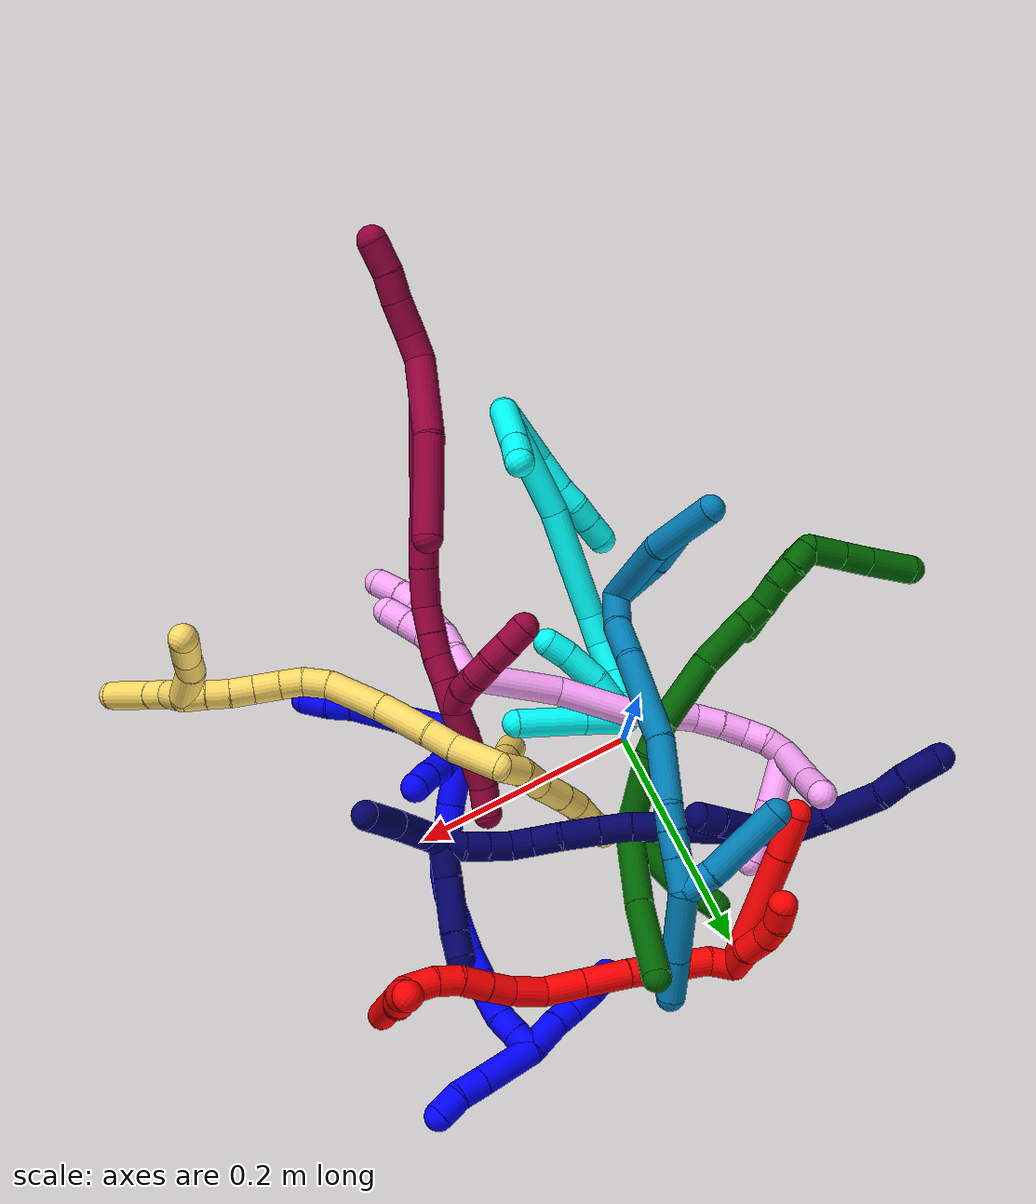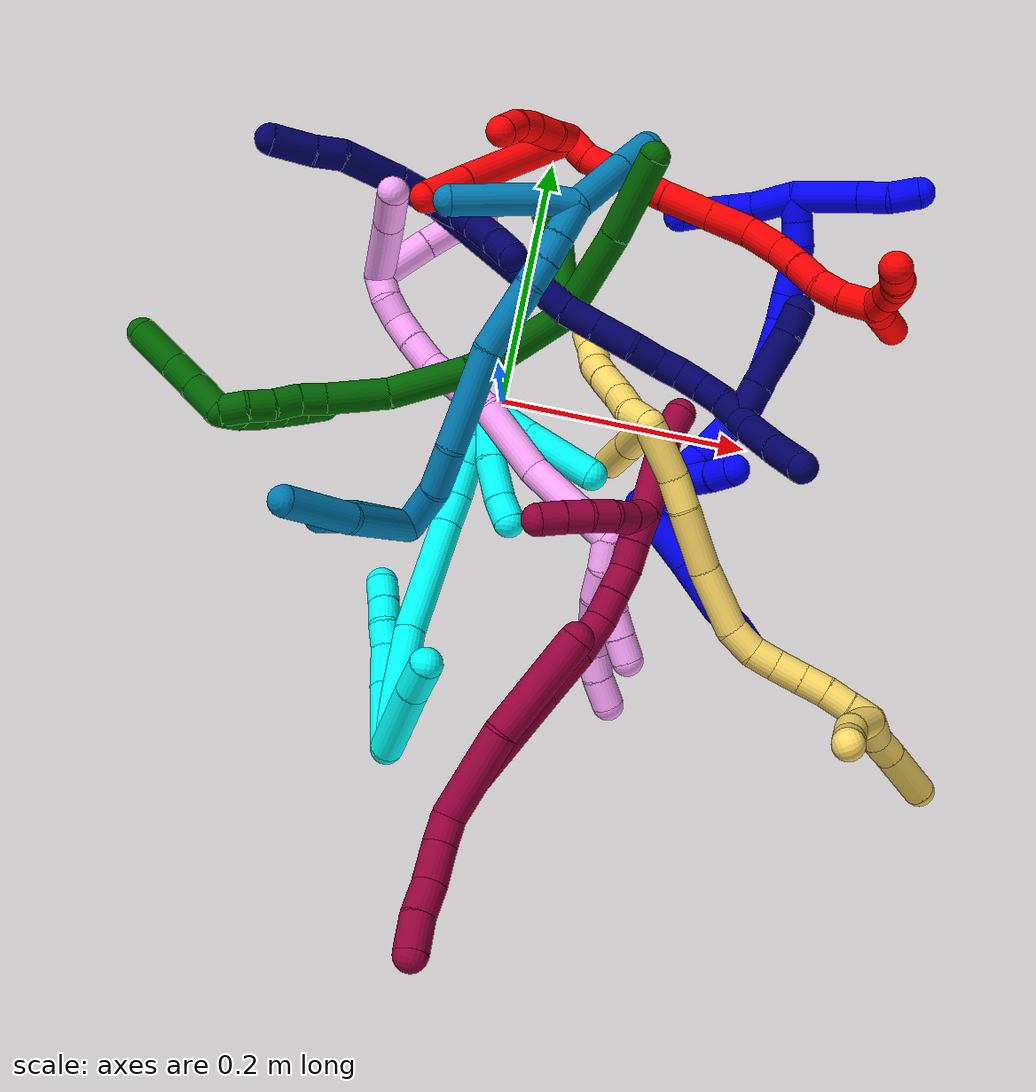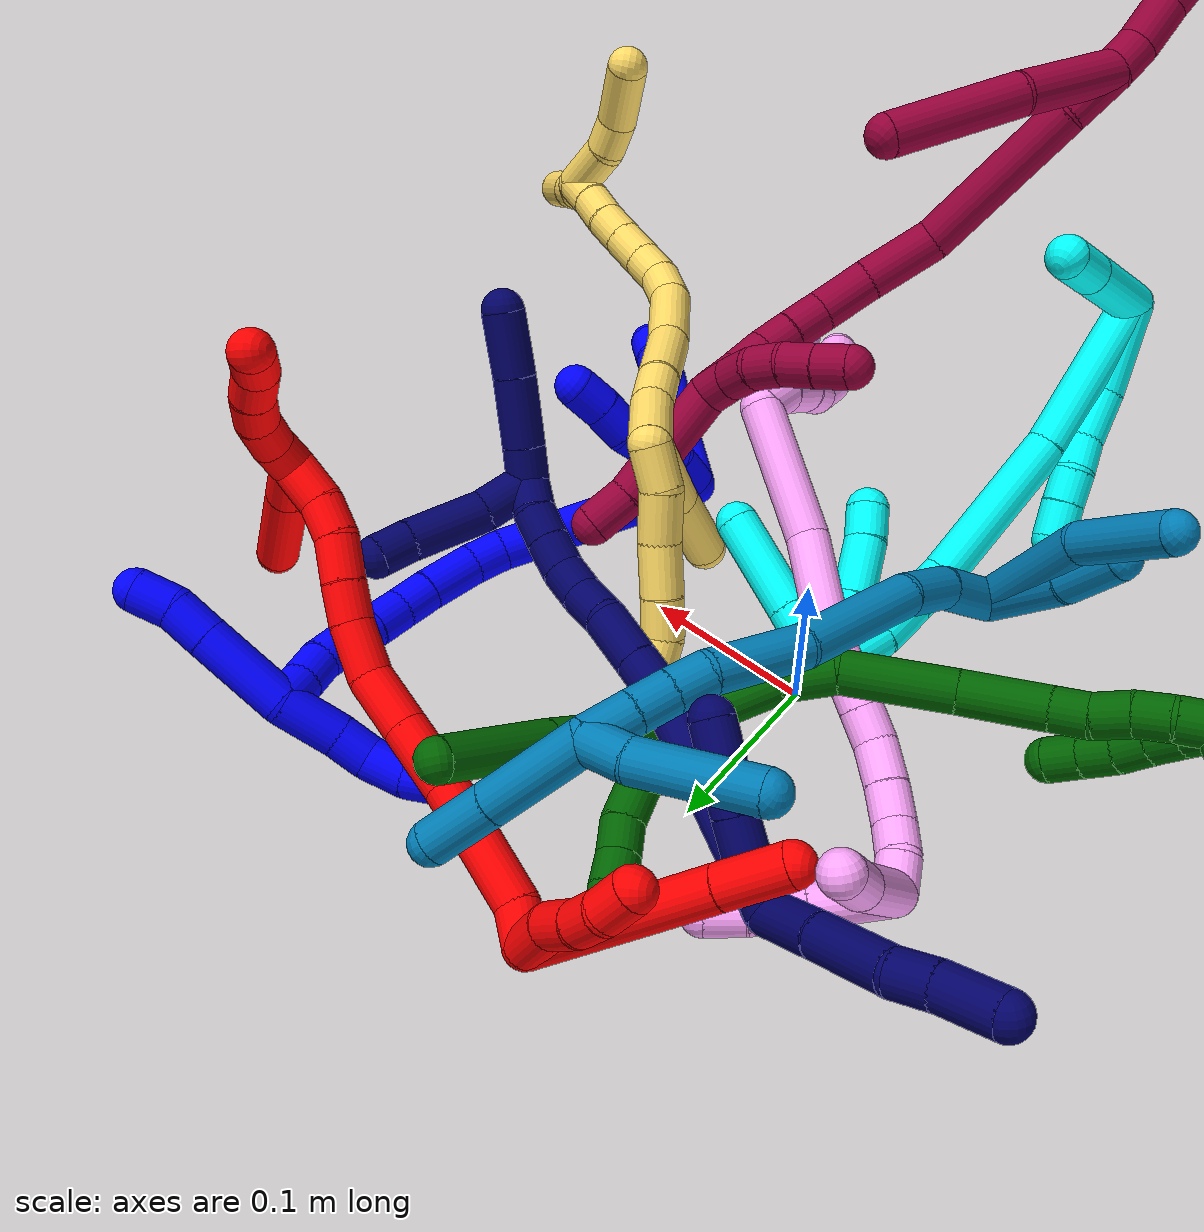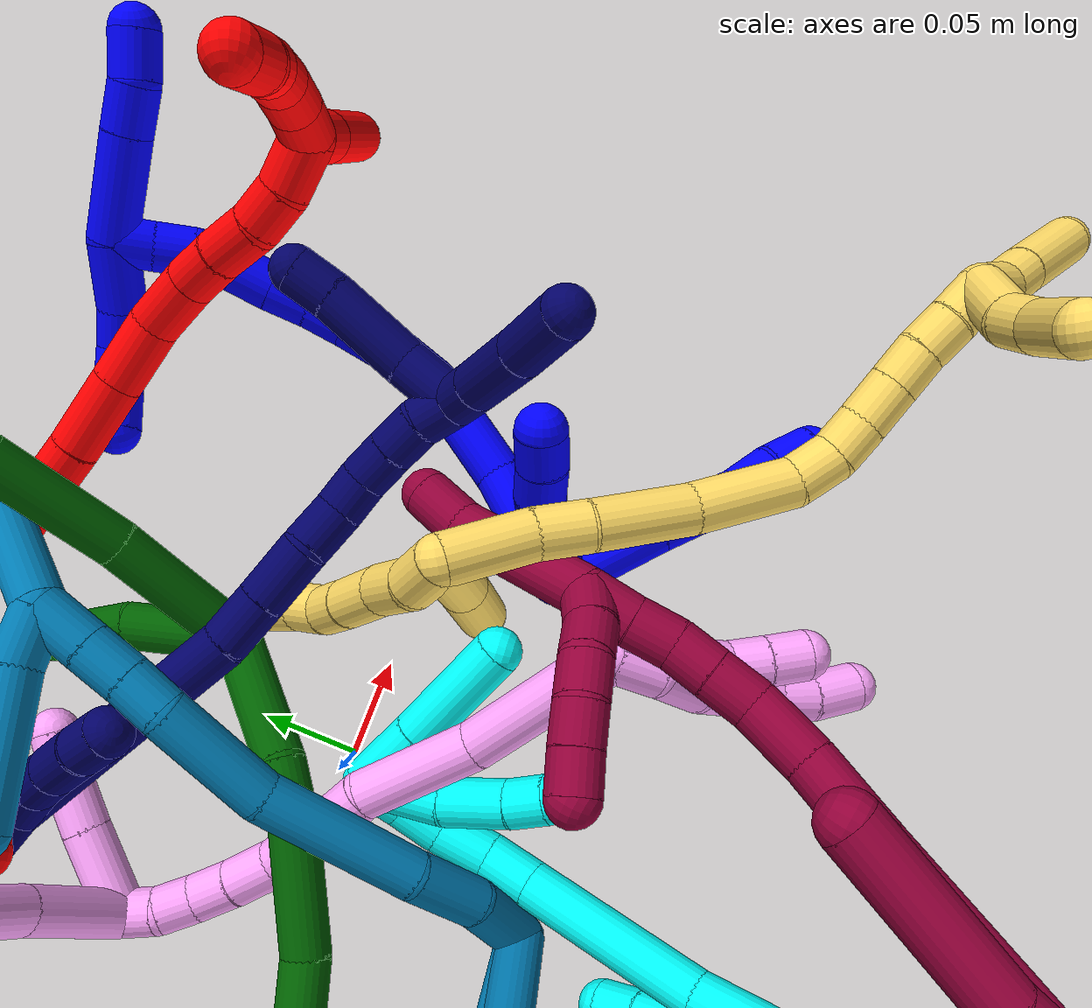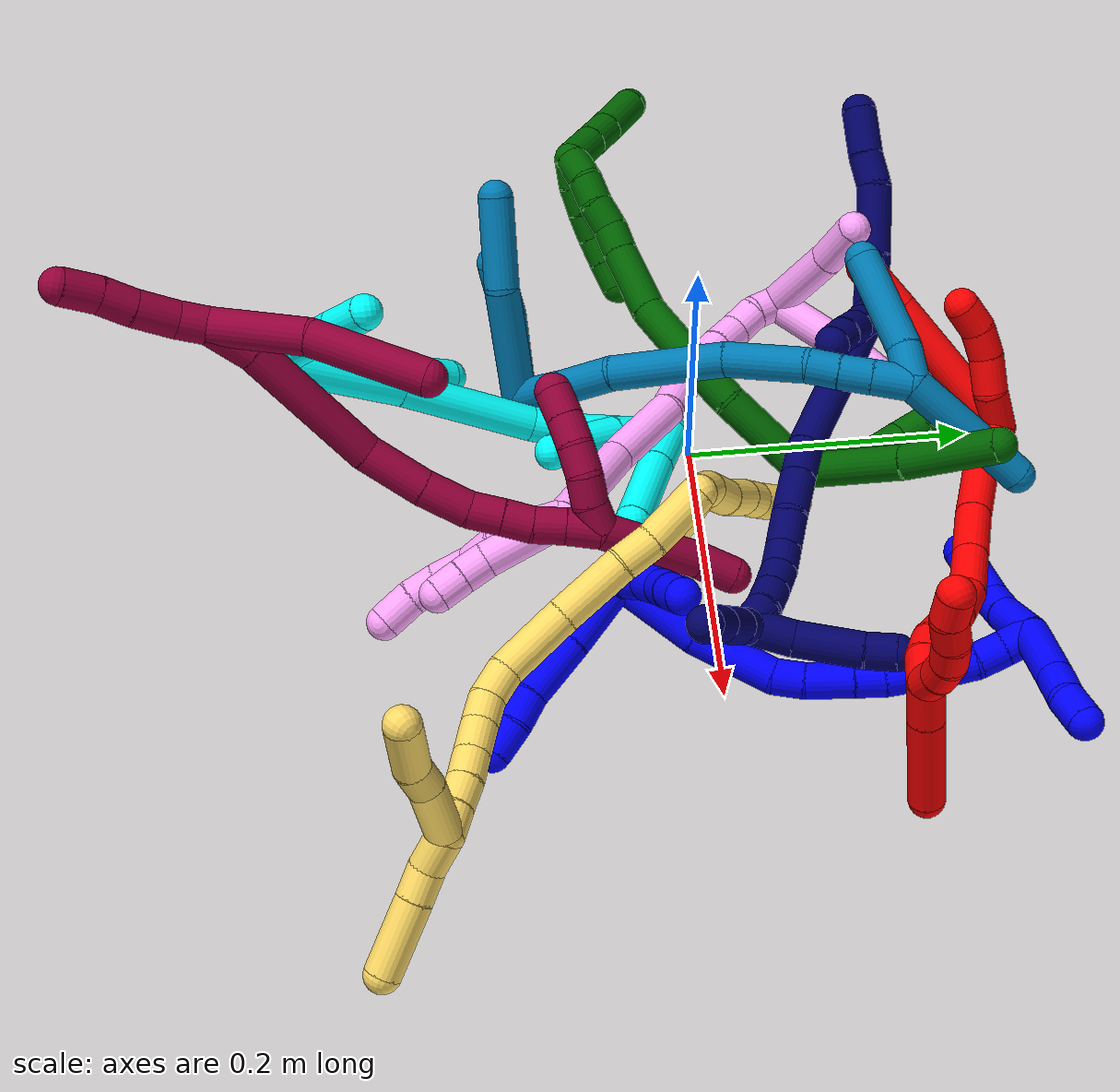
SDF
<sdf version="1.7">
 <world name="default">
  <plugin name="TubeGeneratorPlugin" filename="libtube_generator_plugin.so"/>
  <model name="photoneo_s_sensor">
   <static>1</static>
   <pose>0 0 2 1.57079 1.57079 3.14159</pose>
   <link name="link">
    <inertial><mass>0.1</mass></inertial>
    <sensor name="sensor" type="depth">
     <update_rate>30</update_rate>
     <camera>
      <horizontal_fov>1.22</horizontal_fov>
      <image><width>1920</width><height>1200</height><format>B8G8R8</format></image>
      <clip><near>0.1</near><far>4</far></clip>
      <depth_camera><output>points</output></depth_camera>
     </camera>
     <plugin name="camera_plugin" filename="libgazebo_ros_depth_camera.so">
      <baseline>0.2</baseline>
      <alwaysOn>1</alwaysOn>
      <updateRate>0.0</updateRate>
      <cameraName>camera_ir</cameraName>
      <imageTopicName>/camera/color/image_raw</imageTopicName>
      <cameraInfoTopicName>/camera/color/camera_info</cameraInfoTopicName>
      <depthImageTopicName>/camera/depth/image_raw</depthImageTopicName>
      <depthImageCameraInfoTopicName>/camera/depth/camera_info</depthImageCameraInfoTopicName>
      <pointCloudTopicName>/camera/depth/points</pointCloudTopicName>
      <frameName>fr_optical</frameName>
      <pointCloudCutoff>0.1</pointCloudCutoff>
      <pointCloudCutoffMax>2.0</pointCloudCutoffMax>
      <distortionK1>0</distortionK1>
      <distortionK2>0</distortionK2>
      <distortionK3>0</distortionK3>
      <distortionT1>0</distortionT1>
      <distortionT2>0</distortionT2>
      <CxPrime>0</CxPrime>
      <Cx>0</Cx>
      <Cy>0</Cy>
      <focalLength>0</focalLength>
      <hackBaseline>0</hackBaseline>
     </plugin>
    </sensor>
   </link>
  </model>
  <gravity>0 0 -9.8</gravity>
  <magnetic_field>6e-06 2.3e-05 -4.2e-05</magnetic_field>
  <atmosphere type="adiabatic"/>
  <physics name="default_physics" default="0" type="ode">
   <max_step_size>0.003</max_step_size>
   <real_time_factor>1</real_time_factor>
   <real_time_update_rate>1000</real_time_update_rate>
   <max_contacts>10000</max_contacts>
   <ode>
    <solver>
     <type>quick</type>
     <iters>100</iters>
     <sor>1.3</sor>
     <use_dynamic_moi_rescaling>0</use_dynamic_moi_rescaling>
    </solver>
    <constraints>
     <contact_max_correcting_vel>0</contact_max_correcting_vel>
     <contact_surface_layer>0.001</contact_surface_layer>
     <cfm>0</cfm>
     <erp>0.2</erp>
    </constraints>
   </ode>
  </physics>
  <scene><ambient>0.4 0.4 0.4 1</ambient><background>0.7 0.7 0.7 1</background><shadows>0</shadows></scene>
  <audio><device>default</device></audio>
  <spherical_coordinates>
   <surface_model>EARTH_WGS84</surface_model>
   <latitude_deg>0</latitude_deg>
   <longitude_deg>0</longitude_deg>
   <elevation>0</elevation>
   <heading_deg>0</heading_deg>
  </spherical_coordinates>
  <model name="bin">
   <static>1</static>
   <link name="bottom">
    <collision name="collision-bottom">
     <pose>0 0 -0.01 0 -0 0</pose>
     <geometry><box><size>0.8 0.6 0.02</size></box></geometry>
     <surface>
      <friction><ode><mu>100</mu><mu2>100</mu2></ode></friction>
      <contact><collide_bitmask>65535</collide_bitmask></contact>
     </surface>
    </collision>
   </link>
   <link name="west_wall">
    <collision name="collision-west_wall">
     <pose>-0.41 0 0.1 0 -0 0</pose>
     <geometry><box><size>0.02 0.6 0.2</size></box></geometry>
     <surface>
      <friction><ode><mu>100</mu><mu2>100</mu2></ode></friction>
      <contact><collide_bitmask>65535</collide_bitmask></contact>
     </surface>
    </collision>
   </link>
   <link name="east_wall">
    <collision name="collision-east_wall">
     <pose>0.41 0 0.1 0 -0 0</pose>
     <geometry><box><size>0.02 0.6 0.2</size></box></geometry>
     <surface>
      <friction><ode><mu>100</mu><mu2>100</mu2></ode></friction>
      <contact><collide_bitmask>65535</collide_bitmask></contact>
     </surface>
    </collision>
   </link>
   <link name="south_wall">
    <collision name="collision-south_wall">
     <pose>0 -0.31 0.1 0 -0 0</pose>
     <geometry><box><size>0.8 0.02 0.2</size></box></geometry>
     <surface>
      <friction><ode><mu>100</mu><mu2>100</mu2></ode></friction>
      <contact><collide_bitmask>65535</collide_bitmask></contact>
     </surface>
    </collision>
   </link>
   <link name="north_wall">
    <collision name="collision-north_wall">
     <pose>0 0.31 0.1 0 -0 0</pose>
     <geometry><box><size>0.8 0.02 0.2</size></box></geometry>
     <surface>
      <friction><ode><mu>100</mu><mu2>100</mu2></ode></friction>
      <contact><collide_bitmask>65535</collide_bitmask></contact>
     </surface>
    </collision>
   </link>
  </model>
  <model name="1">
   <static>0</static>
   <link name="1">
    <collision name="collision-cylinder-e_1_2_8">
     <pose>0.016412 -0.02162 0.009322 1.16372 0.608759 0.407567</pose>
     <geometry><cylinder><radius>0.0125</radius><length>0.057399</length></cylinder></geometry>
     <surface>
      <friction><ode><mu>1.16</mu><mu2>1.16</mu2><slip1>0</slip1><slip2>0</slip2></ode></friction>
      <contact><ode><kp>1e+06</kp><kd>1</kd><max_vel>0</max_vel><min_depth>0.001</min_depth></ode></contact>
     </surface>
    </collision>
    <visual name="visual-cylinder-e_1_2_8">
     <pose>0.016412 -0.02162 0.009322 1.16372 0.608759 0.407567</pose>
     <geometry><cylinder><radius>0.0125</radius><length>0.057399</length></cylinder></geometry>
     <material><ambient>0 0 1 1</ambient></material>
    </visual>
    <collision name="collision-cylinder-e_2_8_9">
     <pose>0.04574 -0.060776 0.025019 1.22207 0.605502 0.430795</pose>
     <geometry><cylinder><radius>0.0125</radius><length>0.045388</length></cylinder></geometry>
     <surface>
      <friction><ode><mu>1.16</mu><mu2>1.16</mu2><slip1>0</slip1><slip2>0</slip2></ode></friction>
      <contact><ode><kp>1e+06</kp><kd>1</kd><max_vel>0</max_vel><min_depth>0.001</min_depth></ode></contact>
     </surface>
    </collision>
    <visual name="visual-cylinder-e_2_8_9">
     <pose>0.04574 -0.060776 0.025019 1.22207 0.605502 0.430795</pose>
     <geometry><cylinder><radius>0.0125</radius><length>0.045388</length></cylinder></geometry>
     <material><ambient>0 0 1 1</ambient></material>
    </visual>
    <collision name="collision-cylinder-e_3_9_10">
     <pose>0.066463 -0.085505 0.0351 1.09515 0.767503 0.482811</pose>
     <geometry><cylinder><radius>0.0125</radius><length>0.022486</length></cylinder></geometry>
     <surface>
      <friction><ode><mu>1.16</mu><mu2>1.16</mu2><slip1>0</slip1><slip2>0</slip2></ode></friction>
      <contact><ode><kp>1e+06</kp><kd>1</kd><max_vel>0</max_vel><min_depth>0.001</min_depth></ode></contact>
     </surface>
    </collision>
    <visual name="visual-cylinder-e_3_9_10">
     <pose>0.066463 -0.085505 0.0351 1.09515 0.767503 0.482811</pose>
     <geometry><cylinder><radius>0.0125</radius><length>0.022486</length></cylinder></geometry>
     <material><ambient>0 0 1 1</ambient></material>
    </visual>
    <collision name="collision-cylinder-e_4_10_6">
     <pose>0.082904 -0.101327 0.040768 1.34711 0.773065 0.628127</pose>
     <geometry><cylinder><radius>0.0125</radius><length>0.024728</length></cylinder></geometry>
     <surface>
      <friction><ode><mu>1.16</mu><mu2>1.16</mu2><slip1>0</slip1><slip2>0</slip2></ode></friction>
      <contact><ode><kp>1e+06</kp><kd>1</kd><max_vel>0</max_vel><min_depth>0.001</min_depth></ode></contact>
     </surface>
    </collision>
    <visual name="visual-cylinder-e_4_10_6">
     <pose>0.082904 -0.101327 0.040768 1.34711 0.773065 0.628127</pose>
     <geometry><cylinder><radius>0.0125</radius><length>0.024728</length></cylinder></geometry>
     <material><ambient>0 0 1 1</ambient></material>
    </visual>
    <collision name="collision-cylinder-e_1_2_11">
     <pose>-0.002845 -0.000403 0.009578 0.042101 -0.288525 -0.006117</pose>
     <geometry><cylinder><radius>0.0125</radius><length>0.02</length></cylinder></geometry>
     <surface>
      <friction><ode><mu>1.16</mu><mu2>1.16</mu2><slip1>0</slip1><slip2>0</slip2></ode></friction>
      <contact><ode><kp>1e+06</kp><kd>1</kd><max_vel>0</max_vel><min_depth>0.001</min_depth></ode></contact>
     </surface>
    </collision>
    <visual name="visual-cylinder-e_1_2_11">
     <pose>-0.002845 -0.000403 0.009578 0.042101 -0.288525 -0.006117</pose>
     <geometry><cylinder><radius>0.0125</radius><length>0.02</length></cylinder></geometry>
     <material><ambient>0 0 1 1</ambient></material>
    </visual>
    <collision name="collision-cylinder-e_2_11_12">
     <pose>-0.007285 0.001848 0.028665 -0.272276 -0.16007 0.021973</pose>
     <geometry><cylinder><radius>0.0125</radius><length>0.02</length></cylinder></geometry>
     <surface>
      <friction><ode><mu>1.16</mu><mu2>1.16</mu2><slip1>0</slip1><slip2>0</slip2></ode></friction>
      <contact><ode><kp>1e+06</kp><kd>1</kd><max_vel>0</max_vel><min_depth>0.001</min_depth></ode></contact>
     </surface>
    </collision>
    <visual name="visual-cylinder-e_2_11_12">
     <pose>-0.007285 0.001848 0.028665 -0.272276 -0.16007 0.021973</pose>
     <geometry><cylinder><radius>0.0125</radius><length>0.02</length></cylinder></geometry>
     <material><ambient>0 0 1 1</ambient></material>
    </visual>
    <collision name="collision-cylinder-e_3_12_13">
     <pose>-0.00951 0.006184 0.048011 -0.169308 -0.063163 0.005362</pose>
     <geometry><cylinder><radius>0.0125</radius><length>0.02</length></cylinder></geometry>
     <surface>
      <friction><ode><mu>1.16</mu><mu2>1.16</mu2><slip1>0</slip1><slip2>0</slip2></ode></friction>
      <contact><ode><kp>1e+06</kp><kd>1</kd><max_vel>0</max_vel><min_depth>0.001</min_depth></ode></contact>
     </surface>
    </collision>
    <visual name="visual-cylinder-e_3_12_13">
     <pose>-0.00951 0.006184 0.048011 -0.169308 -0.063163 0.005362</pose>
     <geometry><cylinder><radius>0.0125</radius><length>0.02</length></cylinder></geometry>
     <material><ambient>0 0 1 1</ambient></material>
    </visual>
    <collision name="collision-cylinder-e_4_13_14">
     <pose>-0.011485 0.007234 0.067737 0.063818 -0.134791 -0.004309</pose>
     <geometry><cylinder><radius>0.0125</radius><length>0.02</length></cylinder></geometry>
     <surface>
      <friction><ode><mu>1.16</mu><mu2>1.16</mu2><slip1>0</slip1><slip2>0</slip2></ode></friction>
      <contact><ode><kp>1e+06</kp><kd>1</kd><max_vel>0</max_vel><min_depth>0.001</min_depth></ode></contact>
     </surface>
    </collision>
    <visual name="visual-cylinder-e_4_13_14">
     <pose>-0.011485 0.007234 0.067737 0.063818 -0.134791 -0.004309</pose>
     <geometry><cylinder><radius>0.0125</radius><length>0.02</length></cylinder></geometry>
     <material><ambient>0 0 1 1</ambient></material>
    </visual>
    <collision name="collision-cylinder-e_5_14_5">
     <pose>-0.013739 0.007001 0.087577 -0.040034 -0.091123 0.001826</pose>
     <geometry><cylinder><radius>0.0125</radius><length>0.02</length></cylinder></geometry>
     <surface>
      <friction><ode><mu>1.16</mu><mu2>1.16</mu2><slip1>0</slip1><slip2>0</slip2></ode></friction>
      <contact><ode><kp>1e+06</kp><kd>1</kd><max_vel>0</max_vel><min_depth>0.001</min_depth></ode></contact>
     </surface>
    </collision>
    <visual name="visual-cylinder-e_5_14_5">
     <pose>-0.013739 0.007001 0.087577 -0.040034 -0.091123 0.001826</pose>
     <geometry><cylinder><radius>0.0125</radius><length>0.02</length></cylinder></geometry>
     <material><ambient>0 0 1 1</ambient></material>
    </visual>
    <collision name="collision-cylinder-e_1_2_15">
     <pose>0.018682 0.020752 0.015413 -0.931985 0.625825 -0.322613</pose>
     <geometry><cylinder><radius>0.0125</radius><length>0.063788</length></cylinder></geometry>
     <surface>
      <friction><ode><mu>1.16</mu><mu2>1.16</mu2><slip1>0</slip1><slip2>0</slip2></ode></friction>
      <contact><ode><kp>1e+06</kp><kd>1</kd><max_vel>0</max_vel><min_depth>0.001</min_depth></ode></contact>
     </surface>
    </collision>
    <visual name="visual-cylinder-e_1_2_15">
     <pose>0.018682 0.020752 0.015413 -0.931985 0.625825 -0.322613</pose>
     <geometry><cylinder><radius>0.0125</radius><length>0.063788</length></cylinder></geometry>
     <material><ambient>0 0 1 1</ambient></material>
    </visual>
    <collision name="collision-cylinder-e_2_15_16">
     <pose>0.050063 0.062688 0.046645 -0.929354 0.447755 -0.227297</pose>
     <geometry><cylinder><radius>0.0125</radius><length>0.058662</length></cylinder></geometry>
     <surface>
      <friction><ode><mu>1.16</mu><mu2>1.16</mu2><slip1>0</slip1><slip2>0</slip2></ode></friction>
      <contact><ode><kp>1e+06</kp><kd>1</kd><max_vel>0</max_vel><min_depth>0.001</min_depth></ode></contact>
     </surface>
    </collision>
    <visual name="visual-cylinder-e_2_15_16">
     <pose>0.050063 0.062688 0.046645 -0.929354 0.447755 -0.227297</pose>
     <geometry><cylinder><radius>0.0125</radius><length>0.058662</length></cylinder></geometry>
     <material><ambient>0 0 1 1</ambient></material>
    </visual>
    <collision name="collision-cylinder-e_3_16_17">
     <pose>0.064281 0.093185 0.067785 -1.0518 0.140708 -0.08176</pose>
     <geometry><cylinder><radius>0.0125</radius><length>0.021663</length></cylinder></geometry>
     <surface>
      <friction><ode><mu>1.16</mu><mu2>1.16</mu2><slip1>0</slip1><slip2>0</slip2></ode></friction>
      <contact><ode><kp>1e+06</kp><kd>1</kd><max_vel>0</max_vel><min_depth>0.001</min_depth></ode></contact>
     </surface>
    </collision>
    <visual name="visual-cylinder-e_3_16_17">
     <pose>0.064281 0.093185 0.067785 -1.0518 0.140708 -0.08176</pose>
     <geometry><cylinder><radius>0.0125</radius><length>0.021663</length></cylinder></geometry>
     <material><ambient>0 0 1 1</ambient></material>
    </visual>
    <collision name="collision-cylinder-e_4_17_18">
     <pose>0.065601 0.117462 0.080258 -1.12486 -0.012003 0.007566</pose>
     <geometry><cylinder><radius>0.0125</radius><length>0.033175</length></cylinder></geometry>
     <surface>
      <friction><ode><mu>1.16</mu><mu2>1.16</mu2><slip1>0</slip1><slip2>0</slip2></ode></friction>
      <contact><ode><kp>1e+06</kp><kd>1</kd><max_vel>0</max_vel><min_depth>0.001</min_depth></ode></contact>
     </surface>
    </collision>
    <visual name="visual-cylinder-e_4_17_18">
     <pose>0.065601 0.117462 0.080258 -1.12486 -0.012003 0.007566</pose>
     <geometry><cylinder><radius>0.0125</radius><length>0.033175</length></cylinder></geometry>
     <material><ambient>0 0 1 1</ambient></material>
    </visual>
    <collision name="collision-cylinder-e_5_18_19">
     <pose>0.065372 0.142043 0.091404 -1.1773 -0.002821 0.001883</pose>
     <geometry><cylinder><radius>0.0125</radius><length>0.020826</length></cylinder></geometry>
     <surface>
      <friction><ode><mu>1.16</mu><mu2>1.16</mu2><slip1>0</slip1><slip2>0</slip2></ode></friction>
      <contact><ode><kp>1e+06</kp><kd>1</kd><max_vel>0</max_vel><min_depth>0.001</min_depth></ode></contact>
     </surface>
    </collision>
    <visual name="visual-cylinder-e_5_18_19">
     <pose>0.065372 0.142043 0.091404 -1.1773 -0.002821 0.001883</pose>
     <geometry><cylinder><radius>0.0125</radius><length>0.020826</length></cylinder></geometry>
     <material><ambient>0 0 1 1</ambient></material>
    </visual>
    <collision name="collision-cylinder-e_6_19_20">
     <pose>0.06359 0.161427 0.099667 -1.15867 -0.162989 0.106766</pose>
     <geometry><cylinder><radius>0.0125</radius><length>0.021606</length></cylinder></geometry>
     <surface>
      <friction><ode><mu>1.16</mu><mu2>1.16</mu2><slip1>0</slip1><slip2>0</slip2></ode></friction>
      <contact><ode><kp>1e+06</kp><kd>1</kd><max_vel>0</max_vel><min_depth>0.001</min_depth></ode></contact>
     </surface>
    </collision>
    <visual name="visual-cylinder-e_6_19_20">
     <pose>0.06359 0.161427 0.099667 -1.15867 -0.162989 0.106766</pose>
     <geometry><cylinder><radius>0.0125</radius><length>0.021606</length></cylinder></geometry>
     <material><ambient>0 0 1 1</ambient></material>
    </visual>
    <collision name="collision-cylinder-e_7_20_21">
     <pose>0.060268 0.180012 0.108525 -1.09098 -0.156553 0.095138</pose>
     <geometry><cylinder><radius>0.0125</radius><length>0.020125</length></cylinder></geometry>
     <surface>
      <friction><ode><mu>1.16</mu><mu2>1.16</mu2><slip1>0</slip1><slip2>0</slip2></ode></friction>
      <contact><ode><kp>1e+06</kp><kd>1</kd><max_vel>0</max_vel><min_depth>0.001</min_depth></ode></contact>
     </surface>
    </collision>
    <visual name="visual-cylinder-e_7_20_21">
     <pose>0.060268 0.180012 0.108525 -1.09098 -0.156553 0.095138</pose>
     <geometry><cylinder><radius>0.0125</radius><length>0.020125</length></cylinder></geometry>
     <material><ambient>0 0 1 1</ambient></material>
    </visual>
    <collision name="collision-cylinder-e_8_21_22">
     <pose>0.05659 0.197919 0.116836 -1.18205 -0.211513 0.142226</pose>
     <geometry><cylinder><radius>0.0125</radius><length>0.020094</length></cylinder></geometry>
     <surface>
      <friction><ode><mu>1.16</mu><mu2>1.16</mu2><slip1>0</slip1><slip2>0</slip2></ode></friction>
      <contact><ode><kp>1e+06</kp><kd>1</kd><max_vel>0</max_vel><min_depth>0.001</min_depth></ode></contact>
     </surface>
    </collision>
    <visual name="visual-cylinder-e_8_21_22">
     <pose>0.05659 0.197919 0.116836 -1.18205 -0.211513 0.142226</pose>
     <geometry><cylinder><radius>0.0125</radius><length>0.020094</length></cylinder></geometry>
     <material><ambient>0 0 1 1</ambient></material>
    </visual>
    <collision name="collision-cylinder-e_9_22_23">
     <pose>0.050852 0.216159 0.122406 -1.37163 -0.370813 0.304593</pose>
     <geometry><cylinder><radius>0.0125</radius><length>0.020029</length></cylinder></geometry>
     <surface>
      <friction><ode><mu>1.16</mu><mu2>1.16</mu2><slip1>0</slip1><slip2>0</slip2></ode></friction>
      <contact><ode><kp>1e+06</kp><kd>1</kd><max_vel>0</max_vel><min_depth>0.001</min_depth></ode></contact>
     </surface>
    </collision>
    <visual name="visual-cylinder-e_9_22_23">
     <pose>0.050852 0.216159 0.122406 -1.37163 -0.370813 0.304593</pose>
     <geometry><cylinder><radius>0.0125</radius><length>0.020029</length></cylinder></geometry>
     <material><ambient>0 0 1 1</ambient></material>
    </visual>
    <collision name="collision-cylinder-e_10_23_1">
     <pose>0.042845 0.233993 0.126646 -1.30195 -0.452333 0.347033</pose>
     <geometry><cylinder><radius>0.0125</radius><length>0.020032</length></cylinder></geometry>
     <surface>
      <friction><ode><mu>1.16</mu><mu2>1.16</mu2><slip1>0</slip1><slip2>0</slip2></ode></friction>
      <contact><ode><kp>1e+06</kp><kd>1</kd><max_vel>0</max_vel><min_depth>0.001</min_depth></ode></contact>
     </surface>
    </collision>
    <visual name="visual-cylinder-e_10_23_1">
     <pose>0.042845 0.233993 0.126646 -1.30195 -0.452333 0.347033</pose>
     <geometry><cylinder><radius>0.0125</radius><length>0.020032</length></cylinder></geometry>
     <material><ambient>0 0 1 1</ambient></material>
    </visual>
    <collision name="collision-cylinder-e_1_1_24">
     <pose>0.045434 0.237891 0.154224 0.187847 0.265343 0.025142</pose>
     <geometry><cylinder><radius>0.0125</radius><length>0.053132</length></cylinder></geometry>
     <surface>
      <friction><ode><mu>1.16</mu><mu2>1.16</mu2><slip1>0</slip1><slip2>0</slip2></ode></friction>
      <contact><ode><kp>1e+06</kp><kd>1</kd><max_vel>0</max_vel><min_depth>0.001</min_depth></ode></contact>
     </surface>
    </collision>
    <visual name="visual-cylinder-e_1_1_24">
     <pose>0.045434 0.237891 0.154224 0.187847 0.265343 0.025142</pose>
     <geometry><cylinder><radius>0.0125</radius><length>0.053132</length></cylinder></geometry>
     <material><ambient>0 0 1 1</ambient></material>
    </visual>
    <collision name="collision-cylinder-e_2_24_25">
     <pose>0.05571 0.230742 0.190642 0.20715 0.280666 0.029365</pose>
     <geometry><cylinder><radius>0.0125</radius><length>0.023892</length></cylinder></geometry>
     <surface>
      <friction><ode><mu>1.16</mu><mu2>1.16</mu2><slip1>0</slip1><slip2>0</slip2></ode></friction>
      <contact><ode><kp>1e+06</kp><kd>1</kd><max_vel>0</max_vel><min_depth>0.001</min_depth></ode></contact>
     </surface>
    </collision>
    <visual name="visual-cylinder-e_2_24_25">
     <pose>0.05571 0.230742 0.190642 0.20715 0.280666 0.029365</pose>
     <geometry><cylinder><radius>0.0125</radius><length>0.023892</length></cylinder></geometry>
     <material><ambient>0 0 1 1</ambient></material>
    </visual>
    <collision name="collision-cylinder-e_3_25_4">
     <pose>0.063764 0.229171 0.212308 -0.07552 0.425783 -0.016332</pose>
     <geometry><cylinder><radius>0.0125</radius><length>0.022977</length></cylinder></geometry>
     <surface>
      <friction><ode><mu>1.16</mu><mu2>1.16</mu2><slip1>0</slip1><slip2>0</slip2></ode></friction>
      <contact><ode><kp>1e+06</kp><kd>1</kd><max_vel>0</max_vel><min_depth>0.001</min_depth></ode></contact>
     </surface>
    </collision>
    <visual name="visual-cylinder-e_3_25_4">
     <pose>0.063764 0.229171 0.212308 -0.07552 0.425783 -0.016332</pose>
     <geometry><cylinder><radius>0.0125</radius><length>0.022977</length></cylinder></geometry>
     <material><ambient>0 0 1 1</ambient></material>
    </visual>
    <collision name="collision-cylinder-e_1_1_26">
     <pose>0.036109 0.24201 0.111768 3.10296 -0.13565 -2.58748</pose>
     <geometry><cylinder><radius>0.0125</radius><length>0.034888</length></cylinder></geometry>
     <surface>
      <friction><ode><mu>1.16</mu><mu2>1.16</mu2><slip1>0</slip1><slip2>0</slip2></ode></friction>
      <contact><ode><kp>1e+06</kp><kd>1</kd><max_vel>0</max_vel><min_depth>0.001</min_depth></ode></contact>
     </surface>
    </collision>
    <visual name="visual-cylinder-e_1_1_26">
     <pose>0.036109 0.24201 0.111768 3.10296 -0.13565 -2.58748</pose>
     <geometry><cylinder><radius>0.0125</radius><length>0.034888</length></cylinder></geometry>
     <material><ambient>0 0 1 1</ambient></material>
    </visual>
    <collision name="collision-cylinder-e_2_26_27">
     <pose>0.031516 0.242135 0.084342 -3.06377 -0.215872 2.45171</pose>
     <geometry><cylinder><radius>0.0125</radius><length>0.020855</length></cylinder></geometry>
     <surface>
      <friction><ode><mu>1.16</mu><mu2>1.16</mu2><slip1>0</slip1><slip2>0</slip2></ode></friction>
      <contact><ode><kp>1e+06</kp><kd>1</kd><max_vel>0</max_vel><min_depth>0.001</min_depth></ode></contact>
     </surface>
    </collision>
    <visual name="visual-cylinder-e_2_26_27">
     <pose>0.031516 0.242135 0.084342 -3.06377 -0.215872 2.45171</pose>
     <geometry><cylinder><radius>0.0125</radius><length>0.020855</length></cylinder></geometry>
     <material><ambient>0 0 1 1</ambient></material>
    </visual>
    <collision name="collision-cylinder-e_3_27_28">
     <pose>0.023443 0.242539 0.063792 3.10431 -0.511513 -2.99923</pose>
     <geometry><cylinder><radius>0.0125</radius><length>0.02386</length></cylinder></geometry>
     <surface>
      <friction><ode><mu>1.16</mu><mu2>1.16</mu2><slip1>0</slip1><slip2>0</slip2></ode></friction>
      <contact><ode><kp>1e+06</kp><kd>1</kd><max_vel>0</max_vel><min_depth>0.001</min_depth></ode></contact>
     </surface>
    </collision>
    <visual name="visual-cylinder-e_3_27_28">
     <pose>0.023443 0.242539 0.063792 3.10431 -0.511513 -2.99923</pose>
     <geometry><cylinder><radius>0.0125</radius><length>0.02386</length></cylinder></geometry>
     <material><ambient>0 0 1 1</ambient></material>
    </visual>
    <collision name="collision-cylinder-e_4_28_3">
     <pose>0.010447 0.240072 0.046433 2.8514 -0.777742 -2.45646</pose>
     <geometry><cylinder><radius>0.0125</radius><length>0.020397</length></cylinder></geometry>
     <surface>
      <friction><ode><mu>1.16</mu><mu2>1.16</mu2><slip1>0</slip1><slip2>0</slip2></ode></friction>
      <contact><ode><kp>1e+06</kp><kd>1</kd><max_vel>0</max_vel><min_depth>0.001</min_depth></ode></contact>
     </surface>
    </collision>
    <visual name="visual-cylinder-e_4_28_3">
     <pose>0.010447 0.240072 0.046433 2.8514 -0.777742 -2.45646</pose>
     <geometry><cylinder><radius>0.0125</radius><length>0.020397</length></cylinder></geometry>
     <material><ambient>0 0 1 1</ambient></material>
    </visual>
    <collision name="collision-sphere-3">
     <pose>0.003291 0.237993 0.039471 0 -0 0</pose>
     <geometry><sphere><radius>0.0125</radius></sphere></geometry>
     <surface>
      <friction><ode><mu>1.16</mu><mu2>1.16</mu2><slip1>0</slip1><slip2>0</slip2></ode></friction>
      <contact><ode><kp>1e+06</kp><kd>1</kd><max_vel>0</max_vel><min_depth>0.001</min_depth></ode></contact>
     </surface>
    </collision>
    <visual name="visual-sphere-3">
     <pose>0.003291 0.237993 0.039471 0 -0 0</pose>
     <geometry><sphere><radius>0.0125</radius></sphere></geometry>
     <material><ambient>0 0 1 1</ambient></material>
    </visual>
    <collision name="collision-sphere-28">
     <pose>0.017603 0.242151 0.053396 0 -0 0</pose>
     <geometry><sphere><radius>0.0125</radius></sphere></geometry>
     <surface>
      <friction><ode><mu>1.16</mu><mu2>1.16</mu2><slip1>0</slip1><slip2>0</slip2></ode></friction>
      <contact><ode><kp>1e+06</kp><kd>1</kd><max_vel>0</max_vel><min_depth>0.001</min_depth></ode></contact>
     </surface>
    </collision>
    <visual name="visual-sphere-28">
     <pose>0.017603 0.242151 0.053396 0 -0 0</pose>
     <geometry><sphere><radius>0.0125</radius></sphere></geometry>
     <material><ambient>0 0 1 1</ambient></material>
    </visual>
    <collision name="collision-sphere-27">
     <pose>0.029282 0.242927 0.074188 0 -0 0</pose>
     <geometry><sphere><radius>0.0125</radius></sphere></geometry>
     <surface>
      <friction><ode><mu>1.16</mu><mu2>1.16</mu2><slip1>0</slip1><slip2>0</slip2></ode></friction>
      <contact><ode><kp>1e+06</kp><kd>1</kd><max_vel>0</max_vel><min_depth>0.001</min_depth></ode></contact>
     </surface>
    </collision>
    <visual name="visual-sphere-27">
     <pose>0.029282 0.242927 0.074188 0 -0 0</pose>
     <geometry><sphere><radius>0.0125</radius></sphere></geometry>
     <material><ambient>0 0 1 1</ambient></material>
    </visual>
    <collision name="collision-sphere-26">
     <pose>0.03375 0.241343 0.094497 0 -0 0</pose>
     <geometry><sphere><radius>0.0125</radius></sphere></geometry>
     <surface>
      <friction><ode><mu>1.16</mu><mu2>1.16</mu2><slip1>0</slip1><slip2>0</slip2></ode></friction>
      <contact><ode><kp>1e+06</kp><kd>1</kd><max_vel>0</max_vel><min_depth>0.001</min_depth></ode></contact>
     </surface>
    </collision>
    <visual name="visual-sphere-26">
     <pose>0.03375 0.241343 0.094497 0 -0 0</pose>
     <geometry><sphere><radius>0.0125</radius></sphere></geometry>
     <material><ambient>0 0 1 1</ambient></material>
    </visual>
    <collision name="collision-sphere-4">
     <pose>0.068509 0.22996 0.222741 0 -0 0</pose>
     <geometry><sphere><radius>0.0125</radius></sphere></geometry>
     <surface>
      <friction><ode><mu>1.16</mu><mu2>1.16</mu2><slip1>0</slip1><slip2>0</slip2></ode></friction>
      <contact><ode><kp>1e+06</kp><kd>1</kd><max_vel>0</max_vel><min_depth>0.001</min_depth></ode></contact>
     </surface>
    </collision>
    <visual name="visual-sphere-4">
     <pose>0.068509 0.22996 0.222741 0 -0 0</pose>
     <geometry><sphere><radius>0.0125</radius></sphere></geometry>
     <material><ambient>0 0 1 1</ambient></material>
    </visual>
    <collision name="collision-sphere-25">
     <pose>0.059019 0.228382 0.201875 0 -0 0</pose>
     <geometry><sphere><radius>0.0125</radius></sphere></geometry>
     <surface>
      <friction><ode><mu>1.16</mu><mu2>1.16</mu2><slip1>0</slip1><slip2>0</slip2></ode></friction>
      <contact><ode><kp>1e+06</kp><kd>1</kd><max_vel>0</max_vel><min_depth>0.001</min_depth></ode></contact>
     </surface>
    </collision>
    <visual name="visual-sphere-25">
     <pose>0.059019 0.228382 0.201875 0 -0 0</pose>
     <geometry><sphere><radius>0.0125</radius></sphere></geometry>
     <material><ambient>0 0 1 1</ambient></material>
    </visual>
    <collision name="collision-sphere-24">
     <pose>0.052401 0.233103 0.179409 0 -0 0</pose>
     <geometry><sphere><radius>0.0125</radius></sphere></geometry>
     <surface>
      <friction><ode><mu>1.16</mu><mu2>1.16</mu2><slip1>0</slip1><slip2>0</slip2></ode></friction>
      <contact><ode><kp>1e+06</kp><kd>1</kd><max_vel>0</max_vel><min_depth>0.001</min_depth></ode></contact>
     </surface>
    </collision>
    <visual name="visual-sphere-24">
     <pose>0.052401 0.233103 0.179409 0 -0 0</pose>
     <geometry><sphere><radius>0.0125</radius></sphere></geometry>
     <material><ambient>0 0 1 1</ambient></material>
    </visual>
    <collision name="collision-sphere-1">
     <pose>0.038468 0.242678 0.129039 0 -0 0</pose>
     <geometry><sphere><radius>0.0125</radius></sphere></geometry>
     <surface>
      <friction><ode><mu>1.16</mu><mu2>1.16</mu2><slip1>0</slip1><slip2>0</slip2></ode></friction>
      <contact><ode><kp>1e+06</kp><kd>1</kd><max_vel>0</max_vel><min_depth>0.001</min_depth></ode></contact>
     </surface>
    </collision>
    <visual name="visual-sphere-1">
     <pose>0.038468 0.242678 0.129039 0 -0 0</pose>
     <geometry><sphere><radius>0.0125</radius></sphere></geometry>
     <material><ambient>0 0 1 1</ambient></material>
    </visual>
    <collision name="collision-sphere-23">
     <pose>0.047223 0.225308 0.124253 0 -0 0</pose>
     <geometry><sphere><radius>0.0125</radius></sphere></geometry>
     <surface>
      <friction><ode><mu>1.16</mu><mu2>1.16</mu2><slip1>0</slip1><slip2>0</slip2></ode></friction>
      <contact><ode><kp>1e+06</kp><kd>1</kd><max_vel>0</max_vel><min_depth>0.001</min_depth></ode></contact>
     </surface>
    </collision>
    <visual name="visual-sphere-23">
     <pose>0.047223 0.225308 0.124253 0 -0 0</pose>
     <geometry><sphere><radius>0.0125</radius></sphere></geometry>
     <material><ambient>0 0 1 1</ambient></material>
    </visual>
    <collision name="collision-sphere-22">
     <pose>0.054481 0.207009 0.120559 0 -0 0</pose>
     <geometry><sphere><radius>0.0125</radius></sphere></geometry>
     <surface>
      <friction><ode><mu>1.16</mu><mu2>1.16</mu2><slip1>0</slip1><slip2>0</slip2></ode></friction>
      <contact><ode><kp>1e+06</kp><kd>1</kd><max_vel>0</max_vel><min_depth>0.001</min_depth></ode></contact>
     </surface>
    </collision>
    <visual name="visual-sphere-22">
     <pose>0.054481 0.207009 0.120559 0 -0 0</pose>
     <geometry><sphere><radius>0.0125</radius></sphere></geometry>
     <material><ambient>0 0 1 1</ambient></material>
    </visual>
    <collision name="collision-sphere-21">
     <pose>0.058699 0.188829 0.113113 0 -0 0</pose>
     <geometry><sphere><radius>0.0125</radius></sphere></geometry>
     <surface>
      <friction><ode><mu>1.16</mu><mu2>1.16</mu2><slip1>0</slip1><slip2>0</slip2></ode></friction>
      <contact><ode><kp>1e+06</kp><kd>1</kd><max_vel>0</max_vel><min_depth>0.001</min_depth></ode></contact>
     </surface>
    </collision>
    <visual name="visual-sphere-21">
     <pose>0.058699 0.188829 0.113113 0 -0 0</pose>
     <geometry><sphere><radius>0.0125</radius></sphere></geometry>
     <material><ambient>0 0 1 1</ambient></material>
    </visual>
    <collision name="collision-sphere-11">
     <pose>-0.005691 -0.000807 0.019156 0 -0 0</pose>
     <geometry><sphere><radius>0.0125</radius></sphere></geometry>
     <surface>
      <friction><ode><mu>1.16</mu><mu2>1.16</mu2><slip1>0</slip1><slip2>0</slip2></ode></friction>
      <contact><ode><kp>1e+06</kp><kd>1</kd><max_vel>0</max_vel><min_depth>0.001</min_depth></ode></contact>
     </surface>
    </collision>
    <visual name="visual-sphere-11">
     <pose>-0.005691 -0.000807 0.019156 0 -0 0</pose>
     <geometry><sphere><radius>0.0125</radius></sphere></geometry>
     <material><ambient>0 0 1 1</ambient></material>
    </visual>
    <collision name="collision-sphere-6">
     <pose>0.091538 -0.109956 0.042731 0 -0 0</pose>
     <geometry><sphere><radius>0.0125</radius></sphere></geometry>
     <surface>
      <friction><ode><mu>1.16</mu><mu2>1.16</mu2><slip1>0</slip1><slip2>0</slip2></ode></friction>
      <contact><ode><kp>1e+06</kp><kd>1</kd><max_vel>0</max_vel><min_depth>0.001</min_depth></ode></contact>
     </surface>
    </collision>
    <visual name="visual-sphere-6">
     <pose>0.091538 -0.109956 0.042731 0 -0 0</pose>
     <geometry><sphere><radius>0.0125</radius></sphere></geometry>
     <material><ambient>0 0 1 1</ambient></material>
    </visual>
    <collision name="collision-sphere-10">
     <pose>0.07427 -0.092697 0.038805 0 -0 0</pose>
     <geometry><sphere><radius>0.0125</radius></sphere></geometry>
     <surface>
      <friction><ode><mu>1.16</mu><mu2>1.16</mu2><slip1>0</slip1><slip2>0</slip2></ode></friction>
      <contact><ode><kp>1e+06</kp><kd>1</kd><max_vel>0</max_vel><min_depth>0.001</min_depth></ode></contact>
     </surface>
    </collision>
    <visual name="visual-sphere-10">
     <pose>0.07427 -0.092697 0.038805 0 -0 0</pose>
     <geometry><sphere><radius>0.0125</radius></sphere></geometry>
     <material><ambient>0 0 1 1</ambient></material>
    </visual>
    <collision name="collision-sphere-9">
     <pose>0.058657 -0.078312 0.031395 0 -0 0</pose>
     <geometry><sphere><radius>0.0125</radius></sphere></geometry>
     <surface>
      <friction><ode><mu>1.16</mu><mu2>1.16</mu2><slip1>0</slip1><slip2>0</slip2></ode></friction>
      <contact><ode><kp>1e+06</kp><kd>1</kd><max_vel>0</max_vel><min_depth>0.001</min_depth></ode></contact>
     </surface>
    </collision>
    <visual name="visual-sphere-9">
     <pose>0.058657 -0.078312 0.031395 0 -0 0</pose>
     <geometry><sphere><radius>0.0125</radius></sphere></geometry>
     <material><ambient>0 0 1 1</ambient></material>
    </visual>
    <collision name="collision-sphere-2">
     <geometry><sphere><radius>0.0125</radius></sphere></geometry>
     <surface>
      <friction><ode><mu>1.16</mu><mu2>1.16</mu2><slip1>0</slip1><slip2>0</slip2></ode></friction>
      <contact><ode><kp>1e+06</kp><kd>1</kd><max_vel>0</max_vel><min_depth>0.001</min_depth></ode></contact>
     </surface>
    </collision>
    <visual name="visual-sphere-2">
     <geometry><sphere><radius>0.0125</radius></sphere></geometry>
     <material><ambient>0 0 1 1</ambient></material>
    </visual>
    <collision name="collision-sphere-19">
     <pose>0.065343 0.15166 0.095397 0 -0 0</pose>
     <geometry><sphere><radius>0.0125</radius></sphere></geometry>
     <surface>
      <friction><ode><mu>1.16</mu><mu2>1.16</mu2><slip1>0</slip1><slip2>0</slip2></ode></friction>
      <contact><ode><kp>1e+06</kp><kd>1</kd><max_vel>0</max_vel><min_depth>0.001</min_depth></ode></contact>
     </surface>
    </collision>
    <visual name="visual-sphere-19">
     <pose>0.065343 0.15166 0.095397 0 -0 0</pose>
     <geometry><sphere><radius>0.0125</radius></sphere></geometry>
     <material><ambient>0 0 1 1</ambient></material>
    </visual>
    <collision name="collision-sphere-8">
     <pose>0.032823 -0.04324 0.018643 0 -0 0</pose>
     <geometry><sphere><radius>0.0125</radius></sphere></geometry>
     <surface>
      <friction><ode><mu>1.16</mu><mu2>1.16</mu2><slip1>0</slip1><slip2>0</slip2></ode></friction>
      <contact><ode><kp>1e+06</kp><kd>1</kd><max_vel>0</max_vel><min_depth>0.001</min_depth></ode></contact>
     </surface>
    </collision>
    <visual name="visual-sphere-8">
     <pose>0.032823 -0.04324 0.018643 0 -0 0</pose>
     <geometry><sphere><radius>0.0125</radius></sphere></geometry>
     <material><ambient>0 0 1 1</ambient></material>
    </visual>
    <collision name="collision-sphere-12">
     <pose>-0.008879 0.004503 0.038173 0 -0 0</pose>
     <geometry><sphere><radius>0.0125</radius></sphere></geometry>
     <surface>
      <friction><ode><mu>1.16</mu><mu2>1.16</mu2><slip1>0</slip1><slip2>0</slip2></ode></friction>
      <contact><ode><kp>1e+06</kp><kd>1</kd><max_vel>0</max_vel><min_depth>0.001</min_depth></ode></contact>
     </surface>
    </collision>
    <visual name="visual-sphere-12">
     <pose>-0.008879 0.004503 0.038173 0 -0 0</pose>
     <geometry><sphere><radius>0.0125</radius></sphere></geometry>
     <material><ambient>0 0 1 1</ambient></material>
    </visual>
    <collision name="collision-sphere-13">
     <pose>-0.010141 0.007866 0.057848 0 -0 0</pose>
     <geometry><sphere><radius>0.0125</radius></sphere></geometry>
     <surface>
      <friction><ode><mu>1.16</mu><mu2>1.16</mu2><slip1>0</slip1><slip2>0</slip2></ode></friction>
      <contact><ode><kp>1e+06</kp><kd>1</kd><max_vel>0</max_vel><min_depth>0.001</min_depth></ode></contact>
     </surface>
    </collision>
    <visual name="visual-sphere-13">
     <pose>-0.010141 0.007866 0.057848 0 -0 0</pose>
     <geometry><sphere><radius>0.0125</radius></sphere></geometry>
     <material><ambient>0 0 1 1</ambient></material>
    </visual>
    <collision name="collision-sphere-14">
     <pose>-0.012829 0.006602 0.077626 0 -0 0</pose>
     <geometry><sphere><radius>0.0125</radius></sphere></geometry>
     <surface>
      <friction><ode><mu>1.16</mu><mu2>1.16</mu2><slip1>0</slip1><slip2>0</slip2></ode></friction>
      <contact><ode><kp>1e+06</kp><kd>1</kd><max_vel>0</max_vel><min_depth>0.001</min_depth></ode></contact>
     </surface>
    </collision>
    <visual name="visual-sphere-14">
     <pose>-0.012829 0.006602 0.077626 0 -0 0</pose>
     <geometry><sphere><radius>0.0125</radius></sphere></geometry>
     <material><ambient>0 0 1 1</ambient></material>
    </visual>
    <collision name="collision-sphere-5">
     <pose>-0.014649 0.007399 0.097527 0 -0 0</pose>
     <geometry><sphere><radius>0.0125</radius></sphere></geometry>
     <surface>
      <friction><ode><mu>1.16</mu><mu2>1.16</mu2><slip1>0</slip1><slip2>0</slip2></ode></friction>
      <contact><ode><kp>1e+06</kp><kd>1</kd><max_vel>0</max_vel><min_depth>0.001</min_depth></ode></contact>
     </surface>
    </collision>
    <visual name="visual-sphere-5">
     <pose>-0.014649 0.007399 0.097527 0 -0 0</pose>
     <geometry><sphere><radius>0.0125</radius></sphere></geometry>
     <material><ambient>0 0 1 1</ambient></material>
    </visual>
    <collision name="collision-sphere-15">
     <pose>0.037365 0.041504 0.030825 0 -0 0</pose>
     <geometry><sphere><radius>0.0125</radius></sphere></geometry>
     <surface>
      <friction><ode><mu>1.16</mu><mu2>1.16</mu2><slip1>0</slip1><slip2>0</slip2></ode></friction>
      <contact><ode><kp>1e+06</kp><kd>1</kd><max_vel>0</max_vel><min_depth>0.001</min_depth></ode></contact>
     </surface>
    </collision>
    <visual name="visual-sphere-15">
     <pose>0.037365 0.041504 0.030825 0 -0 0</pose>
     <geometry><sphere><radius>0.0125</radius></sphere></geometry>
     <material><ambient>0 0 1 1</ambient></material>
    </visual>
    <collision name="collision-sphere-16">
     <pose>0.062762 0.083872 0.062465 0 -0 0</pose>
     <geometry><sphere><radius>0.0125</radius></sphere></geometry>
     <surface>
      <friction><ode><mu>1.16</mu><mu2>1.16</mu2><slip1>0</slip1><slip2>0</slip2></ode></friction>
      <contact><ode><kp>1e+06</kp><kd>1</kd><max_vel>0</max_vel><min_depth>0.001</min_depth></ode></contact>
     </surface>
    </collision>
    <visual name="visual-sphere-16">
     <pose>0.062762 0.083872 0.062465 0 -0 0</pose>
     <geometry><sphere><radius>0.0125</radius></sphere></geometry>
     <material><ambient>0 0 1 1</ambient></material>
    </visual>
    <collision name="collision-sphere-17">
     <pose>0.0658 0.102497 0.073104 0 -0 0</pose>
     <geometry><sphere><radius>0.0125</radius></sphere></geometry>
     <surface>
      <friction><ode><mu>1.16</mu><mu2>1.16</mu2><slip1>0</slip1><slip2>0</slip2></ode></friction>
      <contact><ode><kp>1e+06</kp><kd>1</kd><max_vel>0</max_vel><min_depth>0.001</min_depth></ode></contact>
     </surface>
    </collision>
    <visual name="visual-sphere-17">
     <pose>0.0658 0.102497 0.073104 0 -0 0</pose>
     <geometry><sphere><radius>0.0125</radius></sphere></geometry>
     <material><ambient>0 0 1 1</ambient></material>
    </visual>
    <collision name="collision-sphere-18">
     <pose>0.065402 0.132426 0.087412 0 -0 0</pose>
     <geometry><sphere><radius>0.0125</radius></sphere></geometry>
     <surface>
      <friction><ode><mu>1.16</mu><mu2>1.16</mu2><slip1>0</slip1><slip2>0</slip2></ode></friction>
      <contact><ode><kp>1e+06</kp><kd>1</kd><max_vel>0</max_vel><min_depth>0.001</min_depth></ode></contact>
     </surface>
    </collision>
    <visual name="visual-sphere-18">
     <pose>0.065402 0.132426 0.087412 0 -0 0</pose>
     <geometry><sphere><radius>0.0125</radius></sphere></geometry>
     <material><ambient>0 0 1 1</ambient></material>
    </visual>
    <collision name="collision-sphere-20">
     <pose>0.061837 0.171195 0.103937 0 -0 0</pose>
     <geometry><sphere><radius>0.0125</radius></sphere></geometry>
     <surface>
      <friction><ode><mu>1.16</mu><mu2>1.16</mu2><slip1>0</slip1><slip2>0</slip2></ode></friction>
      <contact><ode><kp>1e+06</kp><kd>1</kd><max_vel>0</max_vel><min_depth>0.001</min_depth></ode></contact>
     </surface>
    </collision>
    <visual name="visual-sphere-20">
     <pose>0.061837 0.171195 0.103937 0 -0 0</pose>
     <geometry><sphere><radius>0.0125</radius></sphere></geometry>
     <material><ambient>0 0 1 1</ambient></material>
    </visual>
    <inertial>
     <pose>0.037633 0.098111 0.073976 0 -0 0</pose>
     <mass>0.75</mass>
     <inertia><ixx>9.8e-05</ixx><ixy>0</ixy><ixz>0</ixz><iyy>9.8e-05</iyy><iyz>0</iyz><izz>-3.5e-05</izz></inertia>
    </inertial>
   </link>
   <pose>0.125448 -0.06348 0.036158 -0.286843 0.870461 -0.021749</pose>
  </model>
  <model name="2">
   <static>0</static>
   <link name="2">
    <collision name="collision-cylinder-e_1_2_8">
     <pose>0.018017 -0.008734 0.05172 0.167294 0.330856 0.027994</pose>
     <geometry><cylinder><radius>0.0125</radius><length>0.110921</length></cylinder></geometry>
     <surface>
      <friction><ode><mu>1.16</mu><mu2>1.16</mu2><slip1>0</slip1><slip2>0</slip2></ode></friction>
      <contact><ode><kp>1e+06</kp><kd>1</kd><max_vel>0</max_vel><min_depth>0.001</min_depth></ode></contact>
     </surface>
    </collision>
    <visual name="visual-cylinder-e_1_2_8">
     <pose>0.018017 -0.008734 0.05172 0.167294 0.330856 0.027994</pose>
     <geometry><cylinder><radius>0.0125</radius><length>0.110921</length></cylinder></geometry>
     <material><ambient>1 0 0 1</ambient></material>
    </visual>
    <collision name="collision-cylinder-e_2_8_6">
     <pose>0.042008 -0.021023 0.121701 0.192276 0.310742 0.030208</pose>
     <geometry><cylinder><radius>0.0125</radius><length>0.039079</length></cylinder></geometry>
     <surface>
      <friction><ode><mu>1.16</mu><mu2>1.16</mu2><slip1>0</slip1><slip2>0</slip2></ode></friction>
      <contact><ode><kp>1e+06</kp><kd>1</kd><max_vel>0</max_vel><min_depth>0.001</min_depth></ode></contact>
     </surface>
    </collision>
    <visual name="visual-cylinder-e_2_8_6">
     <pose>0.042008 -0.021023 0.121701 0.192276 0.310742 0.030208</pose>
     <geometry><cylinder><radius>0.0125</radius><length>0.039079</length></cylinder></geometry>
     <material><ambient>1 0 0 1</ambient></material>
    </visual>
    <collision name="collision-cylinder-e_1_2_9">
     <pose>0.010315 0.004246 0.010833 -0.373555 0.72531 -0.143167</pose>
     <geometry><cylinder><radius>0.0125</radius><length>0.031099</length></cylinder></geometry>
     <surface>
      <friction><ode><mu>1.16</mu><mu2>1.16</mu2><slip1>0</slip1><slip2>0</slip2></ode></friction>
      <contact><ode><kp>1e+06</kp><kd>1</kd><max_vel>0</max_vel><min_depth>0.001</min_depth></ode></contact>
     </surface>
    </collision>
    <visual name="visual-cylinder-e_1_2_9">
     <pose>0.010315 0.004246 0.010833 -0.373555 0.72531 -0.143167</pose>
     <geometry><cylinder><radius>0.0125</radius><length>0.031099</length></cylinder></geometry>
     <material><ambient>1 0 0 1</ambient></material>
    </visual>
    <collision name="collision-cylinder-e_2_9_10">
     <pose>0.0259 0.013661 0.032702 -0.438004 0.408145 -0.092059</pose>
     <geometry><cylinder><radius>0.0125</radius><length>0.026552</length></cylinder></geometry>
     <surface>
      <friction><ode><mu>1.16</mu><mu2>1.16</mu2><slip1>0</slip1><slip2>0</slip2></ode></friction>
      <contact><ode><kp>1e+06</kp><kd>1</kd><max_vel>0</max_vel><min_depth>0.001</min_depth></ode></contact>
     </surface>
    </collision>
    <visual name="visual-cylinder-e_2_9_10">
     <pose>0.0259 0.013661 0.032702 -0.438004 0.408145 -0.092059</pose>
     <geometry><cylinder><radius>0.0125</radius><length>0.026552</length></cylinder></geometry>
     <material><ambient>1 0 0 1</ambient></material>
    </visual>
    <collision name="collision-cylinder-e_3_10_11">
     <pose>0.036863 0.021074 0.052287 -0.256739 0.572201 -0.075906</pose>
     <geometry><cylinder><radius>0.0125</radius><length>0.02103</length></cylinder></geometry>
     <surface>
      <friction><ode><mu>1.16</mu><mu2>1.16</mu2><slip1>0</slip1><slip2>0</slip2></ode></friction>
      <contact><ode><kp>1e+06</kp><kd>1</kd><max_vel>0</max_vel><min_depth>0.001</min_depth></ode></contact>
     </surface>
    </collision>
    <visual name="visual-cylinder-e_3_10_11">
     <pose>0.036863 0.021074 0.052287 -0.256739 0.572201 -0.075906</pose>
     <geometry><cylinder><radius>0.0125</radius><length>0.02103</length></cylinder></geometry>
     <material><ambient>1 0 0 1</ambient></material>
    </visual>
    <collision name="collision-cylinder-e_4_11_5">
     <pose>0.049098 0.022701 0.069231 0.073496 0.660698 0.025213</pose>
     <geometry><cylinder><radius>0.0125</radius><length>0.021318</length></cylinder></geometry>
     <surface>
      <friction><ode><mu>1.16</mu><mu2>1.16</mu2><slip1>0</slip1><slip2>0</slip2></ode></friction>
      <contact><ode><kp>1e+06</kp><kd>1</kd><max_vel>0</max_vel><min_depth>0.001</min_depth></ode></contact>
     </surface>
    </collision>
    <visual name="visual-cylinder-e_4_11_5">
     <pose>0.049098 0.022701 0.069231 0.073496 0.660698 0.025213</pose>
     <geometry><cylinder><radius>0.0125</radius><length>0.021318</length></cylinder></geometry>
     <material><ambient>1 0 0 1</ambient></material>
    </visual>
    <collision name="collision-cylinder-e_1_2_12">
     <pose>0.007244 -0.007244 -0.004856 2.16137 0.69315 1.19012</pose>
     <geometry><cylinder><radius>0.0125</radius><length>0.022675</length></cylinder></geometry>
     <surface>
      <friction><ode><mu>1.16</mu><mu2>1.16</mu2><slip1>0</slip1><slip2>0</slip2></ode></friction>
      <contact><ode><kp>1e+06</kp><kd>1</kd><max_vel>0</max_vel><min_depth>0.001</min_depth></ode></contact>
     </surface>
    </collision>
    <visual name="visual-cylinder-e_1_2_12">
     <pose>0.007244 -0.007244 -0.004856 2.16137 0.69315 1.19012</pose>
     <geometry><cylinder><radius>0.0125</radius><length>0.022675</length></cylinder></geometry>
     <material><ambient>1 0 0 1</ambient></material>
    </visual>
    <collision name="collision-cylinder-e_2_12_13">
     <pose>0.039592 -0.027978 -0.033158 2.61946 0.748114 1.94642</pose>
     <geometry><cylinder><radius>0.0125</radius><length>0.073807</length></cylinder></geometry>
     <surface>
      <friction><ode><mu>1.16</mu><mu2>1.16</mu2><slip1>0</slip1><slip2>0</slip2></ode></friction>
      <contact><ode><kp>1e+06</kp><kd>1</kd><max_vel>0</max_vel><min_depth>0.001</min_depth></ode></contact>
     </surface>
    </collision>
    <visual name="visual-cylinder-e_2_12_13">
     <pose>0.039592 -0.027978 -0.033158 2.61946 0.748114 1.94642</pose>
     <geometry><cylinder><radius>0.0125</radius><length>0.073807</length></cylinder></geometry>
     <material><ambient>1 0 0 1</ambient></material>
    </visual>
    <collision name="collision-cylinder-e_3_13_14">
     <pose>0.077894 -0.048253 -0.070391 2.68431 0.7096 2.0199</pose>
     <geometry><cylinder><radius>0.0125</radius><length>0.040513</length></cylinder></geometry>
     <surface>
      <friction><ode><mu>1.16</mu><mu2>1.16</mu2><slip1>0</slip1><slip2>0</slip2></ode></friction>
      <contact><ode><kp>1e+06</kp><kd>1</kd><max_vel>0</max_vel><min_depth>0.001</min_depth></ode></contact>
     </surface>
    </collision>
    <visual name="visual-cylinder-e_3_13_14">
     <pose>0.077894 -0.048253 -0.070391 2.68431 0.7096 2.0199</pose>
     <geometry><cylinder><radius>0.0125</radius><length>0.040513</length></cylinder></geometry>
     <material><ambient>1 0 0 1</ambient></material>
    </visual>
    <collision name="collision-cylinder-e_4_14_15">
     <pose>0.102534 -0.060894 -0.096138 2.68623 0.709915 2.02425</pose>
     <geometry><cylinder><radius>0.0125</radius><length>0.035114</length></cylinder></geometry>
     <surface>
      <friction><ode><mu>1.16</mu><mu2>1.16</mu2><slip1>0</slip1><slip2>0</slip2></ode></friction>
      <contact><ode><kp>1e+06</kp><kd>1</kd><max_vel>0</max_vel><min_depth>0.001</min_depth></ode></contact>
     </surface>
    </collision>
    <visual name="visual-cylinder-e_4_14_15">
     <pose>0.102534 -0.060894 -0.096138 2.68623 0.709915 2.02425</pose>
     <geometry><cylinder><radius>0.0125</radius><length>0.035114</length></cylinder></geometry>
     <material><ambient>1 0 0 1</ambient></material>
    </visual>
    <collision name="collision-cylinder-e_5_15_16">
     <pose>0.127281 -0.072143 -0.114382 2.43245 1.01397 1.96573</pose>
     <geometry><cylinder><radius>0.0125</radius><length>0.031342</length></cylinder></geometry>
     <surface>
      <friction><ode><mu>1.16</mu><mu2>1.16</mu2><slip1>0</slip1><slip2>0</slip2></ode></friction>
      <contact><ode><kp>1e+06</kp><kd>1</kd><max_vel>0</max_vel><min_depth>0.001</min_depth></ode></contact>
     </surface>
    </collision>
    <visual name="visual-cylinder-e_5_15_16">
     <pose>0.127281 -0.072143 -0.114382 2.43245 1.01397 1.96573</pose>
     <geometry><cylinder><radius>0.0125</radius><length>0.031342</length></cylinder></geometry>
     <material><ambient>1 0 0 1</ambient></material>
    </visual>
    <collision name="collision-cylinder-e_6_16_17">
     <pose>0.150742 -0.081646 -0.123532 2.17953 1.11255 1.74496</pose>
     <geometry><cylinder><radius>0.0125</radius><length>0.02265</length></cylinder></geometry>
     <surface>
      <friction><ode><mu>1.16</mu><mu2>1.16</mu2><slip1>0</slip1><slip2>0</slip2></ode></friction>
      <contact><ode><kp>1e+06</kp><kd>1</kd><max_vel>0</max_vel><min_depth>0.001</min_depth></ode></contact>
     </surface>
    </collision>
    <visual name="visual-cylinder-e_6_16_17">
     <pose>0.150742 -0.081646 -0.123532 2.17953 1.11255 1.74496</pose>
     <geometry><cylinder><radius>0.0125</radius><length>0.02265</length></cylinder></geometry>
     <material><ambient>1 0 0 1</ambient></material>
    </visual>
    <collision name="collision-cylinder-e_7_17_18">
     <pose>0.172058 -0.09127 -0.129565 2.09233 1.05283 1.57491</pose>
     <geometry><cylinder><radius>0.0125</radius><length>0.02569</length></cylinder></geometry>
     <surface>
      <friction><ode><mu>1.16</mu><mu2>1.16</mu2><slip1>0</slip1><slip2>0</slip2></ode></friction>
      <contact><ode><kp>1e+06</kp><kd>1</kd><max_vel>0</max_vel><min_depth>0.001</min_depth></ode></contact>
     </surface>
    </collision>
    <visual name="visual-cylinder-e_7_17_18">
     <pose>0.172058 -0.09127 -0.129565 2.09233 1.05283 1.57491</pose>
     <geometry><cylinder><radius>0.0125</radius><length>0.02569</length></cylinder></geometry>
     <material><ambient>1 0 0 1</ambient></material>
    </visual>
    <collision name="collision-cylinder-e_8_18_19">
     <pose>0.191945 -0.100525 -0.137994 2.52351 0.933947 2.01254</pose>
     <geometry><cylinder><radius>0.0125</radius><length>0.021708</length></cylinder></geometry>
     <surface>
      <friction><ode><mu>1.16</mu><mu2>1.16</mu2><slip1>0</slip1><slip2>0</slip2></ode></friction>
      <contact><ode><kp>1e+06</kp><kd>1</kd><max_vel>0</max_vel><min_depth>0.001</min_depth></ode></contact>
     </surface>
    </collision>
    <visual name="visual-cylinder-e_8_18_19">
     <pose>0.191945 -0.100525 -0.137994 2.52351 0.933947 2.01254</pose>
     <geometry><cylinder><radius>0.0125</radius><length>0.021708</length></cylinder></geometry>
     <material><ambient>1 0 0 1</ambient></material>
    </visual>
    <collision name="collision-cylinder-e_9_19_1">
     <pose>0.210515 -0.106541 -0.151828 2.88215 0.837321 2.57121</pose>
     <geometry><cylinder><radius>0.0125</radius><length>0.026501</length></cylinder></geometry>
     <surface>
      <friction><ode><mu>1.16</mu><mu2>1.16</mu2><slip1>0</slip1><slip2>0</slip2></ode></friction>
      <contact><ode><kp>1e+06</kp><kd>1</kd><max_vel>0</max_vel><min_depth>0.001</min_depth></ode></contact>
     </surface>
    </collision>
    <visual name="visual-cylinder-e_9_19_1">
     <pose>0.210515 -0.106541 -0.151828 2.88215 0.837321 2.57121</pose>
     <geometry><cylinder><radius>0.0125</radius><length>0.026501</length></cylinder></geometry>
     <material><ambient>1 0 0 1</ambient></material>
    </visual>
    <collision name="collision-cylinder-e_1_1_20">
     <pose>0.210087 -0.115286 -0.169093 2.50169 -0.758717 -1.75475</pose>
     <geometry><cylinder><radius>0.0125</radius><length>0.029859</length></cylinder></geometry>
     <surface>
      <friction><ode><mu>1.16</mu><mu2>1.16</mu2><slip1>0</slip1><slip2>0</slip2></ode></friction>
      <contact><ode><kp>1e+06</kp><kd>1</kd><max_vel>0</max_vel><min_depth>0.001</min_depth></ode></contact>
     </surface>
    </collision>
    <visual name="visual-cylinder-e_1_1_20">
     <pose>0.210087 -0.115286 -0.169093 2.50169 -0.758717 -1.75475</pose>
     <geometry><cylinder><radius>0.0125</radius><length>0.029859</length></cylinder></geometry>
     <material><ambient>1 0 0 1</ambient></material>
    </visual>
    <collision name="collision-cylinder-e_2_20_4">
     <pose>0.175666 -0.136995 -0.198144 2.49905 -0.759546 -1.7516</pose>
     <geometry><cylinder><radius>0.0125</radius><length>0.070141</length></cylinder></geometry>
     <surface>
      <friction><ode><mu>1.16</mu><mu2>1.16</mu2><slip1>0</slip1><slip2>0</slip2></ode></friction>
      <contact><ode><kp>1e+06</kp><kd>1</kd><max_vel>0</max_vel><min_depth>0.001</min_depth></ode></contact>
     </surface>
    </collision>
    <visual name="visual-cylinder-e_2_20_4">
     <pose>0.175666 -0.136995 -0.198144 2.49905 -0.759546 -1.7516</pose>
     <geometry><cylinder><radius>0.0125</radius><length>0.070141</length></cylinder></geometry>
     <material><ambient>1 0 0 1</ambient></material>
    </visual>
    <collision name="collision-cylinder-e_1_1_21">
     <pose>0.228543 -0.10312 -0.16115 -1.70126 0.958778 -1.06977</pose>
     <geometry><cylinder><radius>0.0125</radius><length>0.02</length></cylinder></geometry>
     <surface>
      <friction><ode><mu>1.16</mu><mu2>1.16</mu2><slip1>0</slip1><slip2>0</slip2></ode></friction>
      <contact><ode><kp>1e+06</kp><kd>1</kd><max_vel>0</max_vel><min_depth>0.001</min_depth></ode></contact>
     </surface>
    </collision>
    <visual name="visual-cylinder-e_1_1_21">
     <pose>0.228543 -0.10312 -0.16115 -1.70126 0.958778 -1.06977</pose>
     <geometry><cylinder><radius>0.0125</radius><length>0.02</length></cylinder></geometry>
     <material><ambient>1 0 0 1</ambient></material>
    </visual>
    <collision name="collision-cylinder-e_2_21_22">
     <pose>0.244939 -0.091832 -0.160753 -1.36906 0.963359 -0.806546</pose>
     <geometry><cylinder><radius>0.0125</radius><length>0.02</length></cylinder></geometry>
     <surface>
      <friction><ode><mu>1.16</mu><mu2>1.16</mu2><slip1>0</slip1><slip2>0</slip2></ode></friction>
      <contact><ode><kp>1e+06</kp><kd>1</kd><max_vel>0</max_vel><min_depth>0.001</min_depth></ode></contact>
     </surface>
    </collision>
    <visual name="visual-cylinder-e_2_21_22">
     <pose>0.244939 -0.091832 -0.160753 -1.36906 0.963359 -0.806546</pose>
     <geometry><cylinder><radius>0.0125</radius><length>0.02</length></cylinder></geometry>
     <material><ambient>1 0 0 1</ambient></material>
    </visual>
    <collision name="collision-cylinder-e_3_22_23">
     <pose>0.261133 -0.081663 -0.155695 -0.86316 0.924475 -0.451104</pose>
     <geometry><cylinder><radius>0.0125</radius><length>0.02</length></cylinder></geometry>
     <surface>
      <friction><ode><mu>1.16</mu><mu2>1.16</mu2><slip1>0</slip1><slip2>0</slip2></ode></friction>
      <contact><ode><kp>1e+06</kp><kd>1</kd><max_vel>0</max_vel><min_depth>0.001</min_depth></ode></contact>
     </surface>
    </collision>
    <visual name="visual-cylinder-e_3_22_23">
     <pose>0.261133 -0.081663 -0.155695 -0.86316 0.924475 -0.451104</pose>
     <geometry><cylinder><radius>0.0125</radius><length>0.02</length></cylinder></geometry>
     <material><ambient>1 0 0 1</ambient></material>
    </visual>
    <collision name="collision-cylinder-e_4_23_24">
     <pose>0.276685 -0.073796 -0.146133 -0.527721 0.85848 -0.246056</pose>
     <geometry><cylinder><radius>0.0125</radius><length>0.02</length></cylinder></geometry>
     <surface>
      <friction><ode><mu>1.16</mu><mu2>1.16</mu2><slip1>0</slip1><slip2>0</slip2></ode></friction>
      <contact><ode><kp>1e+06</kp><kd>1</kd><max_vel>0</max_vel><min_depth>0.001</min_depth></ode></contact>
     </surface>
    </collision>
    <visual name="visual-cylinder-e_4_23_24">
     <pose>0.276685 -0.073796 -0.146133 -0.527721 0.85848 -0.246056</pose>
     <geometry><cylinder><radius>0.0125</radius><length>0.02</length></cylinder></geometry>
     <material><ambient>1 0 0 1</ambient></material>
    </visual>
    <collision name="collision-cylinder-e_5_24_3">
     <pose>0.290763 -0.064405 -0.135968 -0.933201 0.708938 -0.368606</pose>
     <geometry><cylinder><radius>0.0125</radius><length>0.02</length></cylinder></geometry>
     <surface>
      <friction><ode><mu>1.16</mu><mu2>1.16</mu2><slip1>0</slip1><slip2>0</slip2></ode></friction>
      <contact><ode><kp>1e+06</kp><kd>1</kd><max_vel>0</max_vel><min_depth>0.001</min_depth></ode></contact>
     </surface>
    </collision>
    <visual name="visual-cylinder-e_5_24_3">
     <pose>0.290763 -0.064405 -0.135968 -0.933201 0.708938 -0.368606</pose>
     <geometry><cylinder><radius>0.0125</radius><length>0.02</length></cylinder></geometry>
     <material><ambient>1 0 0 1</ambient></material>
    </visual>
    <collision name="collision-sphere-3">
     <pose>0.297274 -0.058306 -0.13145 0 -0 0</pose>
     <geometry><sphere><radius>0.0125</radius></sphere></geometry>
     <surface>
      <friction><ode><mu>1.16</mu><mu2>1.16</mu2><slip1>0</slip1><slip2>0</slip2></ode></friction>
      <contact><ode><kp>1e+06</kp><kd>1</kd><max_vel>0</max_vel><min_depth>0.001</min_depth></ode></contact>
     </surface>
    </collision>
    <visual name="visual-sphere-3">
     <pose>0.297274 -0.058306 -0.13145 0 -0 0</pose>
     <geometry><sphere><radius>0.0125</radius></sphere></geometry>
     <material><ambient>1 0 0 1</ambient></material>
    </visual>
    <collision name="collision-sphere-24">
     <pose>0.284253 -0.070504 -0.140487 0 -0 0</pose>
     <geometry><sphere><radius>0.0125</radius></sphere></geometry>
     <surface>
      <friction><ode><mu>1.16</mu><mu2>1.16</mu2><slip1>0</slip1><slip2>0</slip2></ode></friction>
      <contact><ode><kp>1e+06</kp><kd>1</kd><max_vel>0</max_vel><min_depth>0.001</min_depth></ode></contact>
     </surface>
    </collision>
    <visual name="visual-sphere-24">
     <pose>0.284253 -0.070504 -0.140487 0 -0 0</pose>
     <geometry><sphere><radius>0.0125</radius></sphere></geometry>
     <material><ambient>1 0 0 1</ambient></material>
    </visual>
    <collision name="collision-sphere-23">
     <pose>0.269116 -0.077087 -0.15178 0 -0 0</pose>
     <geometry><sphere><radius>0.0125</radius></sphere></geometry>
     <surface>
      <friction><ode><mu>1.16</mu><mu2>1.16</mu2><slip1>0</slip1><slip2>0</slip2></ode></friction>
      <contact><ode><kp>1e+06</kp><kd>1</kd><max_vel>0</max_vel><min_depth>0.001</min_depth></ode></contact>
     </surface>
    </collision>
    <visual name="visual-sphere-23">
     <pose>0.269116 -0.077087 -0.15178 0 -0 0</pose>
     <geometry><sphere><radius>0.0125</radius></sphere></geometry>
     <material><ambient>1 0 0 1</ambient></material>
    </visual>
    <collision name="collision-sphere-22">
     <pose>0.25315 -0.08624 -0.15961 0 -0 0</pose>
     <geometry><sphere><radius>0.0125</radius></sphere></geometry>
     <surface>
      <friction><ode><mu>1.16</mu><mu2>1.16</mu2><slip1>0</slip1><slip2>0</slip2></ode></friction>
      <contact><ode><kp>1e+06</kp><kd>1</kd><max_vel>0</max_vel><min_depth>0.001</min_depth></ode></contact>
     </surface>
    </collision>
    <visual name="visual-sphere-22">
     <pose>0.25315 -0.08624 -0.15961 0 -0 0</pose>
     <geometry><sphere><radius>0.0125</radius></sphere></geometry>
     <material><ambient>1 0 0 1</ambient></material>
    </visual>
    <collision name="collision-sphere-21">
     <pose>0.236728 -0.097424 -0.161897 0 -0 0</pose>
     <geometry><sphere><radius>0.0125</radius></sphere></geometry>
     <surface>
      <friction><ode><mu>1.16</mu><mu2>1.16</mu2><slip1>0</slip1><slip2>0</slip2></ode></friction>
      <contact><ode><kp>1e+06</kp><kd>1</kd><max_vel>0</max_vel><min_depth>0.001</min_depth></ode></contact>
     </surface>
    </collision>
    <visual name="visual-sphere-21">
     <pose>0.236728 -0.097424 -0.161897 0 -0 0</pose>
     <geometry><sphere><radius>0.0125</radius></sphere></geometry>
     <material><ambient>1 0 0 1</ambient></material>
    </visual>
    <collision name="collision-sphere-4">
     <pose>0.151517 -0.152234 -0.218504 0 -0 0</pose>
     <geometry><sphere><radius>0.0125</radius></sphere></geometry>
     <surface>
      <friction><ode><mu>1.16</mu><mu2>1.16</mu2><slip1>0</slip1><slip2>0</slip2></ode></friction>
      <contact><ode><kp>1e+06</kp><kd>1</kd><max_vel>0</max_vel><min_depth>0.001</min_depth></ode></contact>
     </surface>
    </collision>
    <visual name="visual-sphere-4">
     <pose>0.151517 -0.152234 -0.218504 0 -0 0</pose>
     <geometry><sphere><radius>0.0125</radius></sphere></geometry>
     <material><ambient>1 0 0 1</ambient></material>
    </visual>
    <collision name="collision-sphere-20">
     <pose>0.199815 -0.121755 -0.177784 0 -0 0</pose>
     <geometry><sphere><radius>0.0125</radius></sphere></geometry>
     <surface>
      <friction><ode><mu>1.16</mu><mu2>1.16</mu2><slip1>0</slip1><slip2>0</slip2></ode></friction>
      <contact><ode><kp>1e+06</kp><kd>1</kd><max_vel>0</max_vel><min_depth>0.001</min_depth></ode></contact>
     </surface>
    </collision>
    <visual name="visual-sphere-20">
     <pose>0.199815 -0.121755 -0.177784 0 -0 0</pose>
     <geometry><sphere><radius>0.0125</radius></sphere></geometry>
     <material><ambient>1 0 0 1</ambient></material>
    </visual>
    <collision name="collision-sphere-11">
     <pose>0.042556 0.023319 0.060838 0 -0 0</pose>
     <geometry><sphere><radius>0.0125</radius></sphere></geometry>
     <surface>
      <friction><ode><mu>1.16</mu><mu2>1.16</mu2><slip1>0</slip1><slip2>0</slip2></ode></friction>
      <contact><ode><kp>1e+06</kp><kd>1</kd><max_vel>0</max_vel><min_depth>0.001</min_depth></ode></contact>
     </surface>
    </collision>
    <visual name="visual-sphere-11">
     <pose>0.042556 0.023319 0.060838 0 -0 0</pose>
     <geometry><sphere><radius>0.0125</radius></sphere></geometry>
     <material><ambient>1 0 0 1</ambient></material>
    </visual>
    <collision name="collision-sphere-10">
     <pose>0.031169 0.018829 0.043737 0 -0 0</pose>
     <geometry><sphere><radius>0.0125</radius></sphere></geometry>
     <surface>
      <friction><ode><mu>1.16</mu><mu2>1.16</mu2><slip1>0</slip1><slip2>0</slip2></ode></friction>
      <contact><ode><kp>1e+06</kp><kd>1</kd><max_vel>0</max_vel><min_depth>0.001</min_depth></ode></contact>
     </surface>
    </collision>
    <visual name="visual-sphere-10">
     <pose>0.031169 0.018829 0.043737 0 -0 0</pose>
     <geometry><sphere><radius>0.0125</radius></sphere></geometry>
     <material><ambient>1 0 0 1</ambient></material>
    </visual>
    <collision name="collision-sphere-6">
     <pose>0.047982 -0.024578 0.139962 0 -0 0</pose>
     <geometry><sphere><radius>0.0125</radius></sphere></geometry>
     <surface>
      <friction><ode><mu>1.16</mu><mu2>1.16</mu2><slip1>0</slip1><slip2>0</slip2></ode></friction>
      <contact><ode><kp>1e+06</kp><kd>1</kd><max_vel>0</max_vel><min_depth>0.001</min_depth></ode></contact>
     </surface>
    </collision>
    <visual name="visual-sphere-6">
     <pose>0.047982 -0.024578 0.139962 0 -0 0</pose>
     <geometry><sphere><radius>0.0125</radius></sphere></geometry>
     <material><ambient>1 0 0 1</ambient></material>
    </visual>
    <collision name="collision-sphere-9">
     <pose>0.02063 0.008492 0.021666 0 -0 0</pose>
     <geometry><sphere><radius>0.0125</radius></sphere></geometry>
     <surface>
      <friction><ode><mu>1.16</mu><mu2>1.16</mu2><slip1>0</slip1><slip2>0</slip2></ode></friction>
      <contact><ode><kp>1e+06</kp><kd>1</kd><max_vel>0</max_vel><min_depth>0.001</min_depth></ode></contact>
     </surface>
    </collision>
    <visual name="visual-sphere-9">
     <pose>0.02063 0.008492 0.021666 0 -0 0</pose>
     <geometry><sphere><radius>0.0125</radius></sphere></geometry>
     <material><ambient>1 0 0 1</ambient></material>
    </visual>
    <collision name="collision-sphere-2">
     <geometry><sphere><radius>0.0125</radius></sphere></geometry>
     <surface>
      <friction><ode><mu>1.16</mu><mu2>1.16</mu2><slip1>0</slip1><slip2>0</slip2></ode></friction>
      <contact><ode><kp>1e+06</kp><kd>1</kd><max_vel>0</max_vel><min_depth>0.001</min_depth></ode></contact>
     </surface>
    </collision>
    <visual name="visual-sphere-2">
     <geometry><sphere><radius>0.0125</radius></sphere></geometry>
     <material><ambient>1 0 0 1</ambient></material>
    </visual>
    <collision name="collision-sphere-19">
     <pose>0.200671 -0.104265 -0.143255 0 -0 0</pose>
     <geometry><sphere><radius>0.0125</radius></sphere></geometry>
     <surface>
      <friction><ode><mu>1.16</mu><mu2>1.16</mu2><slip1>0</slip1><slip2>0</slip2></ode></friction>
      <contact><ode><kp>1e+06</kp><kd>1</kd><max_vel>0</max_vel><min_depth>0.001</min_depth></ode></contact>
     </surface>
    </collision>
    <visual name="visual-sphere-19">
     <pose>0.200671 -0.104265 -0.143255 0 -0 0</pose>
     <geometry><sphere><radius>0.0125</radius></sphere></geometry>
     <material><ambient>1 0 0 1</ambient></material>
    </visual>
    <collision name="collision-sphere-8">
     <pose>0.036033 -0.017468 0.103441 0 -0 0</pose>
     <geometry><sphere><radius>0.0125</radius></sphere></geometry>
     <surface>
      <friction><ode><mu>1.16</mu><mu2>1.16</mu2><slip1>0</slip1><slip2>0</slip2></ode></friction>
      <contact><ode><kp>1e+06</kp><kd>1</kd><max_vel>0</max_vel><min_depth>0.001</min_depth></ode></contact>
     </surface>
    </collision>
    <visual name="visual-sphere-8">
     <pose>0.036033 -0.017468 0.103441 0 -0 0</pose>
     <geometry><sphere><radius>0.0125</radius></sphere></geometry>
     <material><ambient>1 0 0 1</ambient></material>
    </visual>
    <collision name="collision-sphere-5">
     <pose>0.055639 0.022083 0.077625 0 -0 0</pose>
     <geometry><sphere><radius>0.0125</radius></sphere></geometry>
     <surface>
      <friction><ode><mu>1.16</mu><mu2>1.16</mu2><slip1>0</slip1><slip2>0</slip2></ode></friction>
      <contact><ode><kp>1e+06</kp><kd>1</kd><max_vel>0</max_vel><min_depth>0.001</min_depth></ode></contact>
     </surface>
    </collision>
    <visual name="visual-sphere-5">
     <pose>0.055639 0.022083 0.077625 0 -0 0</pose>
     <geometry><sphere><radius>0.0125</radius></sphere></geometry>
     <material><ambient>1 0 0 1</ambient></material>
    </visual>
    <collision name="collision-sphere-12">
     <pose>0.014489 -0.014488 -0.009713 0 -0 0</pose>
     <geometry><sphere><radius>0.0125</radius></sphere></geometry>
     <surface>
      <friction><ode><mu>1.16</mu><mu2>1.16</mu2><slip1>0</slip1><slip2>0</slip2></ode></friction>
      <contact><ode><kp>1e+06</kp><kd>1</kd><max_vel>0</max_vel><min_depth>0.001</min_depth></ode></contact>
     </surface>
    </collision>
    <visual name="visual-sphere-12">
     <pose>0.014489 -0.014488 -0.009713 0 -0 0</pose>
     <geometry><sphere><radius>0.0125</radius></sphere></geometry>
     <material><ambient>1 0 0 1</ambient></material>
    </visual>
    <collision name="collision-sphere-13">
     <pose>0.064696 -0.041468 -0.056603 0 -0 0</pose>
     <geometry><sphere><radius>0.0125</radius></sphere></geometry>
     <surface>
      <friction><ode><mu>1.16</mu><mu2>1.16</mu2><slip1>0</slip1><slip2>0</slip2></ode></friction>
      <contact><ode><kp>1e+06</kp><kd>1</kd><max_vel>0</max_vel><min_depth>0.001</min_depth></ode></contact>
     </surface>
    </collision>
    <visual name="visual-sphere-13">
     <pose>0.064696 -0.041468 -0.056603 0 -0 0</pose>
     <geometry><sphere><radius>0.0125</radius></sphere></geometry>
     <material><ambient>1 0 0 1</ambient></material>
    </visual>
    <collision name="collision-sphere-14">
     <pose>0.091091 -0.055038 -0.084179 0 -0 0</pose>
     <geometry><sphere><radius>0.0125</radius></sphere></geometry>
     <surface>
      <friction><ode><mu>1.16</mu><mu2>1.16</mu2><slip1>0</slip1><slip2>0</slip2></ode></friction>
      <contact><ode><kp>1e+06</kp><kd>1</kd><max_vel>0</max_vel><min_depth>0.001</min_depth></ode></contact>
     </surface>
    </collision>
    <visual name="visual-sphere-14">
     <pose>0.091091 -0.055038 -0.084179 0 -0 0</pose>
     <geometry><sphere><radius>0.0125</radius></sphere></geometry>
     <material><ambient>1 0 0 1</ambient></material>
    </visual>
    <collision name="collision-sphere-15">
     <pose>0.113977 -0.06675 -0.108096 0 -0 0</pose>
     <geometry><sphere><radius>0.0125</radius></sphere></geometry>
     <surface>
      <friction><ode><mu>1.16</mu><mu2>1.16</mu2><slip1>0</slip1><slip2>0</slip2></ode></friction>
      <contact><ode><kp>1e+06</kp><kd>1</kd><max_vel>0</max_vel><min_depth>0.001</min_depth></ode></contact>
     </surface>
    </collision>
    <visual name="visual-sphere-15">
     <pose>0.113977 -0.06675 -0.108096 0 -0 0</pose>
     <geometry><sphere><radius>0.0125</radius></sphere></geometry>
     <material><ambient>1 0 0 1</ambient></material>
    </visual>
    <collision name="collision-sphere-16">
     <pose>0.140585 -0.077536 -0.120667 0 -0 0</pose>
     <geometry><sphere><radius>0.0125</radius></sphere></geometry>
     <surface>
      <friction><ode><mu>1.16</mu><mu2>1.16</mu2><slip1>0</slip1><slip2>0</slip2></ode></friction>
      <contact><ode><kp>1e+06</kp><kd>1</kd><max_vel>0</max_vel><min_depth>0.001</min_depth></ode></contact>
     </surface>
    </collision>
    <visual name="visual-sphere-16">
     <pose>0.140585 -0.077536 -0.120667 0 -0 0</pose>
     <geometry><sphere><radius>0.0125</radius></sphere></geometry>
     <material><ambient>1 0 0 1</ambient></material>
    </visual>
    <collision name="collision-sphere-17">
     <pose>0.160898 -0.085756 -0.126397 0 -0 0</pose>
     <geometry><sphere><radius>0.0125</radius></sphere></geometry>
     <surface>
      <friction><ode><mu>1.16</mu><mu2>1.16</mu2><slip1>0</slip1><slip2>0</slip2></ode></friction>
      <contact><ode><kp>1e+06</kp><kd>1</kd><max_vel>0</max_vel><min_depth>0.001</min_depth></ode></contact>
     </surface>
    </collision>
    <visual name="visual-sphere-17">
     <pose>0.160898 -0.085756 -0.126397 0 -0 0</pose>
     <geometry><sphere><radius>0.0125</radius></sphere></geometry>
     <material><ambient>1 0 0 1</ambient></material>
    </visual>
    <collision name="collision-sphere-18">
     <pose>0.183218 -0.096784 -0.132734 0 -0 0</pose>
     <geometry><sphere><radius>0.0125</radius></sphere></geometry>
     <surface>
      <friction><ode><mu>1.16</mu><mu2>1.16</mu2><slip1>0</slip1><slip2>0</slip2></ode></friction>
      <contact><ode><kp>1e+06</kp><kd>1</kd><max_vel>0</max_vel><min_depth>0.001</min_depth></ode></contact>
     </surface>
    </collision>
    <visual name="visual-sphere-18">
     <pose>0.183218 -0.096784 -0.132734 0 -0 0</pose>
     <geometry><sphere><radius>0.0125</radius></sphere></geometry>
     <material><ambient>1 0 0 1</ambient></material>
    </visual>
    <collision name="collision-sphere-1">
     <pose>0.220358 -0.108816 -0.160402 0 -0 0</pose>
     <geometry><sphere><radius>0.0125</radius></sphere></geometry>
     <surface>
      <friction><ode><mu>1.16</mu><mu2>1.16</mu2><slip1>0</slip1><slip2>0</slip2></ode></friction>
      <contact><ode><kp>1e+06</kp><kd>1</kd><max_vel>0</max_vel><min_depth>0.001</min_depth></ode></contact>
     </surface>
    </collision>
    <visual name="visual-sphere-1">
     <pose>0.220358 -0.108816 -0.160402 0 -0 0</pose>
     <geometry><sphere><radius>0.0125</radius></sphere></geometry>
     <material><ambient>1 0 0 1</ambient></material>
    </visual>
    <inertial>
     <pose>0.110024 -0.052666 -0.060511 0 -0 0</pose>
     <mass>0.75</mass>
     <inertia>
      <ixx>0.00015</ixx>
      <ixy>0</ixy>
      <ixz>0</ixz>
      <iyy>0.000206</iyy>
      <iyz>0</iyz>
      <izz>-1.8e-05</izz>
     </inertia>
    </inertial>
   </link>
   <pose>0.009304 0.220663 0.016791 0.955055 -1.01013 -0.634764</pose>
  </model>
  <model name="3">
   <static>0</static>
   <link name="3">
    <collision name="collision-cylinder-e_1_2_8">
     <pose>0.017478 0.001142 -0.021653 -3.08889 0.678436 -2.99247</pose>
     <geometry><cylinder><radius>0.0125</radius><length>0.055701</length></cylinder></geometry>
     <surface>
      <friction><ode><mu>1.16</mu><mu2>1.16</mu2><slip1>0</slip1><slip2>0</slip2></ode></friction>
      <contact><ode><kp>1e+06</kp><kd>1</kd><max_vel>0</max_vel><min_depth>0.001</min_depth></ode></contact>
     </surface>
    </collision>
    <visual name="visual-cylinder-e_1_2_8">
     <pose>0.017478 0.001142 -0.021653 -3.08889 0.678436 -2.99247</pose>
     <geometry><cylinder><radius>0.0125</radius><length>0.055701</length></cylinder></geometry>
     <material><ambient>0.003922 1 0.996078 1</ambient></material>
    </visual>
    <collision name="collision-cylinder-e_2_8_9">
     <pose>0.04152 0.002329 -0.058264 -3.13861 0.413512 -3.12735</pose>
     <geometry><cylinder><radius>0.0125</radius><length>0.03267</length></cylinder></geometry>
     <surface>
      <friction><ode><mu>1.16</mu><mu2>1.16</mu2><slip1>0</slip1><slip2>0</slip2></ode></friction>
      <contact><ode><kp>1e+06</kp><kd>1</kd><max_vel>0</max_vel><min_depth>0.001</min_depth></ode></contact>
     </surface>
    </collision>
    <visual name="visual-cylinder-e_2_8_9">
     <pose>0.04152 0.002329 -0.058264 -3.13861 0.413512 -3.12735</pose>
     <geometry><cylinder><radius>0.0125</radius><length>0.03267</length></cylinder></geometry>
     <material><ambient>0.003922 1 0.996078 1</ambient></material>
    </visual>
    <collision name="collision-cylinder-e_3_9_10">
     <pose>0.051983 0.001059 -0.082384 2.99907 0.398727 2.46237</pose>
     <geometry><cylinder><radius>0.0125</radius><length>0.020086</length></cylinder></geometry>
     <surface>
      <friction><ode><mu>1.16</mu><mu2>1.16</mu2><slip1>0</slip1><slip2>0</slip2></ode></friction>
      <contact><ode><kp>1e+06</kp><kd>1</kd><max_vel>0</max_vel><min_depth>0.001</min_depth></ode></contact>
     </surface>
    </collision>
    <visual name="visual-cylinder-e_3_9_10">
     <pose>0.051983 0.001059 -0.082384 2.99907 0.398727 2.46237</pose>
     <geometry><cylinder><radius>0.0125</radius><length>0.020086</length></cylinder></geometry>
     <material><ambient>0.003922 1 0.996078 1</ambient></material>
    </visual>
    <collision name="collision-cylinder-e_4_10_11">
     <pose>0.061685 -0.000161 -0.099693 -3.13006 0.618777 -3.10553</pose>
     <geometry><cylinder><radius>0.0125</radius><length>0.020006</length></cylinder></geometry>
     <surface>
      <friction><ode><mu>1.16</mu><mu2>1.16</mu2><slip1>0</slip1><slip2>0</slip2></ode></friction>
      <contact><ode><kp>1e+06</kp><kd>1</kd><max_vel>0</max_vel><min_depth>0.001</min_depth></ode></contact>
     </surface>
    </collision>
    <visual name="visual-cylinder-e_4_10_11">
     <pose>0.061685 -0.000161 -0.099693 -3.13006 0.618777 -3.10553</pose>
     <geometry><cylinder><radius>0.0125</radius><length>0.020006</length></cylinder></geometry>
     <material><ambient>0.003922 1 0.996078 1</ambient></material>
    </visual>
    <collision name="collision-cylinder-e_5_11_6">
     <pose>0.074044 -0.000356 -0.116378 3.10778 0.654692 3.0421</pose>
     <geometry><cylinder><radius>0.0125</radius><length>0.021537</length></cylinder></geometry>
     <surface>
      <friction><ode><mu>1.16</mu><mu2>1.16</mu2><slip1>0</slip1><slip2>0</slip2></ode></friction>
      <contact><ode><kp>1e+06</kp><kd>1</kd><max_vel>0</max_vel><min_depth>0.001</min_depth></ode></contact>
     </surface>
    </collision>
    <visual name="visual-cylinder-e_5_11_6">
     <pose>0.074044 -0.000356 -0.116378 3.10778 0.654692 3.0421</pose>
     <geometry><cylinder><radius>0.0125</radius><length>0.021537</length></cylinder></geometry>
     <material><ambient>0.003922 1 0.996078 1</ambient></material>
    </visual>
    <collision name="collision-cylinder-e_1_2_12">
     <pose>-0.026279 0.000136 -0.022579 -3.13557 -0.860978 3.12849</pose>
     <geometry><cylinder><radius>0.0125</radius><length>0.069294</length></cylinder></geometry>
     <surface>
      <friction><ode><mu>1.16</mu><mu2>1.16</mu2><slip1>0</slip1><slip2>0</slip2></ode></friction>
      <contact><ode><kp>1e+06</kp><kd>1</kd><max_vel>0</max_vel><min_depth>0.001</min_depth></ode></contact>
     </surface>
    </collision>
    <visual name="visual-cylinder-e_1_2_12">
     <pose>-0.026279 0.000136 -0.022579 -3.13557 -0.860978 3.12849</pose>
     <geometry><cylinder><radius>0.0125</radius><length>0.069294</length></cylinder></geometry>
     <material><ambient>0.003922 1 0.996078 1</ambient></material>
    </visual>
    <collision name="collision-cylinder-e_2_12_5">
     <pose>-0.064312 0.000866 -0.055017 -3.08144 -0.871979 3.01261</pose>
     <geometry><cylinder><radius>0.0125</radius><length>0.030706</length></cylinder></geometry>
     <surface>
      <friction><ode><mu>1.16</mu><mu2>1.16</mu2><slip1>0</slip1><slip2>0</slip2></ode></friction>
      <contact><ode><kp>1e+06</kp><kd>1</kd><max_vel>0</max_vel><min_depth>0.001</min_depth></ode></contact>
     </surface>
    </collision>
    <visual name="visual-cylinder-e_2_12_5">
     <pose>-0.064312 0.000866 -0.055017 -3.08144 -0.871979 3.01261</pose>
     <geometry><cylinder><radius>0.0125</radius><length>0.030706</length></cylinder></geometry>
     <material><ambient>0.003922 1 0.996078 1</ambient></material>
    </visual>
    <collision name="collision-cylinder-e_1_2_13">
     <pose>0.021058 0.008367 -0.044243 -2.95469 0.437459 -2.34354</pose>
     <geometry><cylinder><radius>0.0125</radius><length>0.099417</length></cylinder></geometry>
     <surface>
      <friction><ode><mu>1.16</mu><mu2>1.16</mu2><slip1>0</slip1><slip2>0</slip2></ode></friction>
      <contact><ode><kp>1e+06</kp><kd>1</kd><max_vel>0</max_vel><min_depth>0.001</min_depth></ode></contact>
     </surface>
    </collision>
    <visual name="visual-cylinder-e_1_2_13">
     <pose>0.021058 0.008367 -0.044243 -2.95469 0.437459 -2.34354</pose>
     <geometry><cylinder><radius>0.0125</radius><length>0.099417</length></cylinder></geometry>
     <material><ambient>0.003922 1 0.996078 1</ambient></material>
    </visual>
    <collision name="collision-cylinder-e_2_13_14">
     <pose>0.058822 0.03035 -0.132781 -2.84337 0.345988 -1.72139</pose>
     <geometry><cylinder><radius>0.0125</radius><length>0.098518</length></cylinder></geometry>
     <surface>
      <friction><ode><mu>1.16</mu><mu2>1.16</mu2><slip1>0</slip1><slip2>0</slip2></ode></friction>
      <contact><ode><kp>1e+06</kp><kd>1</kd><max_vel>0</max_vel><min_depth>0.001</min_depth></ode></contact>
     </surface>
    </collision>
    <visual name="visual-cylinder-e_2_13_14">
     <pose>0.058822 0.03035 -0.132781 -2.84337 0.345988 -1.72139</pose>
     <geometry><cylinder><radius>0.0125</radius><length>0.098518</length></cylinder></geometry>
     <material><ambient>0.003922 1 0.996078 1</ambient></material>
    </visual>
    <collision name="collision-cylinder-e_3_14_15">
     <pose>0.078061 0.047608 -0.189609 -2.85871 0.191788 -1.1882</pose>
     <geometry><cylinder><radius>0.0125</radius><length>0.026592</length></cylinder></geometry>
     <surface>
      <friction><ode><mu>1.16</mu><mu2>1.16</mu2><slip1>0</slip1><slip2>0</slip2></ode></friction>
      <contact><ode><kp>1e+06</kp><kd>1</kd><max_vel>0</max_vel><min_depth>0.001</min_depth></ode></contact>
     </surface>
    </collision>
    <visual name="visual-cylinder-e_3_14_15">
     <pose>0.078061 0.047608 -0.189609 -2.85871 0.191788 -1.1882</pose>
     <geometry><cylinder><radius>0.0125</radius><length>0.026592</length></cylinder></geometry>
     <material><ambient>0.003922 1 0.996078 1</ambient></material>
    </visual>
    <collision name="collision-cylinder-e_4_15_16">
     <pose>0.081118 0.053851 -0.216236 -2.95919 0.036466 -0.393609</pose>
     <geometry><cylinder><radius>0.0125</radius><length>0.028683</length></cylinder></geometry>
     <surface>
      <friction><ode><mu>1.16</mu><mu2>1.16</mu2><slip1>0</slip1><slip2>0</slip2></ode></friction>
      <contact><ode><kp>1e+06</kp><kd>1</kd><max_vel>0</max_vel><min_depth>0.001</min_depth></ode></contact>
     </surface>
    </collision>
    <visual name="visual-cylinder-e_4_15_16">
     <pose>0.081118 0.053851 -0.216236 -2.95919 0.036466 -0.393609</pose>
     <geometry><cylinder><radius>0.0125</radius><length>0.028683</length></cylinder></geometry>
     <material><ambient>0.003922 1 0.996078 1</ambient></material>
    </visual>
    <collision name="collision-cylinder-e_5_16_17">
     <pose>0.079541 0.059672 -0.242083 -2.87414 -0.170689 1.13286</pose>
     <geometry><cylinder><radius>0.0125</radius><length>0.024732</length></cylinder></geometry>
     <surface>
      <friction><ode><mu>1.16</mu><mu2>1.16</mu2><slip1>0</slip1><slip2>0</slip2></ode></friction>
      <contact><ode><kp>1e+06</kp><kd>1</kd><max_vel>0</max_vel><min_depth>0.001</min_depth></ode></contact>
     </surface>
    </collision>
    <visual name="visual-cylinder-e_5_16_17">
     <pose>0.079541 0.059672 -0.242083 -2.87414 -0.170689 1.13286</pose>
     <geometry><cylinder><radius>0.0125</radius><length>0.024732</length></cylinder></geometry>
     <material><ambient>0.003922 1 0.996078 1</ambient></material>
    </visual>
    <collision name="collision-cylinder-e_6_17_1">
     <pose>0.073045 0.06507 -0.263715 -2.92463 -0.409864 2.1763</pose>
     <geometry><cylinder><radius>0.0125</radius><length>0.022059</length></cylinder></geometry>
     <surface>
      <friction><ode><mu>1.16</mu><mu2>1.16</mu2><slip1>0</slip1><slip2>0</slip2></ode></friction>
      <contact><ode><kp>1e+06</kp><kd>1</kd><max_vel>0</max_vel><min_depth>0.001</min_depth></ode></contact>
     </surface>
    </collision>
    <visual name="visual-cylinder-e_6_17_1">
     <pose>0.073045 0.06507 -0.263715 -2.92463 -0.409864 2.1763</pose>
     <geometry><cylinder><radius>0.0125</radius><length>0.022059</length></cylinder></geometry>
     <material><ambient>0.003922 1 0.996078 1</ambient></material>
    </visual>
    <collision name="collision-cylinder-e_1_1_18">
     <pose>0.058602 0.081374 -0.264836 -1.01582 -0.543739 0.307883</pose>
     <geometry><cylinder><radius>0.0125</radius><length>0.038845</length></cylinder></geometry>
     <surface>
      <friction><ode><mu>1.16</mu><mu2>1.16</mu2><slip1>0</slip1><slip2>0</slip2></ode></friction>
      <contact><ode><kp>1e+06</kp><kd>1</kd><max_vel>0</max_vel><min_depth>0.001</min_depth></ode></contact>
     </surface>
    </collision>
    <visual name="visual-cylinder-e_1_1_18">
     <pose>0.058602 0.081374 -0.264836 -1.01582 -0.543739 0.307883</pose>
     <geometry><cylinder><radius>0.0125</radius><length>0.038845</length></cylinder></geometry>
     <material><ambient>0.003922 1 0.996078 1</ambient></material>
    </visual>
    <collision name="collision-cylinder-e_2_18_4">
     <pose>0.033171 0.118383 -0.242858 -1.04695 -0.527159 0.309032</pose>
     <geometry><cylinder><radius>0.0125</radius><length>0.061155</length></cylinder></geometry>
     <surface>
      <friction><ode><mu>1.16</mu><mu2>1.16</mu2><slip1>0</slip1><slip2>0</slip2></ode></friction>
      <contact><ode><kp>1e+06</kp><kd>1</kd><max_vel>0</max_vel><min_depth>0.001</min_depth></ode></contact>
     </surface>
    </collision>
    <visual name="visual-cylinder-e_2_18_4">
     <pose>0.033171 0.118383 -0.242858 -1.04695 -0.527159 0.309032</pose>
     <geometry><cylinder><radius>0.0125</radius><length>0.061155</length></cylinder></geometry>
     <material><ambient>0.003922 1 0.996078 1</ambient></material>
    </visual>
    <collision name="collision-cylinder-e_1_1_19">
     <pose>0.060413 0.067478 -0.252652 -0.01103 -0.37474 0.002091</pose>
     <geometry><cylinder><radius>0.0125</radius><length>0.045009</length></cylinder></geometry>
     <surface>
      <friction><ode><mu>1.16</mu><mu2>1.16</mu2><slip1>0</slip1><slip2>0</slip2></ode></friction>
      <contact><ode><kp>1e+06</kp><kd>1</kd><max_vel>0</max_vel><min_depth>0.001</min_depth></ode></contact>
     </surface>
    </collision>
    <visual name="visual-cylinder-e_1_1_19">
     <pose>0.060413 0.067478 -0.252652 -0.01103 -0.37474 0.002091</pose>
     <geometry><cylinder><radius>0.0125</radius><length>0.045009</length></cylinder></geometry>
     <material><ambient>0.003922 1 0.996078 1</ambient></material>
    </visual>
    <collision name="collision-cylinder-e_2_19_20">
     <pose>0.045146 0.07134 -0.216209 -0.230047 -0.415772 0.04873</pose>
     <geometry><cylinder><radius>0.0125</radius><length>0.034808</length></cylinder></geometry>
     <surface>
      <friction><ode><mu>1.16</mu><mu2>1.16</mu2><slip1>0</slip1><slip2>0</slip2></ode></friction>
      <contact><ode><kp>1e+06</kp><kd>1</kd><max_vel>0</max_vel><min_depth>0.001</min_depth></ode></contact>
     </surface>
    </collision>
    <visual name="visual-cylinder-e_2_19_20">
     <pose>0.045146 0.07134 -0.216209 -0.230047 -0.415772 0.04873</pose>
     <geometry><cylinder><radius>0.0125</radius><length>0.034808</length></cylinder></geometry>
     <material><ambient>0.003922 1 0.996078 1</ambient></material>
    </visual>
    <collision name="collision-cylinder-e_3_20_3">
     <pose>0.033764 0.078374 -0.192262 -0.383123 -0.445956 0.087894</pose>
     <geometry><cylinder><radius>0.0125</radius><length>0.020183</length></cylinder></geometry>
     <surface>
      <friction><ode><mu>1.16</mu><mu2>1.16</mu2><slip1>0</slip1><slip2>0</slip2></ode></friction>
      <contact><ode><kp>1e+06</kp><kd>1</kd><max_vel>0</max_vel><min_depth>0.001</min_depth></ode></contact>
     </surface>
    </collision>
    <visual name="visual-cylinder-e_3_20_3">
     <pose>0.033764 0.078374 -0.192262 -0.383123 -0.445956 0.087894</pose>
     <geometry><cylinder><radius>0.0125</radius><length>0.020183</length></cylinder></geometry>
     <material><ambient>0.003922 1 0.996078 1</ambient></material>
    </visual>
    <collision name="collision-sphere-3">
     <pose>0.029411 0.081777 -0.183818 0 -0 0</pose>
     <geometry><sphere><radius>0.0125</radius></sphere></geometry>
     <surface>
      <friction><ode><mu>1.16</mu><mu2>1.16</mu2><slip1>0</slip1><slip2>0</slip2></ode></friction>
      <contact><ode><kp>1e+06</kp><kd>1</kd><max_vel>0</max_vel><min_depth>0.001</min_depth></ode></contact>
     </surface>
    </collision>
    <visual name="visual-sphere-3">
     <pose>0.029411 0.081777 -0.183818 0 -0 0</pose>
     <geometry><sphere><radius>0.0125</radius></sphere></geometry>
     <material><ambient>0.003922 1 0.996078 1</ambient></material>
    </visual>
    <collision name="collision-sphere-20">
     <pose>0.038116 0.07497 -0.200707 0 -0 0</pose>
     <geometry><sphere><radius>0.0125</radius></sphere></geometry>
     <surface>
      <friction><ode><mu>1.16</mu><mu2>1.16</mu2><slip1>0</slip1><slip2>0</slip2></ode></friction>
      <contact><ode><kp>1e+06</kp><kd>1</kd><max_vel>0</max_vel><min_depth>0.001</min_depth></ode></contact>
     </surface>
    </collision>
    <visual name="visual-sphere-20">
     <pose>0.038116 0.07497 -0.200707 0 -0 0</pose>
     <geometry><sphere><radius>0.0125</radius></sphere></geometry>
     <material><ambient>0.003922 1 0.996078 1</ambient></material>
    </visual>
    <collision name="collision-sphere-19">
     <pose>0.052175 0.067709 -0.231711 0 -0 0</pose>
     <geometry><sphere><radius>0.0125</radius></sphere></geometry>
     <surface>
      <friction><ode><mu>1.16</mu><mu2>1.16</mu2><slip1>0</slip1><slip2>0</slip2></ode></friction>
      <contact><ode><kp>1e+06</kp><kd>1</kd><max_vel>0</max_vel><min_depth>0.001</min_depth></ode></contact>
     </surface>
    </collision>
    <visual name="visual-sphere-19">
     <pose>0.052175 0.067709 -0.231711 0 -0 0</pose>
     <geometry><sphere><radius>0.0125</radius></sphere></geometry>
     <material><ambient>0.003922 1 0.996078 1</ambient></material>
    </visual>
    <collision name="collision-sphere-6">
     <pose>0.080601 -0.000645 -0.124915 0 -0 0</pose>
     <geometry><sphere><radius>0.0125</radius></sphere></geometry>
     <surface>
      <friction><ode><mu>1.16</mu><mu2>1.16</mu2><slip1>0</slip1><slip2>0</slip2></ode></friction>
      <contact><ode><kp>1e+06</kp><kd>1</kd><max_vel>0</max_vel><min_depth>0.001</min_depth></ode></contact>
     </surface>
    </collision>
    <visual name="visual-sphere-6">
     <pose>0.080601 -0.000645 -0.124915 0 -0 0</pose>
     <geometry><sphere><radius>0.0125</radius></sphere></geometry>
     <material><ambient>0.003922 1 0.996078 1</ambient></material>
    </visual>
    <collision name="collision-sphere-11">
     <pose>0.067487 -6.7e-05 -0.107841 0 -0 0</pose>
     <geometry><sphere><radius>0.0125</radius></sphere></geometry>
     <surface>
      <friction><ode><mu>1.16</mu><mu2>1.16</mu2><slip1>0</slip1><slip2>0</slip2></ode></friction>
      <contact><ode><kp>1e+06</kp><kd>1</kd><max_vel>0</max_vel><min_depth>0.001</min_depth></ode></contact>
     </surface>
    </collision>
    <visual name="visual-sphere-11">
     <pose>0.067487 -6.7e-05 -0.107841 0 -0 0</pose>
     <geometry><sphere><radius>0.0125</radius></sphere></geometry>
     <material><ambient>0.003922 1 0.996078 1</ambient></material>
    </visual>
    <collision name="collision-sphere-10">
     <pose>0.055883 -0.000255 -0.091545 0 -0 0</pose>
     <geometry><sphere><radius>0.0125</radius></sphere></geometry>
     <surface>
      <friction><ode><mu>1.16</mu><mu2>1.16</mu2><slip1>0</slip1><slip2>0</slip2></ode></friction>
      <contact><ode><kp>1e+06</kp><kd>1</kd><max_vel>0</max_vel><min_depth>0.001</min_depth></ode></contact>
     </surface>
    </collision>
    <visual name="visual-sphere-10">
     <pose>0.055883 -0.000255 -0.091545 0 -0 0</pose>
     <geometry><sphere><radius>0.0125</radius></sphere></geometry>
     <material><ambient>0.003922 1 0.996078 1</ambient></material>
    </visual>
    <collision name="collision-sphere-9">
     <pose>0.048084 0.002374 -0.073222 0 -0 0</pose>
     <geometry><sphere><radius>0.0125</radius></sphere></geometry>
     <surface>
      <friction><ode><mu>1.16</mu><mu2>1.16</mu2><slip1>0</slip1><slip2>0</slip2></ode></friction>
      <contact><ode><kp>1e+06</kp><kd>1</kd><max_vel>0</max_vel><min_depth>0.001</min_depth></ode></contact>
     </surface>
    </collision>
    <visual name="visual-sphere-9">
     <pose>0.048084 0.002374 -0.073222 0 -0 0</pose>
     <geometry><sphere><radius>0.0125</radius></sphere></geometry>
     <material><ambient>0.003922 1 0.996078 1</ambient></material>
    </visual>
    <collision name="collision-sphere-2">
     <geometry><sphere><radius>0.0125</radius></sphere></geometry>
     <surface>
      <friction><ode><mu>1.16</mu><mu2>1.16</mu2><slip1>0</slip1><slip2>0</slip2></ode></friction>
      <contact><ode><kp>1e+06</kp><kd>1</kd><max_vel>0</max_vel><min_depth>0.001</min_depth></ode></contact>
     </surface>
    </collision>
    <visual name="visual-sphere-2">
     <geometry><sphere><radius>0.0125</radius></sphere></geometry>
     <material><ambient>0.003922 1 0.996078 1</ambient></material>
    </visual>
    <collision name="collision-sphere-8">
     <pose>0.034956 0.002285 -0.043306 0 -0 0</pose>
     <geometry><sphere><radius>0.0125</radius></sphere></geometry>
     <surface>
      <friction><ode><mu>1.16</mu><mu2>1.16</mu2><slip1>0</slip1><slip2>0</slip2></ode></friction>
      <contact><ode><kp>1e+06</kp><kd>1</kd><max_vel>0</max_vel><min_depth>0.001</min_depth></ode></contact>
     </surface>
    </collision>
    <visual name="visual-sphere-8">
     <pose>0.034956 0.002285 -0.043306 0 -0 0</pose>
     <geometry><sphere><radius>0.0125</radius></sphere></geometry>
     <material><ambient>0.003922 1 0.996078 1</ambient></material>
    </visual>
    <collision name="collision-sphere-12">
     <pose>-0.052558 0.000272 -0.045158 0 -0 0</pose>
     <geometry><sphere><radius>0.0125</radius></sphere></geometry>
     <surface>
      <friction><ode><mu>1.16</mu><mu2>1.16</mu2><slip1>0</slip1><slip2>0</slip2></ode></friction>
      <contact><ode><kp>1e+06</kp><kd>1</kd><max_vel>0</max_vel><min_depth>0.001</min_depth></ode></contact>
     </surface>
    </collision>
    <visual name="visual-sphere-12">
     <pose>-0.052558 0.000272 -0.045158 0 -0 0</pose>
     <geometry><sphere><radius>0.0125</radius></sphere></geometry>
     <material><ambient>0.003922 1 0.996078 1</ambient></material>
    </visual>
    <collision name="collision-sphere-5">
     <pose>-0.076067 0.001459 -0.064876 0 -0 0</pose>
     <geometry><sphere><radius>0.0125</radius></sphere></geometry>
     <surface>
      <friction><ode><mu>1.16</mu><mu2>1.16</mu2><slip1>0</slip1><slip2>0</slip2></ode></friction>
      <contact><ode><kp>1e+06</kp><kd>1</kd><max_vel>0</max_vel><min_depth>0.001</min_depth></ode></contact>
     </surface>
    </collision>
    <visual name="visual-sphere-5">
     <pose>-0.076067 0.001459 -0.064876 0 -0 0</pose>
     <geometry><sphere><radius>0.0125</radius></sphere></geometry>
     <material><ambient>0.003922 1 0.996078 1</ambient></material>
    </visual>
    <collision name="collision-sphere-13">
     <pose>0.042117 0.016734 -0.088486 0 -0 0</pose>
     <geometry><sphere><radius>0.0125</radius></sphere></geometry>
     <surface>
      <friction><ode><mu>1.16</mu><mu2>1.16</mu2><slip1>0</slip1><slip2>0</slip2></ode></friction>
      <contact><ode><kp>1e+06</kp><kd>1</kd><max_vel>0</max_vel><min_depth>0.001</min_depth></ode></contact>
     </surface>
    </collision>
    <visual name="visual-sphere-13">
     <pose>0.042117 0.016734 -0.088486 0 -0 0</pose>
     <geometry><sphere><radius>0.0125</radius></sphere></geometry>
     <material><ambient>0.003922 1 0.996078 1</ambient></material>
    </visual>
    <collision name="collision-sphere-14">
     <pose>0.075527 0.043965 -0.177075 0 -0 0</pose>
     <geometry><sphere><radius>0.0125</radius></sphere></geometry>
     <surface>
      <friction><ode><mu>1.16</mu><mu2>1.16</mu2><slip1>0</slip1><slip2>0</slip2></ode></friction>
      <contact><ode><kp>1e+06</kp><kd>1</kd><max_vel>0</max_vel><min_depth>0.001</min_depth></ode></contact>
     </surface>
    </collision>
    <visual name="visual-sphere-14">
     <pose>0.075527 0.043965 -0.177075 0 -0 0</pose>
     <geometry><sphere><radius>0.0125</radius></sphere></geometry>
     <material><ambient>0.003922 1 0.996078 1</ambient></material>
    </visual>
    <collision name="collision-sphere-15">
     <pose>0.080596 0.051252 -0.202142 0 -0 0</pose>
     <geometry><sphere><radius>0.0125</radius></sphere></geometry>
     <surface>
      <friction><ode><mu>1.16</mu><mu2>1.16</mu2><slip1>0</slip1><slip2>0</slip2></ode></friction>
      <contact><ode><kp>1e+06</kp><kd>1</kd><max_vel>0</max_vel><min_depth>0.001</min_depth></ode></contact>
     </surface>
    </collision>
    <visual name="visual-sphere-15">
     <pose>0.080596 0.051252 -0.202142 0 -0 0</pose>
     <geometry><sphere><radius>0.0125</radius></sphere></geometry>
     <material><ambient>0.003922 1 0.996078 1</ambient></material>
    </visual>
    <collision name="collision-sphere-16">
     <pose>0.081641 0.056451 -0.23033 0 -0 0</pose>
     <geometry><sphere><radius>0.0125</radius></sphere></geometry>
     <surface>
      <friction><ode><mu>1.16</mu><mu2>1.16</mu2><slip1>0</slip1><slip2>0</slip2></ode></friction>
      <contact><ode><kp>1e+06</kp><kd>1</kd><max_vel>0</max_vel><min_depth>0.001</min_depth></ode></contact>
     </surface>
    </collision>
    <visual name="visual-sphere-16">
     <pose>0.081641 0.056451 -0.23033 0 -0 0</pose>
     <geometry><sphere><radius>0.0125</radius></sphere></geometry>
     <material><ambient>0.003922 1 0.996078 1</ambient></material>
    </visual>
    <collision name="collision-sphere-17">
     <pose>0.07744 0.062892 -0.253836 0 -0 0</pose>
     <geometry><sphere><radius>0.0125</radius></sphere></geometry>
     <surface>
      <friction><ode><mu>1.16</mu><mu2>1.16</mu2><slip1>0</slip1><slip2>0</slip2></ode></friction>
      <contact><ode><kp>1e+06</kp><kd>1</kd><max_vel>0</max_vel><min_depth>0.001</min_depth></ode></contact>
     </surface>
    </collision>
    <visual name="visual-sphere-17">
     <pose>0.07744 0.062892 -0.253836 0 -0 0</pose>
     <geometry><sphere><radius>0.0125</radius></sphere></geometry>
     <material><ambient>0.003922 1 0.996078 1</ambient></material>
    </visual>
    <collision name="collision-sphere-1">
     <pose>0.06865 0.067247 -0.273594 0 -0 0</pose>
     <geometry><sphere><radius>0.0125</radius></sphere></geometry>
     <surface>
      <friction><ode><mu>1.16</mu><mu2>1.16</mu2><slip1>0</slip1><slip2>0</slip2></ode></friction>
      <contact><ode><kp>1e+06</kp><kd>1</kd><max_vel>0</max_vel><min_depth>0.001</min_depth></ode></contact>
     </surface>
    </collision>
    <visual name="visual-sphere-1">
     <pose>0.06865 0.067247 -0.273594 0 -0 0</pose>
     <geometry><sphere><radius>0.0125</radius></sphere></geometry>
     <material><ambient>0.003922 1 0.996078 1</ambient></material>
    </visual>
    <collision name="collision-sphere-18">
     <pose>0.048554 0.095501 -0.256077 0 -0 0</pose>
     <geometry><sphere><radius>0.0125</radius></sphere></geometry>
     <surface>
      <friction><ode><mu>1.16</mu><mu2>1.16</mu2><slip1>0</slip1><slip2>0</slip2></ode></friction>
      <contact><ode><kp>1e+06</kp><kd>1</kd><max_vel>0</max_vel><min_depth>0.001</min_depth></ode></contact>
     </surface>
    </collision>
    <visual name="visual-sphere-18">
     <pose>0.048554 0.095501 -0.256077 0 -0 0</pose>
     <geometry><sphere><radius>0.0125</radius></sphere></geometry>
     <material><ambient>0.003922 1 0.996078 1</ambient></material>
    </visual>
    <collision name="collision-sphere-4">
     <pose>0.017788 0.141266 -0.22964 0 -0 0</pose>
     <geometry><sphere><radius>0.0125</radius></sphere></geometry>
     <surface>
      <friction><ode><mu>1.16</mu><mu2>1.16</mu2><slip1>0</slip1><slip2>0</slip2></ode></friction>
      <contact><ode><kp>1e+06</kp><kd>1</kd><max_vel>0</max_vel><min_depth>0.001</min_depth></ode></contact>
     </surface>
    </collision>
    <visual name="visual-sphere-4">
     <pose>0.017788 0.141266 -0.22964 0 -0 0</pose>
     <geometry><sphere><radius>0.0125</radius></sphere></geometry>
     <material><ambient>0.003922 1 0.996078 1</ambient></material>
    </visual>
    <inertial>
     <pose>0.036738 0.03631 -0.13462 0 -0 0</pose>
     <mass>0.75</mass>
     <inertia>
      <ixx>-0.000195</ixx>
      <ixy>0</ixy>
      <ixz>0</ixz>
      <iyy>5.8e-05</iyy>
      <iyz>0</iyz>
      <izz>-0.000121</izz>
     </inertia>
    </inertial>
   </link>
   <pose>-0.027206 -0.287909 0.109583 -1.5309 1.25166 -3.02276</pose>
  </model>
  <model name="4">
   <static>0</static>
   <link name="4">
    <collision name="collision-cylinder-e_1_2_8">
     <pose>0.003411 -0.011812 0.001729 1.42542 0.278302 0.240916</pose>
     <geometry><cylinder><radius>0.0125</radius><length>0.024831</length></cylinder></geometry>
     <surface>
      <friction><ode><mu>1.16</mu><mu2>1.16</mu2><slip1>0</slip1><slip2>0</slip2></ode></friction>
      <contact><ode><kp>1e+06</kp><kd>1</kd><max_vel>0</max_vel><min_depth>0.001</min_depth></ode></contact>
     </surface>
    </collision>
    <visual name="visual-cylinder-e_1_2_8">
     <pose>0.003411 -0.011812 0.001729 1.42542 0.278302 0.240916</pose>
     <geometry><cylinder><radius>0.0125</radius><length>0.024831</length></cylinder></geometry>
     <material><ambient>1 0.65098 0.996078 1</ambient></material>
    </visual>
    <collision name="collision-cylinder-e_2_8_9">
     <pose>0.012004 -0.035921 0.001142 1.75699 0.392607 0.470755</pose>
     <geometry><cylinder><radius>0.0125</radius><length>0.027089</length></cylinder></geometry>
     <surface>
      <friction><ode><mu>1.16</mu><mu2>1.16</mu2><slip1>0</slip1><slip2>0</slip2></ode></friction>
      <contact><ode><kp>1e+06</kp><kd>1</kd><max_vel>0</max_vel><min_depth>0.001</min_depth></ode></contact>
     </surface>
    </collision>
    <visual name="visual-cylinder-e_2_8_9">
     <pose>0.012004 -0.035921 0.001142 1.75699 0.392607 0.470755</pose>
     <geometry><cylinder><radius>0.0125</radius><length>0.027089</length></cylinder></geometry>
     <material><ambient>1 0.65098 0.996078 1</ambient></material>
    </visual>
    <collision name="collision-cylinder-e_3_9_10">
     <pose>0.024506 -0.058461 -0.004094 1.84849 0.602194 0.780643</pose>
     <geometry><cylinder><radius>0.0125</radius><length>0.025847</length></cylinder></geometry>
     <surface>
      <friction><ode><mu>1.16</mu><mu2>1.16</mu2><slip1>0</slip1><slip2>0</slip2></ode></friction>
      <contact><ode><kp>1e+06</kp><kd>1</kd><max_vel>0</max_vel><min_depth>0.001</min_depth></ode></contact>
     </surface>
    </collision>
    <visual name="visual-cylinder-e_3_9_10">
     <pose>0.024506 -0.058461 -0.004094 1.84849 0.602194 0.780643</pose>
     <geometry><cylinder><radius>0.0125</radius><length>0.025847</length></cylinder></geometry>
     <material><ambient>1 0.65098 0.996078 1</ambient></material>
    </visual>
    <collision name="collision-cylinder-e_4_10_11">
     <pose>0.037669 -0.080348 -0.005972 1.48161 0.4634 0.425042</pose>
     <geometry><cylinder><radius>0.0125</radius><length>0.026139</length></cylinder></geometry>
     <surface>
      <friction><ode><mu>1.16</mu><mu2>1.16</mu2><slip1>0</slip1><slip2>0</slip2></ode></friction>
      <contact><ode><kp>1e+06</kp><kd>1</kd><max_vel>0</max_vel><min_depth>0.001</min_depth></ode></contact>
     </surface>
    </collision>
    <visual name="visual-cylinder-e_4_10_11">
     <pose>0.037669 -0.080348 -0.005972 1.48161 0.4634 0.425042</pose>
     <geometry><cylinder><radius>0.0125</radius><length>0.026139</length></cylinder></geometry>
     <material><ambient>1 0.65098 0.996078 1</ambient></material>
    </visual>
    <collision name="collision-cylinder-e_5_11_12">
     <pose>0.049142 -0.10055 -0.002176 1.25931 0.559564 0.412713</pose>
     <geometry><cylinder><radius>0.0125</radius><length>0.021216</length></cylinder></geometry>
     <surface>
      <friction><ode><mu>1.16</mu><mu2>1.16</mu2><slip1>0</slip1><slip2>0</slip2></ode></friction>
      <contact><ode><kp>1e+06</kp><kd>1</kd><max_vel>0</max_vel><min_depth>0.001</min_depth></ode></contact>
     </surface>
    </collision>
    <visual name="visual-cylinder-e_5_11_12">
     <pose>0.049142 -0.10055 -0.002176 1.25931 0.559564 0.412713</pose>
     <geometry><cylinder><radius>0.0125</radius><length>0.021216</length></cylinder></geometry>
     <material><ambient>1 0.65098 0.996078 1</ambient></material>
    </visual>
    <collision name="collision-cylinder-e_6_12_6">
     <pose>0.062999 -0.117573 0.004503 1.13683 0.72257 0.473661</pose>
     <geometry><cylinder><radius>0.0125</radius><length>0.024878</length></cylinder></geometry>
     <surface>
      <friction><ode><mu>1.16</mu><mu2>1.16</mu2><slip1>0</slip1><slip2>0</slip2></ode></friction>
      <contact><ode><kp>1e+06</kp><kd>1</kd><max_vel>0</max_vel><min_depth>0.001</min_depth></ode></contact>
     </surface>
    </collision>
    <visual name="visual-cylinder-e_6_12_6">
     <pose>0.062999 -0.117573 0.004503 1.13683 0.72257 0.473661</pose>
     <geometry><cylinder><radius>0.0125</radius><length>0.024878</length></cylinder></geometry>
     <material><ambient>1 0.65098 0.996078 1</ambient></material>
    </visual>
    <collision name="collision-cylinder-e_1_2_13">
     <pose>0.014153 -0.025813 0.005243 1.3704 0.493044 0.405672</pose>
     <geometry><cylinder><radius>0.0125</radius><length>0.059803</length></cylinder></geometry>
     <surface>
      <friction><ode><mu>1.16</mu><mu2>1.16</mu2><slip1>0</slip1><slip2>0</slip2></ode></friction>
      <contact><ode><kp>1e+06</kp><kd>1</kd><max_vel>0</max_vel><min_depth>0.001</min_depth></ode></contact>
     </surface>
    </collision>
    <visual name="visual-cylinder-e_1_2_13">
     <pose>0.014153 -0.025813 0.005243 1.3704 0.493044 0.405672</pose>
     <geometry><cylinder><radius>0.0125</radius><length>0.059803</length></cylinder></geometry>
     <material><ambient>1 0.65098 0.996078 1</ambient></material>
    </visual>
    <collision name="collision-cylinder-e_2_13_14">
     <pose>0.033751 -0.058787 0.014943 1.01411 0.57335 0.324634</pose>
     <geometry><cylinder><radius>0.0125</radius><length>0.02008</length></cylinder></geometry>
     <surface>
      <friction><ode><mu>1.16</mu><mu2>1.16</mu2><slip1>0</slip1><slip2>0</slip2></ode></friction>
      <contact><ode><kp>1e+06</kp><kd>1</kd><max_vel>0</max_vel><min_depth>0.001</min_depth></ode></contact>
     </surface>
    </collision>
    <visual name="visual-cylinder-e_2_13_14">
     <pose>0.033751 -0.058787 0.014943 1.01411 0.57335 0.324634</pose>
     <geometry><cylinder><radius>0.0125</radius><length>0.02008</length></cylinder></geometry>
     <material><ambient>1 0.65098 0.996078 1</ambient></material>
    </visual>
    <collision name="collision-cylinder-e_3_14_5">
     <pose>0.04498 -0.073049 0.02356 1.04088 0.612454 0.358536</pose>
     <geometry><cylinder><radius>0.0125</radius><length>0.020117</length></cylinder></geometry>
     <surface>
      <friction><ode><mu>1.16</mu><mu2>1.16</mu2><slip1>0</slip1><slip2>0</slip2></ode></friction>
      <contact><ode><kp>1e+06</kp><kd>1</kd><max_vel>0</max_vel><min_depth>0.001</min_depth></ode></contact>
     </surface>
    </collision>
    <visual name="visual-cylinder-e_3_14_5">
     <pose>0.04498 -0.073049 0.02356 1.04088 0.612454 0.358536</pose>
     <geometry><cylinder><radius>0.0125</radius><length>0.020117</length></cylinder></geometry>
     <material><ambient>1 0.65098 0.996078 1</ambient></material>
    </visual>
    <collision name="collision-cylinder-e_1_2_15">
     <pose>-0.01953 0.006967 -0.036628 -2.95363 -0.482511 2.40992</pose>
     <geometry><cylinder><radius>0.0125</radius><length>0.084179</length></cylinder></geometry>
     <surface>
      <friction><ode><mu>1.16</mu><mu2>1.16</mu2><slip1>0</slip1><slip2>0</slip2></ode></friction>
      <contact><ode><kp>1e+06</kp><kd>1</kd><max_vel>0</max_vel><min_depth>0.001</min_depth></ode></contact>
     </surface>
    </collision>
    <visual name="visual-cylinder-e_1_2_15">
     <pose>-0.01953 0.006967 -0.036628 -2.95363 -0.482511 2.40992</pose>
     <geometry><cylinder><radius>0.0125</radius><length>0.084179</length></cylinder></geometry>
     <material><ambient>1 0.65098 0.996078 1</ambient></material>
    </visual>
    <collision name="collision-cylinder-e_2_15_16">
     <pose>-0.055567 0.025587 -0.097478 -2.69316 -0.550746 1.78347</pose>
     <geometry><cylinder><radius>0.0125</radius><length>0.063088</length></cylinder></geometry>
     <surface>
      <friction><ode><mu>1.16</mu><mu2>1.16</mu2><slip1>0</slip1><slip2>0</slip2></ode></friction>
      <contact><ode><kp>1e+06</kp><kd>1</kd><max_vel>0</max_vel><min_depth>0.001</min_depth></ode></contact>
     </surface>
    </collision>
    <visual name="visual-cylinder-e_2_15_16">
     <pose>-0.055567 0.025587 -0.097478 -2.69316 -0.550746 1.78347</pose>
     <geometry><cylinder><radius>0.0125</radius><length>0.063088</length></cylinder></geometry>
     <material><ambient>1 0.65098 0.996078 1</ambient></material>
    </visual>
    <collision name="collision-cylinder-e_3_16_17">
     <pose>-0.077928 0.038222 -0.130871 -3.03506 -0.565411 2.77856</pose>
     <geometry><cylinder><radius>0.0125</radius><length>0.021847</length></cylinder></geometry>
     <surface>
      <friction><ode><mu>1.16</mu><mu2>1.16</mu2><slip1>0</slip1><slip2>0</slip2></ode></friction>
      <contact><ode><kp>1e+06</kp><kd>1</kd><max_vel>0</max_vel><min_depth>0.001</min_depth></ode></contact>
     </surface>
    </collision>
    <visual name="visual-cylinder-e_3_16_17">
     <pose>-0.077928 0.038222 -0.130871 -3.03506 -0.565411 2.77856</pose>
     <geometry><cylinder><radius>0.0125</radius><length>0.021847</length></cylinder></geometry>
     <material><ambient>1 0.65098 0.996078 1</ambient></material>
    </visual>
    <collision name="collision-cylinder-e_4_17_18">
     <pose>-0.088987 0.040434 -0.149709 -3.01486 -0.490751 2.6453</pose>
     <geometry><cylinder><radius>0.0125</radius><length>0.022099</length></cylinder></geometry>
     <surface>
      <friction><ode><mu>1.16</mu><mu2>1.16</mu2><slip1>0</slip1><slip2>0</slip2></ode></friction>
      <contact><ode><kp>1e+06</kp><kd>1</kd><max_vel>0</max_vel><min_depth>0.001</min_depth></ode></contact>
     </surface>
    </collision>
    <visual name="visual-cylinder-e_4_17_18">
     <pose>-0.088987 0.040434 -0.149709 -3.01486 -0.490751 2.6453</pose>
     <geometry><cylinder><radius>0.0125</radius><length>0.022099</length></cylinder></geometry>
     <material><ambient>1 0.65098 0.996078 1</ambient></material>
    </visual>
    <collision name="collision-cylinder-e_5_18_19">
     <pose>-0.099072 0.042815 -0.168433 -3.01541 -0.490652 2.64727</pose>
     <geometry><cylinder><radius>0.0125</radius><length>0.0207</length></cylinder></geometry>
     <surface>
      <friction><ode><mu>1.16</mu><mu2>1.16</mu2><slip1>0</slip1><slip2>0</slip2></ode></friction>
      <contact><ode><kp>1e+06</kp><kd>1</kd><max_vel>0</max_vel><min_depth>0.001</min_depth></ode></contact>
     </surface>
    </collision>
    <visual name="visual-cylinder-e_5_18_19">
     <pose>-0.099072 0.042815 -0.168433 -3.01541 -0.490652 2.64727</pose>
     <geometry><cylinder><radius>0.0125</radius><length>0.0207</length></cylinder></geometry>
     <material><ambient>1 0.65098 0.996078 1</ambient></material>
    </visual>
    <collision name="collision-cylinder-e_6_19_20">
     <pose>-0.1111 0.048495 -0.186884 -2.69221 -0.601032 1.8707</pose>
     <geometry><cylinder><radius>0.0125</radius><length>0.025293</length></cylinder></geometry>
     <surface>
      <friction><ode><mu>1.16</mu><mu2>1.16</mu2><slip1>0</slip1><slip2>0</slip2></ode></friction>
      <contact><ode><kp>1e+06</kp><kd>1</kd><max_vel>0</max_vel><min_depth>0.001</min_depth></ode></contact>
     </surface>
    </collision>
    <visual name="visual-cylinder-e_6_19_20">
     <pose>-0.1111 0.048495 -0.186884 -2.69221 -0.601032 1.8707</pose>
     <geometry><cylinder><radius>0.0125</radius><length>0.025293</length></cylinder></geometry>
     <material><ambient>1 0.65098 0.996078 1</ambient></material>
    </visual>
    <collision name="collision-cylinder-e_7_20_21">
     <pose>-0.124016 0.057496 -0.204962 -2.66613 -0.533229 1.69019</pose>
     <geometry><cylinder><radius>0.0125</radius><length>0.022681</length></cylinder></geometry>
     <surface>
      <friction><ode><mu>1.16</mu><mu2>1.16</mu2><slip1>0</slip1><slip2>0</slip2></ode></friction>
      <contact><ode><kp>1e+06</kp><kd>1</kd><max_vel>0</max_vel><min_depth>0.001</min_depth></ode></contact>
     </surface>
    </collision>
    <visual name="visual-cylinder-e_7_20_21">
     <pose>-0.124016 0.057496 -0.204962 -2.66613 -0.533229 1.69019</pose>
     <geometry><cylinder><radius>0.0125</radius><length>0.022681</length></cylinder></geometry>
     <material><ambient>1 0.65098 0.996078 1</ambient></material>
    </visual>
    <collision name="collision-cylinder-e_8_21_22">
     <pose>-0.136144 0.067606 -0.218912 -2.32209 -0.689505 1.3817</pose>
     <geometry><cylinder><radius>0.0125</radius><length>0.020004</length></cylinder></geometry>
     <surface>
      <friction><ode><mu>1.16</mu><mu2>1.16</mu2><slip1>0</slip1><slip2>0</slip2></ode></friction>
      <contact><ode><kp>1e+06</kp><kd>1</kd><max_vel>0</max_vel><min_depth>0.001</min_depth></ode></contact>
     </surface>
    </collision>
    <visual name="visual-cylinder-e_8_21_22">
     <pose>-0.136144 0.067606 -0.218912 -2.32209 -0.689505 1.3817</pose>
     <geometry><cylinder><radius>0.0125</radius><length>0.020004</length></cylinder></geometry>
     <material><ambient>1 0.65098 0.996078 1</ambient></material>
    </visual>
    <collision name="collision-cylinder-e_9_22_1">
     <pose>-0.146062 0.07974 -0.230983 -2.37945 -0.36141 0.855657</pose>
     <geometry><cylinder><radius>0.0125</radius><length>0.020108</length></cylinder></geometry>
     <surface>
      <friction><ode><mu>1.16</mu><mu2>1.16</mu2><slip1>0</slip1><slip2>0</slip2></ode></friction>
      <contact><ode><kp>1e+06</kp><kd>1</kd><max_vel>0</max_vel><min_depth>0.001</min_depth></ode></contact>
     </surface>
    </collision>
    <visual name="visual-cylinder-e_9_22_1">
     <pose>-0.146062 0.07974 -0.230983 -2.37945 -0.36141 0.855657</pose>
     <geometry><cylinder><radius>0.0125</radius><length>0.020108</length></cylinder></geometry>
     <material><ambient>1 0.65098 0.996078 1</ambient></material>
    </visual>
    <collision name="collision-cylinder-e_1_1_23">
     <pose>-0.137281 0.105863 -0.236371 -1.49886 0.55992 -0.522832</pose>
     <geometry><cylinder><radius>0.0125</radius><length>0.046454</length></cylinder></geometry>
     <surface>
      <friction><ode><mu>1.16</mu><mu2>1.16</mu2><slip1>0</slip1><slip2>0</slip2></ode></friction>
      <contact><ode><kp>1e+06</kp><kd>1</kd><max_vel>0</max_vel><min_depth>0.001</min_depth></ode></contact>
     </surface>
    </collision>
    <visual name="visual-cylinder-e_1_1_23">
     <pose>-0.137281 0.105863 -0.236371 -1.49886 0.55992 -0.522832</pose>
     <geometry><cylinder><radius>0.0125</radius><length>0.046454</length></cylinder></geometry>
     <material><ambient>1 0.65098 0.996078 1</ambient></material>
    </visual>
    <collision name="collision-cylinder-e_2_23_24">
     <pose>-0.116214 0.138247 -0.23361 -1.46564 0.597639 -0.540896</pose>
     <geometry><cylinder><radius>0.0125</radius><length>0.031031</length></cylinder></geometry>
     <surface>
      <friction><ode><mu>1.16</mu><mu2>1.16</mu2><slip1>0</slip1><slip2>0</slip2></ode></friction>
      <contact><ode><kp>1e+06</kp><kd>1</kd><max_vel>0</max_vel><min_depth>0.001</min_depth></ode></contact>
     </surface>
    </collision>
    <visual name="visual-cylinder-e_2_23_24">
     <pose>-0.116214 0.138247 -0.23361 -1.46564 0.597639 -0.540896</pose>
     <geometry><cylinder><radius>0.0125</radius><length>0.031031</length></cylinder></geometry>
     <material><ambient>1 0.65098 0.996078 1</ambient></material>
    </visual>
    <collision name="collision-cylinder-e_3_24_4">
     <pose>-0.100607 0.159758 -0.230595 -1.38246 0.657121 -0.549868</pose>
     <geometry><cylinder><radius>0.0125</radius><length>0.022515</length></cylinder></geometry>
     <surface>
      <friction><ode><mu>1.16</mu><mu2>1.16</mu2><slip1>0</slip1><slip2>0</slip2></ode></friction>
      <contact><ode><kp>1e+06</kp><kd>1</kd><max_vel>0</max_vel><min_depth>0.001</min_depth></ode></contact>
     </surface>
    </collision>
    <visual name="visual-cylinder-e_3_24_4">
     <pose>-0.100607 0.159758 -0.230595 -1.38246 0.657121 -0.549868</pose>
     <geometry><cylinder><radius>0.0125</radius><length>0.022515</length></cylinder></geometry>
     <material><ambient>1 0.65098 0.996078 1</ambient></material>
    </visual>
    <collision name="collision-cylinder-e_1_1_25">
     <pose>-0.164629 0.109222 -0.222573 -0.986208 -0.498665 0.271979</pose>
     <geometry><cylinder><radius>0.0125</radius><length>0.062778</length></cylinder></geometry>
     <surface>
      <friction><ode><mu>1.16</mu><mu2>1.16</mu2><slip1>0</slip1><slip2>0</slip2></ode></friction>
      <contact><ode><kp>1e+06</kp><kd>1</kd><max_vel>0</max_vel><min_depth>0.001</min_depth></ode></contact>
     </surface>
    </collision>
    <visual name="visual-cylinder-e_1_1_25">
     <pose>-0.164629 0.109222 -0.222573 -0.986208 -0.498665 0.271979</pose>
     <geometry><cylinder><radius>0.0125</radius><length>0.062778</length></cylinder></geometry>
     <material><ambient>1 0.65098 0.996078 1</ambient></material>
    </visual>
    <collision name="collision-cylinder-e_2_25_3">
     <pose>-0.189159 0.144379 -0.196981 -0.864546 -0.536818 0.252449</pose>
     <geometry><cylinder><radius>0.0125</radius><length>0.037222</length></cylinder></geometry>
     <surface>
      <friction><ode><mu>1.16</mu><mu2>1.16</mu2><slip1>0</slip1><slip2>0</slip2></ode></friction>
      <contact><ode><kp>1e+06</kp><kd>1</kd><max_vel>0</max_vel><min_depth>0.001</min_depth></ode></contact>
     </surface>
    </collision>
    <visual name="visual-cylinder-e_2_25_3">
     <pose>-0.189159 0.144379 -0.196981 -0.864546 -0.536818 0.252449</pose>
     <geometry><cylinder><radius>0.0125</radius><length>0.037222</length></cylinder></geometry>
     <material><ambient>1 0.65098 0.996078 1</ambient></material>
    </visual>
    <collision name="collision-sphere-3">
     <pose>-0.198676 0.156546 -0.186601 0 -0 0</pose>
     <geometry><sphere><radius>0.0125</radius></sphere></geometry>
     <surface>
      <friction><ode><mu>1.16</mu><mu2>1.16</mu2><slip1>0</slip1><slip2>0</slip2></ode></friction>
      <contact><ode><kp>1e+06</kp><kd>1</kd><max_vel>0</max_vel><min_depth>0.001</min_depth></ode></contact>
     </surface>
    </collision>
    <visual name="visual-sphere-3">
     <pose>-0.198676 0.156546 -0.186601 0 -0 0</pose>
     <geometry><sphere><radius>0.0125</radius></sphere></geometry>
     <material><ambient>1 0.65098 0.996078 1</ambient></material>
    </visual>
    <collision name="collision-sphere-25">
     <pose>-0.179641 0.132211 -0.20736 0 -0 0</pose>
     <geometry><sphere><radius>0.0125</radius></sphere></geometry>
     <surface>
      <friction><ode><mu>1.16</mu><mu2>1.16</mu2><slip1>0</slip1><slip2>0</slip2></ode></friction>
      <contact><ode><kp>1e+06</kp><kd>1</kd><max_vel>0</max_vel><min_depth>0.001</min_depth></ode></contact>
     </surface>
    </collision>
    <visual name="visual-sphere-25">
     <pose>-0.179641 0.132211 -0.20736 0 -0 0</pose>
     <geometry><sphere><radius>0.0125</radius></sphere></geometry>
     <material><ambient>1 0.65098 0.996078 1</ambient></material>
    </visual>
    <collision name="collision-sphere-4">
     <pose>-0.09373 0.168514 -0.228926 0 -0 0</pose>
     <geometry><sphere><radius>0.0125</radius></sphere></geometry>
     <surface>
      <friction><ode><mu>1.16</mu><mu2>1.16</mu2><slip1>0</slip1><slip2>0</slip2></ode></friction>
      <contact><ode><kp>1e+06</kp><kd>1</kd><max_vel>0</max_vel><min_depth>0.001</min_depth></ode></contact>
     </surface>
    </collision>
    <visual name="visual-sphere-4">
     <pose>-0.09373 0.168514 -0.228926 0 -0 0</pose>
     <geometry><sphere><radius>0.0125</radius></sphere></geometry>
     <material><ambient>1 0.65098 0.996078 1</ambient></material>
    </visual>
    <collision name="collision-sphere-24">
     <pose>-0.107484 0.151002 -0.232264 0 -0 0</pose>
     <geometry><sphere><radius>0.0125</radius></sphere></geometry>
     <surface>
      <friction><ode><mu>1.16</mu><mu2>1.16</mu2><slip1>0</slip1><slip2>0</slip2></ode></friction>
      <contact><ode><kp>1e+06</kp><kd>1</kd><max_vel>0</max_vel><min_depth>0.001</min_depth></ode></contact>
     </surface>
    </collision>
    <visual name="visual-sphere-24">
     <pose>-0.107484 0.151002 -0.232264 0 -0 0</pose>
     <geometry><sphere><radius>0.0125</radius></sphere></geometry>
     <material><ambient>1 0.65098 0.996078 1</ambient></material>
    </visual>
    <collision name="collision-sphere-23">
     <pose>-0.124944 0.125492 -0.234957 0 -0 0</pose>
     <geometry><sphere><radius>0.0125</radius></sphere></geometry>
     <surface>
      <friction><ode><mu>1.16</mu><mu2>1.16</mu2><slip1>0</slip1><slip2>0</slip2></ode></friction>
      <contact><ode><kp>1e+06</kp><kd>1</kd><max_vel>0</max_vel><min_depth>0.001</min_depth></ode></contact>
     </surface>
    </collision>
    <visual name="visual-sphere-23">
     <pose>-0.124944 0.125492 -0.234957 0 -0 0</pose>
     <geometry><sphere><radius>0.0125</radius></sphere></geometry>
     <material><ambient>1 0.65098 0.996078 1</ambient></material>
    </visual>
    <collision name="collision-sphere-1">
     <pose>-0.149617 0.086233 -0.237786 0 -0 0</pose>
     <geometry><sphere><radius>0.0125</radius></sphere></geometry>
     <surface>
      <friction><ode><mu>1.16</mu><mu2>1.16</mu2><slip1>0</slip1><slip2>0</slip2></ode></friction>
      <contact><ode><kp>1e+06</kp><kd>1</kd><max_vel>0</max_vel><min_depth>0.001</min_depth></ode></contact>
     </surface>
    </collision>
    <visual name="visual-sphere-1">
     <pose>-0.149617 0.086233 -0.237786 0 -0 0</pose>
     <geometry><sphere><radius>0.0125</radius></sphere></geometry>
     <material><ambient>1 0.65098 0.996078 1</ambient></material>
    </visual>
    <collision name="collision-sphere-22">
     <pose>-0.142507 0.073246 -0.22418 0 -0 0</pose>
     <geometry><sphere><radius>0.0125</radius></sphere></geometry>
     <surface>
      <friction><ode><mu>1.16</mu><mu2>1.16</mu2><slip1>0</slip1><slip2>0</slip2></ode></friction>
      <contact><ode><kp>1e+06</kp><kd>1</kd><max_vel>0</max_vel><min_depth>0.001</min_depth></ode></contact>
     </surface>
    </collision>
    <visual name="visual-sphere-22">
     <pose>-0.142507 0.073246 -0.22418 0 -0 0</pose>
     <geometry><sphere><radius>0.0125</radius></sphere></geometry>
     <material><ambient>1 0.65098 0.996078 1</ambient></material>
    </visual>
    <collision name="collision-sphere-21">
     <pose>-0.129781 0.061966 -0.213644 0 -0 0</pose>
     <geometry><sphere><radius>0.0125</radius></sphere></geometry>
     <surface>
      <friction><ode><mu>1.16</mu><mu2>1.16</mu2><slip1>0</slip1><slip2>0</slip2></ode></friction>
      <contact><ode><kp>1e+06</kp><kd>1</kd><max_vel>0</max_vel><min_depth>0.001</min_depth></ode></contact>
     </surface>
    </collision>
    <visual name="visual-sphere-21">
     <pose>-0.129781 0.061966 -0.213644 0 -0 0</pose>
     <geometry><sphere><radius>0.0125</radius></sphere></geometry>
     <material><ambient>1 0.65098 0.996078 1</ambient></material>
    </visual>
    <collision name="collision-sphere-12">
     <pose>0.054773 -0.109108 0.00058 0 -0 0</pose>
     <geometry><sphere><radius>0.0125</radius></sphere></geometry>
     <surface>
      <friction><ode><mu>1.16</mu><mu2>1.16</mu2><slip1>0</slip1><slip2>0</slip2></ode></friction>
      <contact><ode><kp>1e+06</kp><kd>1</kd><max_vel>0</max_vel><min_depth>0.001</min_depth></ode></contact>
     </surface>
    </collision>
    <visual name="visual-sphere-12">
     <pose>0.054773 -0.109108 0.00058 0 -0 0</pose>
     <geometry><sphere><radius>0.0125</radius></sphere></geometry>
     <material><ambient>1 0.65098 0.996078 1</ambient></material>
    </visual>
    <collision name="collision-sphere-11">
     <pose>0.043511 -0.091992 -0.004931 0 -0 0</pose>
     <geometry><sphere><radius>0.0125</radius></sphere></geometry>
     <surface>
      <friction><ode><mu>1.16</mu><mu2>1.16</mu2><slip1>0</slip1><slip2>0</slip2></ode></friction>
      <contact><ode><kp>1e+06</kp><kd>1</kd><max_vel>0</max_vel><min_depth>0.001</min_depth></ode></contact>
     </surface>
    </collision>
    <visual name="visual-sphere-11">
     <pose>0.043511 -0.091992 -0.004931 0 -0 0</pose>
     <geometry><sphere><radius>0.0125</radius></sphere></geometry>
     <material><ambient>1 0.65098 0.996078 1</ambient></material>
    </visual>
    <collision name="collision-sphere-10">
     <pose>0.031827 -0.068703 -0.007014 0 -0 0</pose>
     <geometry><sphere><radius>0.0125</radius></sphere></geometry>
     <surface>
      <friction><ode><mu>1.16</mu><mu2>1.16</mu2><slip1>0</slip1><slip2>0</slip2></ode></friction>
      <contact><ode><kp>1e+06</kp><kd>1</kd><max_vel>0</max_vel><min_depth>0.001</min_depth></ode></contact>
     </surface>
    </collision>
    <visual name="visual-sphere-10">
     <pose>0.031827 -0.068703 -0.007014 0 -0 0</pose>
     <geometry><sphere><radius>0.0125</radius></sphere></geometry>
     <material><ambient>1 0.65098 0.996078 1</ambient></material>
    </visual>
    <collision name="collision-sphere-9">
     <pose>0.017186 -0.048219 -0.001174 0 -0 0</pose>
     <geometry><sphere><radius>0.0125</radius></sphere></geometry>
     <surface>
      <friction><ode><mu>1.16</mu><mu2>1.16</mu2><slip1>0</slip1><slip2>0</slip2></ode></friction>
      <contact><ode><kp>1e+06</kp><kd>1</kd><max_vel>0</max_vel><min_depth>0.001</min_depth></ode></contact>
     </surface>
    </collision>
    <visual name="visual-sphere-9">
     <pose>0.017186 -0.048219 -0.001174 0 -0 0</pose>
     <geometry><sphere><radius>0.0125</radius></sphere></geometry>
     <material><ambient>1 0.65098 0.996078 1</ambient></material>
    </visual>
    <collision name="collision-sphere-2">
     <geometry><sphere><radius>0.0125</radius></sphere></geometry>
     <surface>
      <friction><ode><mu>1.16</mu><mu2>1.16</mu2><slip1>0</slip1><slip2>0</slip2></ode></friction>
      <contact><ode><kp>1e+06</kp><kd>1</kd><max_vel>0</max_vel><min_depth>0.001</min_depth></ode></contact>
     </surface>
    </collision>
    <visual name="visual-sphere-2">
     <geometry><sphere><radius>0.0125</radius></sphere></geometry>
     <material><ambient>1 0.65098 0.996078 1</ambient></material>
    </visual>
    <collision name="collision-sphere-19">
     <pose>-0.103949 0.043964 -0.177489 0 -0 0</pose>
     <geometry><sphere><radius>0.0125</radius></sphere></geometry>
     <surface>
      <friction><ode><mu>1.16</mu><mu2>1.16</mu2><slip1>0</slip1><slip2>0</slip2></ode></friction>
      <contact><ode><kp>1e+06</kp><kd>1</kd><max_vel>0</max_vel><min_depth>0.001</min_depth></ode></contact>
     </surface>
    </collision>
    <visual name="visual-sphere-19">
     <pose>-0.103949 0.043964 -0.177489 0 -0 0</pose>
     <geometry><sphere><radius>0.0125</radius></sphere></geometry>
     <material><ambient>1 0.65098 0.996078 1</ambient></material>
    </visual>
    <collision name="collision-sphere-8">
     <pose>0.006822 -0.023624 0.003459 0 -0 0</pose>
     <geometry><sphere><radius>0.0125</radius></sphere></geometry>
     <surface>
      <friction><ode><mu>1.16</mu><mu2>1.16</mu2><slip1>0</slip1><slip2>0</slip2></ode></friction>
      <contact><ode><kp>1e+06</kp><kd>1</kd><max_vel>0</max_vel><min_depth>0.001</min_depth></ode></contact>
     </surface>
    </collision>
    <visual name="visual-sphere-8">
     <pose>0.006822 -0.023624 0.003459 0 -0 0</pose>
     <geometry><sphere><radius>0.0125</radius></sphere></geometry>
     <material><ambient>1 0.65098 0.996078 1</ambient></material>
    </visual>
    <collision name="collision-sphere-6">
     <pose>0.071225 -0.126039 0.008426 0 -0 0</pose>
     <geometry><sphere><radius>0.0125</radius></sphere></geometry>
     <surface>
      <friction><ode><mu>1.16</mu><mu2>1.16</mu2><slip1>0</slip1><slip2>0</slip2></ode></friction>
      <contact><ode><kp>1e+06</kp><kd>1</kd><max_vel>0</max_vel><min_depth>0.001</min_depth></ode></contact>
     </surface>
    </collision>
    <visual name="visual-sphere-6">
     <pose>0.071225 -0.126039 0.008426 0 -0 0</pose>
     <geometry><sphere><radius>0.0125</radius></sphere></geometry>
     <material><ambient>1 0.65098 0.996078 1</ambient></material>
    </visual>
    <collision name="collision-sphere-13">
     <pose>0.028305 -0.051626 0.010487 0 -0 0</pose>
     <geometry><sphere><radius>0.0125</radius></sphere></geometry>
     <surface>
      <friction><ode><mu>1.16</mu><mu2>1.16</mu2><slip1>0</slip1><slip2>0</slip2></ode></friction>
      <contact><ode><kp>1e+06</kp><kd>1</kd><max_vel>0</max_vel><min_depth>0.001</min_depth></ode></contact>
     </surface>
    </collision>
    <visual name="visual-sphere-13">
     <pose>0.028305 -0.051626 0.010487 0 -0 0</pose>
     <geometry><sphere><radius>0.0125</radius></sphere></geometry>
     <material><ambient>1 0.65098 0.996078 1</ambient></material>
    </visual>
    <collision name="collision-sphere-14">
     <pose>0.039198 -0.065948 0.0194 0 -0 0</pose>
     <geometry><sphere><radius>0.0125</radius></sphere></geometry>
     <surface>
      <friction><ode><mu>1.16</mu><mu2>1.16</mu2><slip1>0</slip1><slip2>0</slip2></ode></friction>
      <contact><ode><kp>1e+06</kp><kd>1</kd><max_vel>0</max_vel><min_depth>0.001</min_depth></ode></contact>
     </surface>
    </collision>
    <visual name="visual-sphere-14">
     <pose>0.039198 -0.065948 0.0194 0 -0 0</pose>
     <geometry><sphere><radius>0.0125</radius></sphere></geometry>
     <material><ambient>1 0.65098 0.996078 1</ambient></material>
    </visual>
    <collision name="collision-sphere-5">
     <pose>0.050763 -0.080151 0.02772 0 -0 0</pose>
     <geometry><sphere><radius>0.0125</radius></sphere></geometry>
     <surface>
      <friction><ode><mu>1.16</mu><mu2>1.16</mu2><slip1>0</slip1><slip2>0</slip2></ode></friction>
      <contact><ode><kp>1e+06</kp><kd>1</kd><max_vel>0</max_vel><min_depth>0.001</min_depth></ode></contact>
     </surface>
    </collision>
    <visual name="visual-sphere-5">
     <pose>0.050763 -0.080151 0.02772 0 -0 0</pose>
     <geometry><sphere><radius>0.0125</radius></sphere></geometry>
     <material><ambient>1 0.65098 0.996078 1</ambient></material>
    </visual>
    <collision name="collision-sphere-15">
     <pose>-0.03906 0.013933 -0.073256 0 -0 0</pose>
     <geometry><sphere><radius>0.0125</radius></sphere></geometry>
     <surface>
      <friction><ode><mu>1.16</mu><mu2>1.16</mu2><slip1>0</slip1><slip2>0</slip2></ode></friction>
      <contact><ode><kp>1e+06</kp><kd>1</kd><max_vel>0</max_vel><min_depth>0.001</min_depth></ode></contact>
     </surface>
    </collision>
    <visual name="visual-sphere-15">
     <pose>-0.03906 0.013933 -0.073256 0 -0 0</pose>
     <geometry><sphere><radius>0.0125</radius></sphere></geometry>
     <material><ambient>1 0.65098 0.996078 1</ambient></material>
    </visual>
    <collision name="collision-sphere-16">
     <pose>-0.072075 0.037241 -0.1217 0 -0 0</pose>
     <geometry><sphere><radius>0.0125</radius></sphere></geometry>
     <surface>
      <friction><ode><mu>1.16</mu><mu2>1.16</mu2><slip1>0</slip1><slip2>0</slip2></ode></friction>
      <contact><ode><kp>1e+06</kp><kd>1</kd><max_vel>0</max_vel><min_depth>0.001</min_depth></ode></contact>
     </surface>
    </collision>
    <visual name="visual-sphere-16">
     <pose>-0.072075 0.037241 -0.1217 0 -0 0</pose>
     <geometry><sphere><radius>0.0125</radius></sphere></geometry>
     <material><ambient>1 0.65098 0.996078 1</ambient></material>
    </visual>
    <collision name="collision-sphere-17">
     <pose>-0.08378 0.039203 -0.140042 0 -0 0</pose>
     <geometry><sphere><radius>0.0125</radius></sphere></geometry>
     <surface>
      <friction><ode><mu>1.16</mu><mu2>1.16</mu2><slip1>0</slip1><slip2>0</slip2></ode></friction>
      <contact><ode><kp>1e+06</kp><kd>1</kd><max_vel>0</max_vel><min_depth>0.001</min_depth></ode></contact>
     </surface>
    </collision>
    <visual name="visual-sphere-17">
     <pose>-0.08378 0.039203 -0.140042 0 -0 0</pose>
     <geometry><sphere><radius>0.0125</radius></sphere></geometry>
     <material><ambient>1 0.65098 0.996078 1</ambient></material>
    </visual>
    <collision name="collision-sphere-18">
     <pose>-0.094195 0.041666 -0.159377 0 -0 0</pose>
     <geometry><sphere><radius>0.0125</radius></sphere></geometry>
     <surface>
      <friction><ode><mu>1.16</mu><mu2>1.16</mu2><slip1>0</slip1><slip2>0</slip2></ode></friction>
      <contact><ode><kp>1e+06</kp><kd>1</kd><max_vel>0</max_vel><min_depth>0.001</min_depth></ode></contact>
     </surface>
    </collision>
    <visual name="visual-sphere-18">
     <pose>-0.094195 0.041666 -0.159377 0 -0 0</pose>
     <geometry><sphere><radius>0.0125</radius></sphere></geometry>
     <material><ambient>1 0.65098 0.996078 1</ambient></material>
    </visual>
    <collision name="collision-sphere-20">
     <pose>-0.118252 0.053026 -0.196279 0 -0 0</pose>
     <geometry><sphere><radius>0.0125</radius></sphere></geometry>
     <surface>
      <friction><ode><mu>1.16</mu><mu2>1.16</mu2><slip1>0</slip1><slip2>0</slip2></ode></friction>
      <contact><ode><kp>1e+06</kp><kd>1</kd><max_vel>0</max_vel><min_depth>0.001</min_depth></ode></contact>
     </surface>
    </collision>
    <visual name="visual-sphere-20">
     <pose>-0.118252 0.053026 -0.196279 0 -0 0</pose>
     <geometry><sphere><radius>0.0125</radius></sphere></geometry>
     <material><ambient>1 0.65098 0.996078 1</ambient></material>
    </visual>
    <inertial>
     <pose>-0.059614 0.028277 -0.108063 0 -0 0</pose>
     <mass>0.75</mass>
     <inertia><ixx>9.2e-05</ixx><ixy>0</ixy><ixz>0</ixz><iyy>0.00017</iyy><iyz>0</iyz><izz>-4e-06</izz></inertia>
    </inertial>
   </link>
   <pose>0.10478 -0.099123 0.08748 0.321225 0.637602 -0.088263</pose>
  </model>
  <model name="5">
   <static>0</static>
   <link name="5">
    <collision name="collision-cylinder-e_1_2_8">
     <pose>0.001681 0.011258 0.005533 -1.114 0.133207 -0.083034</pose>
     <geometry><cylinder><radius>0.0125</radius><length>0.025313</length></cylinder></geometry>
     <surface>
      <friction><ode><mu>1.16</mu><mu2>1.16</mu2><slip1>0</slip1><slip2>0</slip2></ode></friction>
      <contact><ode><kp>1e+06</kp><kd>1</kd><max_vel>0</max_vel><min_depth>0.001</min_depth></ode></contact>
     </surface>
    </collision>
    <visual name="visual-cylinder-e_1_2_8">
     <pose>0.001681 0.011258 0.005533 -1.114 0.133207 -0.083034</pose>
     <geometry><cylinder><radius>0.0125</radius><length>0.025313</length></cylinder></geometry>
     <material><ambient>1 0.858824 0.4 1</ambient></material>
    </visual>
    <collision name="collision-cylinder-e_2_8_9">
     <pose>0.003423 0.037281 0.013617 -1.39972 0.004097 -0.00345</pose>
     <geometry><cylinder><radius>0.0125</radius><length>0.029966</length></cylinder></geometry>
     <surface>
      <friction><ode><mu>1.16</mu><mu2>1.16</mu2><slip1>0</slip1><slip2>0</slip2></ode></friction>
      <contact><ode><kp>1e+06</kp><kd>1</kd><max_vel>0</max_vel><min_depth>0.001</min_depth></ode></contact>
     </surface>
    </collision>
    <visual name="visual-cylinder-e_2_8_9">
     <pose>0.003423 0.037281 0.013617 -1.39972 0.004097 -0.00345</pose>
     <geometry><cylinder><radius>0.0125</radius><length>0.029966</length></cylinder></geometry>
     <material><ambient>1 0.858824 0.4 1</ambient></material>
    </visual>
    <collision name="collision-cylinder-e_3_9_10">
     <pose>0.005903 0.066797 0.019973 -1.31834 0.157403 -0.122052</pose>
     <geometry><cylinder><radius>0.0125</radius><length>0.030851</length></cylinder></geometry>
     <surface>
      <friction><ode><mu>1.16</mu><mu2>1.16</mu2><slip1>0</slip1><slip2>0</slip2></ode></friction>
      <contact><ode><kp>1e+06</kp><kd>1</kd><max_vel>0</max_vel><min_depth>0.001</min_depth></ode></contact>
     </surface>
    </collision>
    <visual name="visual-cylinder-e_3_9_10">
     <pose>0.005903 0.066797 0.019973 -1.31834 0.157403 -0.122052</pose>
     <geometry><cylinder><radius>0.0125</radius><length>0.030851</length></cylinder></geometry>
     <material><ambient>1 0.858824 0.4 1</ambient></material>
    </visual>
    <collision name="collision-cylinder-e_4_10_11">
     <pose>0.009334 0.092981 0.026315 -1.35245 0.086326 -0.069287</pose>
     <geometry><cylinder><radius>0.0125</radius><length>0.023508</length></cylinder></geometry>
     <surface>
      <friction><ode><mu>1.16</mu><mu2>1.16</mu2><slip1>0</slip1><slip2>0</slip2></ode></friction>
      <contact><ode><kp>1e+06</kp><kd>1</kd><max_vel>0</max_vel><min_depth>0.001</min_depth></ode></contact>
     </surface>
    </collision>
    <visual name="visual-cylinder-e_4_10_11">
     <pose>0.009334 0.092981 0.026315 -1.35245 0.086326 -0.069287</pose>
     <geometry><cylinder><radius>0.0125</radius><length>0.023508</length></cylinder></geometry>
     <material><ambient>1 0.858824 0.4 1</ambient></material>
    </visual>
    <collision name="collision-cylinder-e_5_11_12">
     <pose>0.012907 0.114182 0.027983 -1.65944 0.25528 -0.278681</pose>
     <geometry><cylinder><radius>0.0125</radius><length>0.020272</length></cylinder></geometry>
     <surface>
      <friction><ode><mu>1.16</mu><mu2>1.16</mu2><slip1>0</slip1><slip2>0</slip2></ode></friction>
      <contact><ode><kp>1e+06</kp><kd>1</kd><max_vel>0</max_vel><min_depth>0.001</min_depth></ode></contact>
     </surface>
    </collision>
    <visual name="visual-cylinder-e_5_11_12">
     <pose>0.012907 0.114182 0.027983 -1.65944 0.25528 -0.278681</pose>
     <geometry><cylinder><radius>0.0125</radius><length>0.020272</length></cylinder></geometry>
     <material><ambient>1 0.858824 0.4 1</ambient></material>
    </visual>
    <collision name="collision-cylinder-e_6_12_6">
     <pose>0.018774 0.133436 0.02703 -1.57977 0.335501 -0.338469</pose>
     <geometry><cylinder><radius>0.0125</radius><length>0.02009</length></cylinder></geometry>
     <surface>
      <friction><ode><mu>1.16</mu><mu2>1.16</mu2><slip1>0</slip1><slip2>0</slip2></ode></friction>
      <contact><ode><kp>1e+06</kp><kd>1</kd><max_vel>0</max_vel><min_depth>0.001</min_depth></ode></contact>
     </surface>
    </collision>
    <visual name="visual-cylinder-e_6_12_6">
     <pose>0.018774 0.133436 0.02703 -1.57977 0.335501 -0.338469</pose>
     <geometry><cylinder><radius>0.0125</radius><length>0.02009</length></cylinder></geometry>
     <material><ambient>1 0.858824 0.4 1</ambient></material>
    </visual>
    <collision name="collision-cylinder-e_1_2_13">
     <pose>-0.014076 0.017443 0.011851 -0.974034 -0.588581 0.318297</pose>
     <geometry><cylinder><radius>0.0125</radius><length>0.05071</length></cylinder></geometry>
     <surface>
      <friction><ode><mu>1.16</mu><mu2>1.16</mu2><slip1>0</slip1><slip2>0</slip2></ode></friction>
      <contact><ode><kp>1e+06</kp><kd>1</kd><max_vel>0</max_vel><min_depth>0.001</min_depth></ode></contact>
     </surface>
    </collision>
    <visual name="visual-cylinder-e_1_2_13">
     <pose>-0.014076 0.017443 0.011851 -0.974034 -0.588581 0.318297</pose>
     <geometry><cylinder><radius>0.0125</radius><length>0.05071</length></cylinder></geometry>
     <material><ambient>1 0.858824 0.4 1</ambient></material>
    </visual>
    <collision name="collision-cylinder-e_2_13_5">
     <pose>-0.041499 0.051135 0.036558 -0.901438 -0.572254 0.28285</pose>
     <geometry><cylinder><radius>0.0125</radius><length>0.04929</length></cylinder></geometry>
     <surface>
      <friction><ode><mu>1.16</mu><mu2>1.16</mu2><slip1>0</slip1><slip2>0</slip2></ode></friction>
      <contact><ode><kp>1e+06</kp><kd>1</kd><max_vel>0</max_vel><min_depth>0.001</min_depth></ode></contact>
     </surface>
    </collision>
    <visual name="visual-cylinder-e_2_13_5">
     <pose>-0.041499 0.051135 0.036558 -0.901438 -0.572254 0.28285</pose>
     <geometry><cylinder><radius>0.0125</radius><length>0.04929</length></cylinder></geometry>
     <material><ambient>1 0.858824 0.4 1</ambient></material>
    </visual>
    <collision name="collision-cylinder-e_1_2_14">
     <pose>-0.021234 -0.006251 3.4e-05 1.56535 -1.28451 -1.27929</pose>
     <geometry><cylinder><radius>0.0125</radius><length>0.04427</length></cylinder></geometry>
     <surface>
      <friction><ode><mu>1.16</mu><mu2>1.16</mu2><slip1>0</slip1><slip2>0</slip2></ode></friction>
      <contact><ode><kp>1e+06</kp><kd>1</kd><max_vel>0</max_vel><min_depth>0.001</min_depth></ode></contact>
     </surface>
    </collision>
    <visual name="visual-cylinder-e_1_2_14">
     <pose>-0.021234 -0.006251 3.4e-05 1.56535 -1.28451 -1.27929</pose>
     <geometry><cylinder><radius>0.0125</radius><length>0.04427</length></cylinder></geometry>
     <material><ambient>1 0.858824 0.4 1</ambient></material>
    </visual>
    <collision name="collision-cylinder-e_2_14_15">
     <pose>-0.05427 -0.017789 0.001349 1.33317 -1.13885 -0.93308</pose>
     <geometry><cylinder><radius>0.0125</radius><length>0.025991</length></cylinder></geometry>
     <surface>
      <friction><ode><mu>1.16</mu><mu2>1.16</mu2><slip1>0</slip1><slip2>0</slip2></ode></friction>
      <contact><ode><kp>1e+06</kp><kd>1</kd><max_vel>0</max_vel><min_depth>0.001</min_depth></ode></contact>
     </surface>
    </collision>
    <visual name="visual-cylinder-e_2_14_15">
     <pose>-0.05427 -0.017789 0.001349 1.33317 -1.13885 -0.93308</pose>
     <geometry><cylinder><radius>0.0125</radius><length>0.025991</length></cylinder></geometry>
     <material><ambient>1 0.858824 0.4 1</ambient></material>
    </visual>
    <collision name="collision-cylinder-e_3_15_16">
     <pose>-0.090309 -0.029912 0.005286 1.20007 -1.27697 -0.939738</pose>
     <geometry><cylinder><radius>0.0125</radius><length>0.050644</length></cylinder></geometry>
     <surface>
      <friction><ode><mu>1.16</mu><mu2>1.16</mu2><slip1>0</slip1><slip2>0</slip2></ode></friction>
      <contact><ode><kp>1e+06</kp><kd>1</kd><max_vel>0</max_vel><min_depth>0.001</min_depth></ode></contact>
     </surface>
    </collision>
    <visual name="visual-cylinder-e_3_15_16">
     <pose>-0.090309 -0.029912 0.005286 1.20007 -1.27697 -0.939738</pose>
     <geometry><cylinder><radius>0.0125</radius><length>0.050644</length></cylinder></geometry>
     <material><ambient>1 0.858824 0.4 1</ambient></material>
    </visual>
    <collision name="collision-cylinder-e_4_16_17">
     <pose>-0.138864 -0.046196 0.007852 1.58045 -1.20019 -1.2092</pose>
     <geometry><cylinder><radius>0.0125</radius><length>0.052178</length></cylinder></geometry>
     <surface>
      <friction><ode><mu>1.16</mu><mu2>1.16</mu2><slip1>0</slip1><slip2>0</slip2></ode></friction>
      <contact><ode><kp>1e+06</kp><kd>1</kd><max_vel>0</max_vel><min_depth>0.001</min_depth></ode></contact>
     </surface>
    </collision>
    <visual name="visual-cylinder-e_4_16_17">
     <pose>-0.138864 -0.046196 0.007852 1.58045 -1.20019 -1.2092</pose>
     <geometry><cylinder><radius>0.0125</radius><length>0.052178</length></cylinder></geometry>
     <material><ambient>1 0.858824 0.4 1</ambient></material>
    </visual>
    <collision name="collision-cylinder-e_5_17_18">
     <pose>-0.173136 -0.060296 0.003929 2.25989 -1.02639 -1.74755</pose>
     <geometry><cylinder><radius>0.0125</radius><length>0.023274</length></cylinder></geometry>
     <surface>
      <friction><ode><mu>1.16</mu><mu2>1.16</mu2><slip1>0</slip1><slip2>0</slip2></ode></friction>
      <contact><ode><kp>1e+06</kp><kd>1</kd><max_vel>0</max_vel><min_depth>0.001</min_depth></ode></contact>
     </surface>
    </collision>
    <visual name="visual-cylinder-e_5_17_18">
     <pose>-0.173136 -0.060296 0.003929 2.25989 -1.02639 -1.74755</pose>
     <geometry><cylinder><radius>0.0125</radius><length>0.023274</length></cylinder></geometry>
     <material><ambient>1 0.858824 0.4 1</ambient></material>
    </visual>
    <collision name="collision-cylinder-e_6_18_19">
     <pose>-0.190378 -0.068476 -0.005792 2.6018 -0.815261 -2.00203</pose>
     <geometry><cylinder><radius>0.0125</radius><length>0.020023</length></cylinder></geometry>
     <surface>
      <friction><ode><mu>1.16</mu><mu2>1.16</mu2><slip1>0</slip1><slip2>0</slip2></ode></friction>
      <contact><ode><kp>1e+06</kp><kd>1</kd><max_vel>0</max_vel><min_depth>0.001</min_depth></ode></contact>
     </surface>
    </collision>
    <visual name="visual-cylinder-e_6_18_19">
     <pose>-0.190378 -0.068476 -0.005792 2.6018 -0.815261 -2.00203</pose>
     <geometry><cylinder><radius>0.0125</radius><length>0.020023</length></cylinder></geometry>
     <material><ambient>1 0.858824 0.4 1</ambient></material>
    </visual>
    <collision name="collision-cylinder-e_7_19_20">
     <pose>-0.20551 -0.076382 -0.01891 2.59707 -0.748147 -1.90516</pose>
     <geometry><cylinder><radius>0.0125</radius><length>0.023062</length></cylinder></geometry>
     <surface>
      <friction><ode><mu>1.16</mu><mu2>1.16</mu2><slip1>0</slip1><slip2>0</slip2></ode></friction>
      <contact><ode><kp>1e+06</kp><kd>1</kd><max_vel>0</max_vel><min_depth>0.001</min_depth></ode></contact>
     </surface>
    </collision>
    <visual name="visual-cylinder-e_7_19_20">
     <pose>-0.20551 -0.076382 -0.01891 2.59707 -0.748147 -1.90516</pose>
     <geometry><cylinder><radius>0.0125</radius><length>0.023062</length></cylinder></geometry>
     <material><ambient>1 0.858824 0.4 1</ambient></material>
    </visual>
    <collision name="collision-cylinder-e_8_20_21">
     <pose>-0.220142 -0.084794 -0.03258 2.5821 -0.729032 -1.85089</pose>
     <geometry><cylinder><radius>0.0125</radius><length>0.020378</length></cylinder></geometry>
     <surface>
      <friction><ode><mu>1.16</mu><mu2>1.16</mu2><slip1>0</slip1><slip2>0</slip2></ode></friction>
      <contact><ode><kp>1e+06</kp><kd>1</kd><max_vel>0</max_vel><min_depth>0.001</min_depth></ode></contact>
     </surface>
    </collision>
    <visual name="visual-cylinder-e_8_20_21">
     <pose>-0.220142 -0.084794 -0.03258 2.5821 -0.729032 -1.85089</pose>
     <geometry><cylinder><radius>0.0125</radius><length>0.020378</length></cylinder></geometry>
     <material><ambient>1 0.858824 0.4 1</ambient></material>
    </visual>
    <collision name="collision-cylinder-e_9_21_22">
     <pose>-0.234134 -0.093215 -0.044532 2.46914 -0.796597 -1.75538</pose>
     <geometry><cylinder><radius>0.0125</radius><length>0.020152</length></cylinder></geometry>
     <surface>
      <friction><ode><mu>1.16</mu><mu2>1.16</mu2><slip1>0</slip1><slip2>0</slip2></ode></friction>
      <contact><ode><kp>1e+06</kp><kd>1</kd><max_vel>0</max_vel><min_depth>0.001</min_depth></ode></contact>
     </surface>
    </collision>
    <visual name="visual-cylinder-e_9_21_22">
     <pose>-0.234134 -0.093215 -0.044532 2.46914 -0.796597 -1.75538</pose>
     <geometry><cylinder><radius>0.0125</radius><length>0.020152</length></cylinder></geometry>
     <material><ambient>1 0.858824 0.4 1</ambient></material>
    </visual>
    <collision name="collision-cylinder-e_10_22_1">
     <pose>-0.248878 -0.101172 -0.055581 2.56913 -0.852647 -1.99164</pose>
     <geometry><cylinder><radius>0.0125</radius><length>0.020027</length></cylinder></geometry>
     <surface>
      <friction><ode><mu>1.16</mu><mu2>1.16</mu2><slip1>0</slip1><slip2>0</slip2></ode></friction>
      <contact><ode><kp>1e+06</kp><kd>1</kd><max_vel>0</max_vel><min_depth>0.001</min_depth></ode></contact>
     </surface>
    </collision>
    <visual name="visual-cylinder-e_10_22_1">
     <pose>-0.248878 -0.101172 -0.055581 2.56913 -0.852647 -1.99164</pose>
     <geometry><cylinder><radius>0.0125</radius><length>0.020027</length></cylinder></geometry>
     <material><ambient>1 0.858824 0.4 1</ambient></material>
    </visual>
    <collision name="collision-cylinder-e_1_1_23">
     <pose>-0.268877 -0.101416 -0.059967 -1.2374 -1.29544 0.988206</pose>
     <geometry><cylinder><radius>0.0125</radius><length>0.025892</length></cylinder></geometry>
     <surface>
      <friction><ode><mu>1.16</mu><mu2>1.16</mu2><slip1>0</slip1><slip2>0</slip2></ode></friction>
      <contact><ode><kp>1e+06</kp><kd>1</kd><max_vel>0</max_vel><min_depth>0.001</min_depth></ode></contact>
     </surface>
    </collision>
    <visual name="visual-cylinder-e_1_1_23">
     <pose>-0.268877 -0.101416 -0.059967 -1.2374 -1.29544 0.988206</pose>
     <geometry><cylinder><radius>0.0125</radius><length>0.025892</length></cylinder></geometry>
     <material><ambient>1 0.858824 0.4 1</ambient></material>
    </visual>
    <collision name="collision-cylinder-e_2_23_24">
     <pose>-0.292007 -0.097071 -0.060995 -2.70439 -1.3491 2.59966</pose>
     <geometry><cylinder><radius>0.0125</radius><length>0.02188</length></cylinder></geometry>
     <surface>
      <friction><ode><mu>1.16</mu><mu2>1.16</mu2><slip1>0</slip1><slip2>0</slip2></ode></friction>
      <contact><ode><kp>1e+06</kp><kd>1</kd><max_vel>0</max_vel><min_depth>0.001</min_depth></ode></contact>
     </surface>
    </collision>
    <visual name="visual-cylinder-e_2_23_24">
     <pose>-0.292007 -0.097071 -0.060995 -2.70439 -1.3491 2.59966</pose>
     <geometry><cylinder><radius>0.0125</radius><length>0.02188</length></cylinder></geometry>
     <material><ambient>1 0.858824 0.4 1</ambient></material>
    </visual>
    <collision name="collision-cylinder-e_3_24_4">
     <pose>-0.328285 -0.093174 -0.067419 -2.54582 -1.37311 2.42472</pose>
     <geometry><cylinder><radius>0.0125</radius><length>0.052229</length></cylinder></geometry>
     <surface>
      <friction><ode><mu>1.16</mu><mu2>1.16</mu2><slip1>0</slip1><slip2>0</slip2></ode></friction>
      <contact><ode><kp>1e+06</kp><kd>1</kd><max_vel>0</max_vel><min_depth>0.001</min_depth></ode></contact>
     </surface>
    </collision>
    <visual name="visual-cylinder-e_3_24_4">
     <pose>-0.328285 -0.093174 -0.067419 -2.54582 -1.37311 2.42472</pose>
     <geometry><cylinder><radius>0.0125</radius><length>0.052229</length></cylinder></geometry>
     <material><ambient>1 0.858824 0.4 1</ambient></material>
    </visual>
    <collision name="collision-cylinder-e_1_1_25">
     <pose>-0.245829 -0.118101 -0.054459 1.10833 0.617013 0.389434</pose>
     <geometry><cylinder><radius>0.0125</radius><length>0.036604</length></cylinder></geometry>
     <surface>
      <friction><ode><mu>1.16</mu><mu2>1.16</mu2><slip1>0</slip1><slip2>0</slip2></ode></friction>
      <contact><ode><kp>1e+06</kp><kd>1</kd><max_vel>0</max_vel><min_depth>0.001</min_depth></ode></contact>
     </surface>
    </collision>
    <visual name="visual-cylinder-e_1_1_25">
     <pose>-0.245829 -0.118101 -0.054459 1.10833 0.617013 0.389434</pose>
     <geometry><cylinder><radius>0.0125</radius><length>0.036604</length></cylinder></geometry>
     <material><ambient>1 0.858824 0.4 1</ambient></material>
    </visual>
    <collision name="collision-cylinder-e_2_25_26">
     <pose>-0.23119 -0.141391 -0.046121 1.40337 0.382322 0.32425</pose>
     <geometry><cylinder><radius>0.0125</radius><length>0.02171</length></cylinder></geometry>
     <surface>
      <friction><ode><mu>1.16</mu><mu2>1.16</mu2><slip1>0</slip1><slip2>0</slip2></ode></friction>
      <contact><ode><kp>1e+06</kp><kd>1</kd><max_vel>0</max_vel><min_depth>0.001</min_depth></ode></contact>
     </surface>
    </collision>
    <visual name="visual-cylinder-e_2_25_26">
     <pose>-0.23119 -0.141391 -0.046121 1.40337 0.382322 0.32425</pose>
     <geometry><cylinder><radius>0.0125</radius><length>0.02171</length></cylinder></geometry>
     <material><ambient>1 0.858824 0.4 1</ambient></material>
    </visual>
    <collision name="collision-cylinder-e_3_26_3">
     <pose>-0.214934 -0.168212 -0.044798 1.59185 0.625659 0.638093</pose>
     <geometry><cylinder><radius>0.0125</radius><length>0.041686</length></cylinder></geometry>
     <surface>
      <friction><ode><mu>1.16</mu><mu2>1.16</mu2><slip1>0</slip1><slip2>0</slip2></ode></friction>
      <contact><ode><kp>1e+06</kp><kd>1</kd><max_vel>0</max_vel><min_depth>0.001</min_depth></ode></contact>
     </surface>
    </collision>
    <visual name="visual-cylinder-e_3_26_3">
     <pose>-0.214934 -0.168212 -0.044798 1.59185 0.625659 0.638093</pose>
     <geometry><cylinder><radius>0.0125</radius><length>0.041686</length></cylinder></geometry>
     <material><ambient>1 0.858824 0.4 1</ambient></material>
    </visual>
    <collision name="collision-sphere-3">
     <pose>-0.202727 -0.185103 -0.045154 0 -0 0</pose>
     <geometry><sphere><radius>0.0125</radius></sphere></geometry>
     <surface>
      <friction><ode><mu>1.16</mu><mu2>1.16</mu2><slip1>0</slip1><slip2>0</slip2></ode></friction>
      <contact><ode><kp>1e+06</kp><kd>1</kd><max_vel>0</max_vel><min_depth>0.001</min_depth></ode></contact>
     </surface>
    </collision>
    <visual name="visual-sphere-3">
     <pose>-0.202727 -0.185103 -0.045154 0 -0 0</pose>
     <geometry><sphere><radius>0.0125</radius></sphere></geometry>
     <material><ambient>1 0.858824 0.4 1</ambient></material>
    </visual>
    <collision name="collision-sphere-26">
     <pose>-0.22714 -0.151321 -0.044442 0 -0 0</pose>
     <geometry><sphere><radius>0.0125</radius></sphere></geometry>
     <surface>
      <friction><ode><mu>1.16</mu><mu2>1.16</mu2><slip1>0</slip1><slip2>0</slip2></ode></friction>
      <contact><ode><kp>1e+06</kp><kd>1</kd><max_vel>0</max_vel><min_depth>0.001</min_depth></ode></contact>
     </surface>
    </collision>
    <visual name="visual-sphere-26">
     <pose>-0.22714 -0.151321 -0.044442 0 -0 0</pose>
     <geometry><sphere><radius>0.0125</radius></sphere></geometry>
     <material><ambient>1 0.858824 0.4 1</ambient></material>
    </visual>
    <collision name="collision-sphere-25">
     <pose>-0.235239 -0.131461 -0.047799 0 -0 0</pose>
     <geometry><sphere><radius>0.0125</radius></sphere></geometry>
     <surface>
      <friction><ode><mu>1.16</mu><mu2>1.16</mu2><slip1>0</slip1><slip2>0</slip2></ode></friction>
      <contact><ode><kp>1e+06</kp><kd>1</kd><max_vel>0</max_vel><min_depth>0.001</min_depth></ode></contact>
     </surface>
    </collision>
    <visual name="visual-sphere-25">
     <pose>-0.235239 -0.131461 -0.047799 0 -0 0</pose>
     <geometry><sphere><radius>0.0125</radius></sphere></geometry>
     <material><ambient>1 0.858824 0.4 1</ambient></material>
    </visual>
    <collision name="collision-sphere-4">
     <pose>-0.35389 -0.090296 -0.071665 0 -0 0</pose>
     <geometry><sphere><radius>0.0125</radius></sphere></geometry>
     <surface>
      <friction><ode><mu>1.16</mu><mu2>1.16</mu2><slip1>0</slip1><slip2>0</slip2></ode></friction>
      <contact><ode><kp>1e+06</kp><kd>1</kd><max_vel>0</max_vel><min_depth>0.001</min_depth></ode></contact>
     </surface>
    </collision>
    <visual name="visual-sphere-4">
     <pose>-0.35389 -0.090296 -0.071665 0 -0 0</pose>
     <geometry><sphere><radius>0.0125</radius></sphere></geometry>
     <material><ambient>1 0.858824 0.4 1</ambient></material>
    </visual>
    <collision name="collision-sphere-24">
     <pose>-0.302679 -0.096052 -0.063174 0 -0 0</pose>
     <geometry><sphere><radius>0.0125</radius></sphere></geometry>
     <surface>
      <friction><ode><mu>1.16</mu><mu2>1.16</mu2><slip1>0</slip1><slip2>0</slip2></ode></friction>
      <contact><ode><kp>1e+06</kp><kd>1</kd><max_vel>0</max_vel><min_depth>0.001</min_depth></ode></contact>
     </surface>
    </collision>
    <visual name="visual-sphere-24">
     <pose>-0.302679 -0.096052 -0.063174 0 -0 0</pose>
     <geometry><sphere><radius>0.0125</radius></sphere></geometry>
     <material><ambient>1 0.858824 0.4 1</ambient></material>
    </visual>
    <collision name="collision-sphere-23">
     <pose>-0.281335 -0.098089 -0.058815 0 -0 0</pose>
     <geometry><sphere><radius>0.0125</radius></sphere></geometry>
     <surface>
      <friction><ode><mu>1.16</mu><mu2>1.16</mu2><slip1>0</slip1><slip2>0</slip2></ode></friction>
      <contact><ode><kp>1e+06</kp><kd>1</kd><max_vel>0</max_vel><min_depth>0.001</min_depth></ode></contact>
     </surface>
    </collision>
    <visual name="visual-sphere-23">
     <pose>-0.281335 -0.098089 -0.058815 0 -0 0</pose>
     <geometry><sphere><radius>0.0125</radius></sphere></geometry>
     <material><ambient>1 0.858824 0.4 1</ambient></material>
    </visual>
    <collision name="collision-sphere-1">
     <pose>-0.256419 -0.104742 -0.061119 0 -0 0</pose>
     <geometry><sphere><radius>0.0125</radius></sphere></geometry>
     <surface>
      <friction><ode><mu>1.16</mu><mu2>1.16</mu2><slip1>0</slip1><slip2>0</slip2></ode></friction>
      <contact><ode><kp>1e+06</kp><kd>1</kd><max_vel>0</max_vel><min_depth>0.001</min_depth></ode></contact>
     </surface>
    </collision>
    <visual name="visual-sphere-1">
     <pose>-0.256419 -0.104742 -0.061119 0 -0 0</pose>
     <geometry><sphere><radius>0.0125</radius></sphere></geometry>
     <material><ambient>1 0.858824 0.4 1</ambient></material>
    </visual>
    <collision name="collision-sphere-22">
     <pose>-0.241338 -0.097603 -0.050043 0 -0 0</pose>
     <geometry><sphere><radius>0.0125</radius></sphere></geometry>
     <surface>
      <friction><ode><mu>1.16</mu><mu2>1.16</mu2><slip1>0</slip1><slip2>0</slip2></ode></friction>
      <contact><ode><kp>1e+06</kp><kd>1</kd><max_vel>0</max_vel><min_depth>0.001</min_depth></ode></contact>
     </surface>
    </collision>
    <visual name="visual-sphere-22">
     <pose>-0.241338 -0.097603 -0.050043 0 -0 0</pose>
     <geometry><sphere><radius>0.0125</radius></sphere></geometry>
     <material><ambient>1 0.858824 0.4 1</ambient></material>
    </visual>
    <collision name="collision-sphere-21">
     <pose>-0.22693 -0.088827 -0.039021 0 -0 0</pose>
     <geometry><sphere><radius>0.0125</radius></sphere></geometry>
     <surface>
      <friction><ode><mu>1.16</mu><mu2>1.16</mu2><slip1>0</slip1><slip2>0</slip2></ode></friction>
      <contact><ode><kp>1e+06</kp><kd>1</kd><max_vel>0</max_vel><min_depth>0.001</min_depth></ode></contact>
     </surface>
    </collision>
    <visual name="visual-sphere-21">
     <pose>-0.22693 -0.088827 -0.039021 0 -0 0</pose>
     <geometry><sphere><radius>0.0125</radius></sphere></geometry>
     <material><ambient>1 0.858824 0.4 1</ambient></material>
    </visual>
    <collision name="collision-sphere-12">
     <pose>0.015467 0.123951 0.027115 0 -0 0</pose>
     <geometry><sphere><radius>0.0125</radius></sphere></geometry>
     <surface>
      <friction><ode><mu>1.16</mu><mu2>1.16</mu2><slip1>0</slip1><slip2>0</slip2></ode></friction>
      <contact><ode><kp>1e+06</kp><kd>1</kd><max_vel>0</max_vel><min_depth>0.001</min_depth></ode></contact>
     </surface>
    </collision>
    <visual name="visual-sphere-12">
     <pose>0.015467 0.123951 0.027115 0 -0 0</pose>
     <geometry><sphere><radius>0.0125</radius></sphere></geometry>
     <material><ambient>1 0.858824 0.4 1</ambient></material>
    </visual>
    <collision name="collision-sphere-11">
     <pose>0.010347 0.104413 0.028851 0 -0 0</pose>
     <geometry><sphere><radius>0.0125</radius></sphere></geometry>
     <surface>
      <friction><ode><mu>1.16</mu><mu2>1.16</mu2><slip1>0</slip1><slip2>0</slip2></ode></friction>
      <contact><ode><kp>1e+06</kp><kd>1</kd><max_vel>0</max_vel><min_depth>0.001</min_depth></ode></contact>
     </surface>
    </collision>
    <visual name="visual-sphere-11">
     <pose>0.010347 0.104413 0.028851 0 -0 0</pose>
     <geometry><sphere><radius>0.0125</radius></sphere></geometry>
     <material><ambient>1 0.858824 0.4 1</ambient></material>
    </visual>
    <collision name="collision-sphere-10">
     <pose>0.008321 0.081548 0.023778 0 -0 0</pose>
     <geometry><sphere><radius>0.0125</radius></sphere></geometry>
     <surface>
      <friction><ode><mu>1.16</mu><mu2>1.16</mu2><slip1>0</slip1><slip2>0</slip2></ode></friction>
      <contact><ode><kp>1e+06</kp><kd>1</kd><max_vel>0</max_vel><min_depth>0.001</min_depth></ode></contact>
     </surface>
    </collision>
    <visual name="visual-sphere-10">
     <pose>0.008321 0.081548 0.023778 0 -0 0</pose>
     <geometry><sphere><radius>0.0125</radius></sphere></geometry>
     <material><ambient>1 0.858824 0.4 1</ambient></material>
    </visual>
    <collision name="collision-sphere-9">
     <pose>0.003485 0.052045 0.016167 0 -0 0</pose>
     <geometry><sphere><radius>0.0125</radius></sphere></geometry>
     <surface>
      <friction><ode><mu>1.16</mu><mu2>1.16</mu2><slip1>0</slip1><slip2>0</slip2></ode></friction>
      <contact><ode><kp>1e+06</kp><kd>1</kd><max_vel>0</max_vel><min_depth>0.001</min_depth></ode></contact>
     </surface>
    </collision>
    <visual name="visual-sphere-9">
     <pose>0.003485 0.052045 0.016167 0 -0 0</pose>
     <geometry><sphere><radius>0.0125</radius></sphere></geometry>
     <material><ambient>1 0.858824 0.4 1</ambient></material>
    </visual>
    <collision name="collision-sphere-2">
     <geometry><sphere><radius>0.0125</radius></sphere></geometry>
     <surface>
      <friction><ode><mu>1.16</mu><mu2>1.16</mu2><slip1>0</slip1><slip2>0</slip2></ode></friction>
      <contact><ode><kp>1e+06</kp><kd>1</kd><max_vel>0</max_vel><min_depth>0.001</min_depth></ode></contact>
     </surface>
    </collision>
    <visual name="visual-sphere-2">
     <geometry><sphere><radius>0.0125</radius></sphere></geometry>
     <material><ambient>1 0.858824 0.4 1</ambient></material>
    </visual>
    <collision name="collision-sphere-19">
     <pose>-0.197666 -0.072004 -0.011681 0 -0 0</pose>
     <geometry><sphere><radius>0.0125</radius></sphere></geometry>
     <surface>
      <friction><ode><mu>1.16</mu><mu2>1.16</mu2><slip1>0</slip1><slip2>0</slip2></ode></friction>
      <contact><ode><kp>1e+06</kp><kd>1</kd><max_vel>0</max_vel><min_depth>0.001</min_depth></ode></contact>
     </surface>
    </collision>
    <visual name="visual-sphere-19">
     <pose>-0.197666 -0.072004 -0.011681 0 -0 0</pose>
     <geometry><sphere><radius>0.0125</radius></sphere></geometry>
     <material><ambient>1 0.858824 0.4 1</ambient></material>
    </visual>
    <collision name="collision-sphere-8">
     <pose>0.003362 0.022516 0.011066 0 -0 0</pose>
     <geometry><sphere><radius>0.0125</radius></sphere></geometry>
     <surface>
      <friction><ode><mu>1.16</mu><mu2>1.16</mu2><slip1>0</slip1><slip2>0</slip2></ode></friction>
      <contact><ode><kp>1e+06</kp><kd>1</kd><max_vel>0</max_vel><min_depth>0.001</min_depth></ode></contact>
     </surface>
    </collision>
    <visual name="visual-sphere-8">
     <pose>0.003362 0.022516 0.011066 0 -0 0</pose>
     <geometry><sphere><radius>0.0125</radius></sphere></geometry>
     <material><ambient>1 0.858824 0.4 1</ambient></material>
    </visual>
    <collision name="collision-sphere-6">
     <pose>0.022081 0.14292 0.026945 0 -0 0</pose>
     <geometry><sphere><radius>0.0125</radius></sphere></geometry>
     <surface>
      <friction><ode><mu>1.16</mu><mu2>1.16</mu2><slip1>0</slip1><slip2>0</slip2></ode></friction>
      <contact><ode><kp>1e+06</kp><kd>1</kd><max_vel>0</max_vel><min_depth>0.001</min_depth></ode></contact>
     </surface>
    </collision>
    <visual name="visual-sphere-6">
     <pose>0.022081 0.14292 0.026945 0 -0 0</pose>
     <geometry><sphere><radius>0.0125</radius></sphere></geometry>
     <material><ambient>1 0.858824 0.4 1</ambient></material>
    </visual>
    <collision name="collision-sphere-13">
     <pose>-0.028153 0.034887 0.023702 0 -0 0</pose>
     <geometry><sphere><radius>0.0125</radius></sphere></geometry>
     <surface>
      <friction><ode><mu>1.16</mu><mu2>1.16</mu2><slip1>0</slip1><slip2>0</slip2></ode></friction>
      <contact><ode><kp>1e+06</kp><kd>1</kd><max_vel>0</max_vel><min_depth>0.001</min_depth></ode></contact>
     </surface>
    </collision>
    <visual name="visual-sphere-13">
     <pose>-0.028153 0.034887 0.023702 0 -0 0</pose>
     <geometry><sphere><radius>0.0125</radius></sphere></geometry>
     <material><ambient>1 0.858824 0.4 1</ambient></material>
    </visual>
    <collision name="collision-sphere-5">
     <pose>-0.054845 0.067383 0.049413 0 -0 0</pose>
     <geometry><sphere><radius>0.0125</radius></sphere></geometry>
     <surface>
      <friction><ode><mu>1.16</mu><mu2>1.16</mu2><slip1>0</slip1><slip2>0</slip2></ode></friction>
      <contact><ode><kp>1e+06</kp><kd>1</kd><max_vel>0</max_vel><min_depth>0.001</min_depth></ode></contact>
     </surface>
    </collision>
    <visual name="visual-sphere-5">
     <pose>-0.054845 0.067383 0.049413 0 -0 0</pose>
     <geometry><sphere><radius>0.0125</radius></sphere></geometry>
     <material><ambient>1 0.858824 0.4 1</ambient></material>
    </visual>
    <collision name="collision-sphere-14">
     <pose>-0.042468 -0.012501 6.8e-05 0 -0 0</pose>
     <geometry><sphere><radius>0.0125</radius></sphere></geometry>
     <surface>
      <friction><ode><mu>1.16</mu><mu2>1.16</mu2><slip1>0</slip1><slip2>0</slip2></ode></friction>
      <contact><ode><kp>1e+06</kp><kd>1</kd><max_vel>0</max_vel><min_depth>0.001</min_depth></ode></contact>
     </surface>
    </collision>
    <visual name="visual-sphere-14">
     <pose>-0.042468 -0.012501 6.8e-05 0 -0 0</pose>
     <geometry><sphere><radius>0.0125</radius></sphere></geometry>
     <material><ambient>1 0.858824 0.4 1</ambient></material>
    </visual>
    <collision name="collision-sphere-15">
     <pose>-0.066072 -0.023077 0.002629 0 -0 0</pose>
     <geometry><sphere><radius>0.0125</radius></sphere></geometry>
     <surface>
      <friction><ode><mu>1.16</mu><mu2>1.16</mu2><slip1>0</slip1><slip2>0</slip2></ode></friction>
      <contact><ode><kp>1e+06</kp><kd>1</kd><max_vel>0</max_vel><min_depth>0.001</min_depth></ode></contact>
     </surface>
    </collision>
    <visual name="visual-sphere-15">
     <pose>-0.066072 -0.023077 0.002629 0 -0 0</pose>
     <geometry><sphere><radius>0.0125</radius></sphere></geometry>
     <material><ambient>1 0.858824 0.4 1</ambient></material>
    </visual>
    <collision name="collision-sphere-16">
     <pose>-0.114546 -0.036747 0.007943 0 -0 0</pose>
     <geometry><sphere><radius>0.0125</radius></sphere></geometry>
     <surface>
      <friction><ode><mu>1.16</mu><mu2>1.16</mu2><slip1>0</slip1><slip2>0</slip2></ode></friction>
      <contact><ode><kp>1e+06</kp><kd>1</kd><max_vel>0</max_vel><min_depth>0.001</min_depth></ode></contact>
     </surface>
    </collision>
    <visual name="visual-sphere-16">
     <pose>-0.114546 -0.036747 0.007943 0 -0 0</pose>
     <geometry><sphere><radius>0.0125</radius></sphere></geometry>
     <material><ambient>1 0.858824 0.4 1</ambient></material>
    </visual>
    <collision name="collision-sphere-17">
     <pose>-0.163182 -0.055644 0.007761 0 -0 0</pose>
     <geometry><sphere><radius>0.0125</radius></sphere></geometry>
     <surface>
      <friction><ode><mu>1.16</mu><mu2>1.16</mu2><slip1>0</slip1><slip2>0</slip2></ode></friction>
      <contact><ode><kp>1e+06</kp><kd>1</kd><max_vel>0</max_vel><min_depth>0.001</min_depth></ode></contact>
     </surface>
    </collision>
    <visual name="visual-sphere-17">
     <pose>-0.163182 -0.055644 0.007761 0 -0 0</pose>
     <geometry><sphere><radius>0.0125</radius></sphere></geometry>
     <material><ambient>1 0.858824 0.4 1</ambient></material>
    </visual>
    <collision name="collision-sphere-18">
     <pose>-0.183091 -0.064948 9.6e-05 0 -0 0</pose>
     <geometry><sphere><radius>0.0125</radius></sphere></geometry>
     <surface>
      <friction><ode><mu>1.16</mu><mu2>1.16</mu2><slip1>0</slip1><slip2>0</slip2></ode></friction>
      <contact><ode><kp>1e+06</kp><kd>1</kd><max_vel>0</max_vel><min_depth>0.001</min_depth></ode></contact>
     </surface>
    </collision>
    <visual name="visual-sphere-18">
     <pose>-0.183091 -0.064948 9.6e-05 0 -0 0</pose>
     <geometry><sphere><radius>0.0125</radius></sphere></geometry>
     <material><ambient>1 0.858824 0.4 1</ambient></material>
    </visual>
    <collision name="collision-sphere-20">
     <pose>-0.213355 -0.08076 -0.026139 0 -0 0</pose>
     <geometry><sphere><radius>0.0125</radius></sphere></geometry>
     <surface>
      <friction><ode><mu>1.16</mu><mu2>1.16</mu2><slip1>0</slip1><slip2>0</slip2></ode></friction>
      <contact><ode><kp>1e+06</kp><kd>1</kd><max_vel>0</max_vel><min_depth>0.001</min_depth></ode></contact>
     </surface>
    </collision>
    <visual name="visual-sphere-20">
     <pose>-0.213355 -0.08076 -0.026139 0 -0 0</pose>
     <geometry><sphere><radius>0.0125</radius></sphere></geometry>
     <material><ambient>1 0.858824 0.4 1</ambient></material>
    </visual>
    <inertial>
     <pose>-0.127983 -0.033073 -0.011194 0 -0 0</pose>
     <mass>0.75</mass>
     <inertia><ixx>1.6e-05</ixx><ixy>0</ixy><ixz>0</ixz><iyy>8.4e-05</iyy><iyz>0</iyz><izz>6.1e-05</izz></inertia>
    </inertial>
   </link>
   <pose>0.11699 -0.011445 0.120986 -1.80703 -0.588718 2.30269</pose>
  </model>
  <model name="6">
   <static>0</static>
   <link name="6">
    <collision name="collision-cylinder-e_1_2_8">
     <pose>0.034886 -0.01831 0.001434 1.49261 1.08621 1.01825</pose>
     <geometry><cylinder><radius>0.0125</radius><length>0.078851</length></cylinder></geometry>
     <surface>
      <friction><ode><mu>1.16</mu><mu2>1.16</mu2><slip1>0</slip1><slip2>0</slip2></ode></friction>
      <contact><ode><kp>1e+06</kp><kd>1</kd><max_vel>0</max_vel><min_depth>0.001</min_depth></ode></contact>
     </surface>
    </collision>
    <visual name="visual-cylinder-e_1_2_8">
     <pose>0.034886 -0.01831 0.001434 1.49261 1.08621 1.01825</pose>
     <geometry><cylinder><radius>0.0125</radius><length>0.078851</length></cylinder></geometry>
     <material><ambient>0 0.392157 0.003922 1</ambient></material>
    </visual>
    <collision name="collision-cylinder-e_2_8_6">
     <pose>0.099933 -0.055207 0.006099 1.39875 1.01182 0.872228</pose>
     <geometry><cylinder><radius>0.0125</radius><length>0.071149</length></cylinder></geometry>
     <surface>
      <friction><ode><mu>1.16</mu><mu2>1.16</mu2><slip1>0</slip1><slip2>0</slip2></ode></friction>
      <contact><ode><kp>1e+06</kp><kd>1</kd><max_vel>0</max_vel><min_depth>0.001</min_depth></ode></contact>
     </surface>
    </collision>
    <visual name="visual-cylinder-e_2_8_6">
     <pose>0.099933 -0.055207 0.006099 1.39875 1.01182 0.872228</pose>
     <geometry><cylinder><radius>0.0125</radius><length>0.071149</length></cylinder></geometry>
     <material><ambient>0 0.392157 0.003922 1</ambient></material>
    </visual>
    <collision name="collision-cylinder-e_1_2_9">
     <pose>0.016898 -0.003926 0.023812 0.163394 0.610862 0.051621</pose>
     <geometry><cylinder><radius>0.0125</radius><length>0.058922</length></cylinder></geometry>
     <surface>
      <friction><ode><mu>1.16</mu><mu2>1.16</mu2><slip1>0</slip1><slip2>0</slip2></ode></friction>
      <contact><ode><kp>1e+06</kp><kd>1</kd><max_vel>0</max_vel><min_depth>0.001</min_depth></ode></contact>
     </surface>
    </collision>
    <visual name="visual-cylinder-e_1_2_9">
     <pose>0.016898 -0.003926 0.023812 0.163394 0.610862 0.051621</pose>
     <geometry><cylinder><radius>0.0125</radius><length>0.058922</length></cylinder></geometry>
     <material><ambient>0 0.392157 0.003922 1</ambient></material>
    </visual>
    <collision name="collision-cylinder-e_2_9_10">
     <pose>0.037312 -0.010682 0.056883 0.296688 0.34826 0.052565</pose>
     <geometry><cylinder><radius>0.0125</radius><length>0.020604</length></cylinder></geometry>
     <surface>
      <friction><ode><mu>1.16</mu><mu2>1.16</mu2><slip1>0</slip1><slip2>0</slip2></ode></friction>
      <contact><ode><kp>1e+06</kp><kd>1</kd><max_vel>0</max_vel><min_depth>0.001</min_depth></ode></contact>
     </surface>
    </collision>
    <visual name="visual-cylinder-e_2_9_10">
     <pose>0.037312 -0.010682 0.056883 0.296688 0.34826 0.052565</pose>
     <geometry><cylinder><radius>0.0125</radius><length>0.020604</length></cylinder></geometry>
     <material><ambient>0 0.392157 0.003922 1</ambient></material>
    </visual>
    <collision name="collision-cylinder-e_3_10_5">
     <pose>0.045135 -0.017125 0.0747 0.399395 0.434266 0.089242</pose>
     <geometry><cylinder><radius>0.0125</radius><length>0.020475</length></cylinder></geometry>
     <surface>
      <friction><ode><mu>1.16</mu><mu2>1.16</mu2><slip1>0</slip1><slip2>0</slip2></ode></friction>
      <contact><ode><kp>1e+06</kp><kd>1</kd><max_vel>0</max_vel><min_depth>0.001</min_depth></ode></contact>
     </surface>
    </collision>
    <visual name="visual-cylinder-e_3_10_5">
     <pose>0.045135 -0.017125 0.0747 0.399395 0.434266 0.089242</pose>
     <geometry><cylinder><radius>0.0125</radius><length>0.020475</length></cylinder></geometry>
     <material><ambient>0 0.392157 0.003922 1</ambient></material>
    </visual>
    <collision name="collision-cylinder-e_1_2_11">
     <pose>-0.030693 -0.017772 -0.004792 1.83416 -1.0306 -1.27318</pose>
     <geometry><cylinder><radius>0.0125</radius><length>0.071579</length></cylinder></geometry>
     <surface>
      <friction><ode><mu>1.16</mu><mu2>1.16</mu2><slip1>0</slip1><slip2>0</slip2></ode></friction>
      <contact><ode><kp>1e+06</kp><kd>1</kd><max_vel>0</max_vel><min_depth>0.001</min_depth></ode></contact>
     </surface>
    </collision>
    <visual name="visual-cylinder-e_1_2_11">
     <pose>-0.030693 -0.017772 -0.004792 1.83416 -1.0306 -1.27318</pose>
     <geometry><cylinder><radius>0.0125</radius><length>0.071579</length></cylinder></geometry>
     <material><ambient>0 0.392157 0.003922 1</ambient></material>
    </visual>
    <collision name="collision-cylinder-e_2_11_12">
     <pose>-0.075369 -0.042046 -0.008255 1.36927 -1.12769 -0.953044</pose>
     <geometry><cylinder><radius>0.0125</radius><length>0.030954</length></cylinder></geometry>
     <surface>
      <friction><ode><mu>1.16</mu><mu2>1.16</mu2><slip1>0</slip1><slip2>0</slip2></ode></friction>
      <contact><ode><kp>1e+06</kp><kd>1</kd><max_vel>0</max_vel><min_depth>0.001</min_depth></ode></contact>
     </surface>
    </collision>
    <visual name="visual-cylinder-e_2_11_12">
     <pose>-0.075369 -0.042046 -0.008255 1.36927 -1.12769 -0.953044</pose>
     <geometry><cylinder><radius>0.0125</radius><length>0.030954</length></cylinder></geometry>
     <material><ambient>0 0.392157 0.003922 1</ambient></material>
    </visual>
    <collision name="collision-cylinder-e_3_12_13">
     <pose>-0.118081 -0.055905 0.005007 0.552519 -1.1168 -0.350593</pose>
     <geometry><cylinder><radius>0.0125</radius><length>0.063935</length></cylinder></geometry>
     <surface>
      <friction><ode><mu>1.16</mu><mu2>1.16</mu2><slip1>0</slip1><slip2>0</slip2></ode></friction>
      <contact><ode><kp>1e+06</kp><kd>1</kd><max_vel>0</max_vel><min_depth>0.001</min_depth></ode></contact>
     </surface>
    </collision>
    <visual name="visual-cylinder-e_3_12_13">
     <pose>-0.118081 -0.055905 0.005007 0.552519 -1.1168 -0.350593</pose>
     <geometry><cylinder><radius>0.0125</radius><length>0.063935</length></cylinder></geometry>
     <material><ambient>0 0.392157 0.003922 1</ambient></material>
    </visual>
    <collision name="collision-cylinder-e_4_13_14">
     <pose>-0.166557 -0.074702 0.0274 0.830053 -0.905303 -0.422188</pose>
     <geometry><cylinder><radius>0.0125</radius><length>0.050207</length></cylinder></geometry>
     <surface>
      <friction><ode><mu>1.16</mu><mu2>1.16</mu2><slip1>0</slip1><slip2>0</slip2></ode></friction>
      <contact><ode><kp>1e+06</kp><kd>1</kd><max_vel>0</max_vel><min_depth>0.001</min_depth></ode></contact>
     </surface>
    </collision>
    <visual name="visual-cylinder-e_4_13_14">
     <pose>-0.166557 -0.074702 0.0274 0.830053 -0.905303 -0.422188</pose>
     <geometry><cylinder><radius>0.0125</radius><length>0.050207</length></cylinder></geometry>
     <material><ambient>0 0.392157 0.003922 1</ambient></material>
    </visual>
    <collision name="collision-cylinder-e_5_14_15">
     <pose>-0.193861 -0.091593 0.042194 0.899222 -0.826177 -0.416889</pose>
     <geometry><cylinder><radius>0.0125</radius><length>0.020554</length></cylinder></geometry>
     <surface>
      <friction><ode><mu>1.16</mu><mu2>1.16</mu2><slip1>0</slip1><slip2>0</slip2></ode></friction>
      <contact><ode><kp>1e+06</kp><kd>1</kd><max_vel>0</max_vel><min_depth>0.001</min_depth></ode></contact>
     </surface>
    </collision>
    <visual name="visual-cylinder-e_5_14_15">
     <pose>-0.193861 -0.091593 0.042194 0.899222 -0.826177 -0.416889</pose>
     <geometry><cylinder><radius>0.0125</radius><length>0.020554</length></cylinder></geometry>
     <material><ambient>0 0.392157 0.003922 1</ambient></material>
    </visual>
    <collision name="collision-cylinder-e_6_15_16">
     <pose>-0.209984 -0.103054 0.04861 1.23713 -0.932157 -0.687635</pose>
     <geometry><cylinder><radius>0.0125</radius><length>0.021337</length></cylinder></geometry>
     <surface>
      <friction><ode><mu>1.16</mu><mu2>1.16</mu2><slip1>0</slip1><slip2>0</slip2></ode></friction>
      <contact><ode><kp>1e+06</kp><kd>1</kd><max_vel>0</max_vel><min_depth>0.001</min_depth></ode></contact>
     </surface>
    </collision>
    <visual name="visual-cylinder-e_6_15_16">
     <pose>-0.209984 -0.103054 0.04861 1.23713 -0.932157 -0.687635</pose>
     <geometry><cylinder><radius>0.0125</radius><length>0.021337</length></cylinder></geometry>
     <material><ambient>0 0.392157 0.003922 1</ambient></material>
    </visual>
    <collision name="collision-cylinder-e_7_16_17">
     <pose>-0.226081 -0.114765 0.054453 0.987861 -0.83416 -0.46839</pose>
     <geometry><cylinder><radius>0.0125</radius><length>0.020332</length></cylinder></geometry>
     <surface>
      <friction><ode><mu>1.16</mu><mu2>1.16</mu2><slip1>0</slip1><slip2>0</slip2></ode></friction>
      <contact><ode><kp>1e+06</kp><kd>1</kd><max_vel>0</max_vel><min_depth>0.001</min_depth></ode></contact>
     </surface>
    </collision>
    <visual name="visual-cylinder-e_7_16_17">
     <pose>-0.226081 -0.114765 0.054453 0.987861 -0.83416 -0.46839</pose>
     <geometry><cylinder><radius>0.0125</radius><length>0.020332</length></cylinder></geometry>
     <material><ambient>0 0.392157 0.003922 1</ambient></material>
    </visual>
    <collision name="collision-cylinder-e_8_17_1">
     <pose>-0.242547 -0.124122 0.062466 0.709875 -1.01031 -0.404332</pose>
     <geometry><cylinder><radius>0.0125</radius><length>0.0211</length></cylinder></geometry>
     <surface>
      <friction><ode><mu>1.16</mu><mu2>1.16</mu2><slip1>0</slip1><slip2>0</slip2></ode></friction>
      <contact><ode><kp>1e+06</kp><kd>1</kd><max_vel>0</max_vel><min_depth>0.001</min_depth></ode></contact>
     </surface>
    </collision>
    <visual name="visual-cylinder-e_8_17_1">
     <pose>-0.242547 -0.124122 0.062466 0.709875 -1.01031 -0.404332</pose>
     <geometry><cylinder><radius>0.0125</radius><length>0.0211</length></cylinder></geometry>
     <material><ambient>0 0.392157 0.003922 1</ambient></material>
    </visual>
    <collision name="collision-cylinder-e_1_1_18">
     <pose>-0.25276 -0.128689 0.082198 0.058854 -0.082196 -0.002421</pose>
     <geometry><cylinder><radius>0.0125</radius><length>0.031116</length></cylinder></geometry>
     <surface>
      <friction><ode><mu>1.16</mu><mu2>1.16</mu2><slip1>0</slip1><slip2>0</slip2></ode></friction>
      <contact><ode><kp>1e+06</kp><kd>1</kd><max_vel>0</max_vel><min_depth>0.001</min_depth></ode></contact>
     </surface>
    </collision>
    <visual name="visual-cylinder-e_1_1_18">
     <pose>-0.25276 -0.128689 0.082198 0.058854 -0.082196 -0.002421</pose>
     <geometry><cylinder><radius>0.0125</radius><length>0.031116</length></cylinder></geometry>
     <material><ambient>0 0.392157 0.003922 1</ambient></material>
    </visual>
    <collision name="collision-cylinder-e_2_18_19">
     <pose>-0.255076 -0.130429 0.110673 0.063612 -0.0796 -0.002534</pose>
     <geometry><cylinder><radius>0.0125</radius><length>0.026128</length></cylinder></geometry>
     <surface>
      <friction><ode><mu>1.16</mu><mu2>1.16</mu2><slip1>0</slip1><slip2>0</slip2></ode></friction>
      <contact><ode><kp>1e+06</kp><kd>1</kd><max_vel>0</max_vel><min_depth>0.001</min_depth></ode></contact>
     </surface>
    </collision>
    <visual name="visual-cylinder-e_2_18_19">
     <pose>-0.255076 -0.130429 0.110673 0.063612 -0.0796 -0.002534</pose>
     <geometry><cylinder><radius>0.0125</radius><length>0.026128</length></cylinder></geometry>
     <material><ambient>0 0.392157 0.003922 1</ambient></material>
    </visual>
    <collision name="collision-cylinder-e_3_19_4">
     <pose>-0.258134 -0.13313 0.144869 0.088141 -0.094588 -0.004174</pose>
     <geometry><cylinder><radius>0.0125</radius><length>0.042756</length></cylinder></geometry>
     <surface>
      <friction><ode><mu>1.16</mu><mu2>1.16</mu2><slip1>0</slip1><slip2>0</slip2></ode></friction>
      <contact><ode><kp>1e+06</kp><kd>1</kd><max_vel>0</max_vel><min_depth>0.001</min_depth></ode></contact>
     </surface>
    </collision>
    <visual name="visual-cylinder-e_3_19_4">
     <pose>-0.258134 -0.13313 0.144869 0.088141 -0.094588 -0.004174</pose>
     <geometry><cylinder><radius>0.0125</radius><length>0.042756</length></cylinder></geometry>
     <material><ambient>0 0.392157 0.003922 1</ambient></material>
    </visual>
    <collision name="collision-cylinder-e_1_1_20">
     <pose>-0.247738 -0.118528 0.06607 -1.64094 0.383879 -0.411042</pose>
     <geometry><cylinder><radius>0.0125</radius><length>0.02</length></cylinder></geometry>
     <surface>
      <friction><ode><mu>1.16</mu><mu2>1.16</mu2><slip1>0</slip1><slip2>0</slip2></ode></friction>
      <contact><ode><kp>1e+06</kp><kd>1</kd><max_vel>0</max_vel><min_depth>0.001</min_depth></ode></contact>
     </surface>
    </collision>
    <visual name="visual-cylinder-e_1_1_20">
     <pose>-0.247738 -0.118528 0.06607 -1.64094 0.383879 -0.411042</pose>
     <geometry><cylinder><radius>0.0125</radius><length>0.02</length></cylinder></geometry>
     <material><ambient>0 0.392157 0.003922 1</ambient></material>
    </visual>
    <collision name="collision-cylinder-e_2_20_21">
     <pose>-0.238584 -0.100883 0.064896 -1.63319 0.571382 -0.606042</pose>
     <geometry><cylinder><radius>0.0125</radius><length>0.02</length></cylinder></geometry>
     <surface>
      <friction><ode><mu>1.16</mu><mu2>1.16</mu2><slip1>0</slip1><slip2>0</slip2></ode></friction>
      <contact><ode><kp>1e+06</kp><kd>1</kd><max_vel>0</max_vel><min_depth>0.001</min_depth></ode></contact>
     </surface>
    </collision>
    <visual name="visual-cylinder-e_2_20_21">
     <pose>-0.238584 -0.100883 0.064896 -1.63319 0.571382 -0.606042</pose>
     <geometry><cylinder><radius>0.0125</radius><length>0.02</length></cylinder></geometry>
     <material><ambient>0 0.392157 0.003922 1</ambient></material>
    </visual>
    <collision name="collision-cylinder-e_3_21_22">
     <pose>-0.227416 -0.084314 0.064282 -1.58169 0.613901 -0.620204</pose>
     <geometry><cylinder><radius>0.0125</radius><length>0.02</length></cylinder></geometry>
     <surface>
      <friction><ode><mu>1.16</mu><mu2>1.16</mu2><slip1>0</slip1><slip2>0</slip2></ode></friction>
      <contact><ode><kp>1e+06</kp><kd>1</kd><max_vel>0</max_vel><min_depth>0.001</min_depth></ode></contact>
     </surface>
    </collision>
    <visual name="visual-cylinder-e_3_21_22">
     <pose>-0.227416 -0.084314 0.064282 -1.58169 0.613901 -0.620204</pose>
     <geometry><cylinder><radius>0.0125</radius><length>0.02</length></cylinder></geometry>
     <material><ambient>0 0.392157 0.003922 1</ambient></material>
    </visual>
    <collision name="collision-cylinder-e_4_22_23">
     <pose>-0.214836 -0.068933 0.062947 -1.74197 0.75037 -0.875056</pose>
     <geometry><cylinder><radius>0.0125</radius><length>0.02</length></cylinder></geometry>
     <surface>
      <friction><ode><mu>1.16</mu><mu2>1.16</mu2><slip1>0</slip1><slip2>0</slip2></ode></friction>
      <contact><ode><kp>1e+06</kp><kd>1</kd><max_vel>0</max_vel><min_depth>0.001</min_depth></ode></contact>
     </surface>
    </collision>
    <visual name="visual-cylinder-e_4_22_23">
     <pose>-0.214836 -0.068933 0.062947 -1.74197 0.75037 -0.875056</pose>
     <geometry><cylinder><radius>0.0125</radius><length>0.02</length></cylinder></geometry>
     <material><ambient>0 0.392157 0.003922 1</ambient></material>
    </visual>
    <collision name="collision-cylinder-e_5_23_3">
     <pose>-0.200955 -0.05475 0.060492 -1.74245 0.784141 -0.913365</pose>
     <geometry><cylinder><radius>0.0125</radius><length>0.02</length></cylinder></geometry>
     <surface>
      <friction><ode><mu>1.16</mu><mu2>1.16</mu2><slip1>0</slip1><slip2>0</slip2></ode></friction>
      <contact><ode><kp>1e+06</kp><kd>1</kd><max_vel>0</max_vel><min_depth>0.001</min_depth></ode></contact>
     </surface>
    </collision>
    <visual name="visual-cylinder-e_5_23_3">
     <pose>-0.200955 -0.05475 0.060492 -1.74245 0.784141 -0.913365</pose>
     <geometry><cylinder><radius>0.0125</radius><length>0.02</length></cylinder></geometry>
     <material><ambient>0 0.392157 0.003922 1</ambient></material>
    </visual>
    <collision name="collision-sphere-3">
     <pose>-0.193893 -0.047774 0.059282 0 -0 0</pose>
     <geometry><sphere><radius>0.0125</radius></sphere></geometry>
     <surface>
      <friction><ode><mu>1.16</mu><mu2>1.16</mu2><slip1>0</slip1><slip2>0</slip2></ode></friction>
      <contact><ode><kp>1e+06</kp><kd>1</kd><max_vel>0</max_vel><min_depth>0.001</min_depth></ode></contact>
     </surface>
    </collision>
    <visual name="visual-sphere-3">
     <pose>-0.193893 -0.047774 0.059282 0 -0 0</pose>
     <geometry><sphere><radius>0.0125</radius></sphere></geometry>
     <material><ambient>0 0.392157 0.003922 1</ambient></material>
    </visual>
    <collision name="collision-sphere-23">
     <pose>-0.208017 -0.061726 0.061701 0 -0 0</pose>
     <geometry><sphere><radius>0.0125</radius></sphere></geometry>
     <surface>
      <friction><ode><mu>1.16</mu><mu2>1.16</mu2><slip1>0</slip1><slip2>0</slip2></ode></friction>
      <contact><ode><kp>1e+06</kp><kd>1</kd><max_vel>0</max_vel><min_depth>0.001</min_depth></ode></contact>
     </surface>
    </collision>
    <visual name="visual-sphere-23">
     <pose>-0.208017 -0.061726 0.061701 0 -0 0</pose>
     <geometry><sphere><radius>0.0125</radius></sphere></geometry>
     <material><ambient>0 0.392157 0.003922 1</ambient></material>
    </visual>
    <collision name="collision-sphere-22">
     <pose>-0.221655 -0.076141 0.064193 0 -0 0</pose>
     <geometry><sphere><radius>0.0125</radius></sphere></geometry>
     <surface>
      <friction><ode><mu>1.16</mu><mu2>1.16</mu2><slip1>0</slip1><slip2>0</slip2></ode></friction>
      <contact><ode><kp>1e+06</kp><kd>1</kd><max_vel>0</max_vel><min_depth>0.001</min_depth></ode></contact>
     </surface>
    </collision>
    <visual name="visual-sphere-22">
     <pose>-0.221655 -0.076141 0.064193 0 -0 0</pose>
     <geometry><sphere><radius>0.0125</radius></sphere></geometry>
     <material><ambient>0 0.392157 0.003922 1</ambient></material>
    </visual>
    <collision name="collision-sphere-21">
     <pose>-0.233177 -0.092488 0.064371 0 -0 0</pose>
     <geometry><sphere><radius>0.0125</radius></sphere></geometry>
     <surface>
      <friction><ode><mu>1.16</mu><mu2>1.16</mu2><slip1>0</slip1><slip2>0</slip2></ode></friction>
      <contact><ode><kp>1e+06</kp><kd>1</kd><max_vel>0</max_vel><min_depth>0.001</min_depth></ode></contact>
     </surface>
    </collision>
    <visual name="visual-sphere-21">
     <pose>-0.233177 -0.092488 0.064371 0 -0 0</pose>
     <geometry><sphere><radius>0.0125</radius></sphere></geometry>
     <material><ambient>0 0.392157 0.003922 1</ambient></material>
    </visual>
    <collision name="collision-sphere-20">
     <pose>-0.243992 -0.109278 0.06542 0 -0 0</pose>
     <geometry><sphere><radius>0.0125</radius></sphere></geometry>
     <surface>
      <friction><ode><mu>1.16</mu><mu2>1.16</mu2><slip1>0</slip1><slip2>0</slip2></ode></friction>
      <contact><ode><kp>1e+06</kp><kd>1</kd><max_vel>0</max_vel><min_depth>0.001</min_depth></ode></contact>
     </surface>
    </collision>
    <visual name="visual-sphere-20">
     <pose>-0.243992 -0.109278 0.06542 0 -0 0</pose>
     <geometry><sphere><radius>0.0125</radius></sphere></geometry>
     <material><ambient>0 0.392157 0.003922 1</ambient></material>
    </visual>
    <collision name="collision-sphere-4">
     <pose>-0.260153 -0.135004 0.166069 0 -0 0</pose>
     <geometry><sphere><radius>0.0125</radius></sphere></geometry>
     <surface>
      <friction><ode><mu>1.16</mu><mu2>1.16</mu2><slip1>0</slip1><slip2>0</slip2></ode></friction>
      <contact><ode><kp>1e+06</kp><kd>1</kd><max_vel>0</max_vel><min_depth>0.001</min_depth></ode></contact>
     </surface>
    </collision>
    <visual name="visual-sphere-4">
     <pose>-0.260153 -0.135004 0.166069 0 -0 0</pose>
     <geometry><sphere><radius>0.0125</radius></sphere></geometry>
     <material><ambient>0 0.392157 0.003922 1</ambient></material>
    </visual>
    <collision name="collision-sphere-5">
     <pose>0.049442 -0.020736 0.083256 0 -0 0</pose>
     <geometry><sphere><radius>0.0125</radius></sphere></geometry>
     <surface>
      <friction><ode><mu>1.16</mu><mu2>1.16</mu2><slip1>0</slip1><slip2>0</slip2></ode></friction>
      <contact><ode><kp>1e+06</kp><kd>1</kd><max_vel>0</max_vel><min_depth>0.001</min_depth></ode></contact>
     </surface>
    </collision>
    <visual name="visual-sphere-5">
     <pose>0.049442 -0.020736 0.083256 0 -0 0</pose>
     <geometry><sphere><radius>0.0125</radius></sphere></geometry>
     <material><ambient>0 0.392157 0.003922 1</ambient></material>
    </visual>
    <collision name="collision-sphere-10">
     <pose>0.040827 -0.013513 0.066144 0 -0 0</pose>
     <geometry><sphere><radius>0.0125</radius></sphere></geometry>
     <surface>
      <friction><ode><mu>1.16</mu><mu2>1.16</mu2><slip1>0</slip1><slip2>0</slip2></ode></friction>
      <contact><ode><kp>1e+06</kp><kd>1</kd><max_vel>0</max_vel><min_depth>0.001</min_depth></ode></contact>
     </surface>
    </collision>
    <visual name="visual-sphere-10">
     <pose>0.040827 -0.013513 0.066144 0 -0 0</pose>
     <geometry><sphere><radius>0.0125</radius></sphere></geometry>
     <material><ambient>0 0.392157 0.003922 1</ambient></material>
    </visual>
    <collision name="collision-sphere-6">
     <pose>0.130093 -0.073794 0.009328 0 -0 0</pose>
     <geometry><sphere><radius>0.0125</radius></sphere></geometry>
     <surface>
      <friction><ode><mu>1.16</mu><mu2>1.16</mu2><slip1>0</slip1><slip2>0</slip2></ode></friction>
      <contact><ode><kp>1e+06</kp><kd>1</kd><max_vel>0</max_vel><min_depth>0.001</min_depth></ode></contact>
     </surface>
    </collision>
    <visual name="visual-sphere-6">
     <pose>0.130093 -0.073794 0.009328 0 -0 0</pose>
     <geometry><sphere><radius>0.0125</radius></sphere></geometry>
     <material><ambient>0 0.392157 0.003922 1</ambient></material>
    </visual>
    <collision name="collision-sphere-9">
     <pose>0.033796 -0.007851 0.047623 0 -0 0</pose>
     <geometry><sphere><radius>0.0125</radius></sphere></geometry>
     <surface>
      <friction><ode><mu>1.16</mu><mu2>1.16</mu2><slip1>0</slip1><slip2>0</slip2></ode></friction>
      <contact><ode><kp>1e+06</kp><kd>1</kd><max_vel>0</max_vel><min_depth>0.001</min_depth></ode></contact>
     </surface>
    </collision>
    <visual name="visual-sphere-9">
     <pose>0.033796 -0.007851 0.047623 0 -0 0</pose>
     <geometry><sphere><radius>0.0125</radius></sphere></geometry>
     <material><ambient>0 0.392157 0.003922 1</ambient></material>
    </visual>
    <collision name="collision-sphere-2">
     <geometry><sphere><radius>0.0125</radius></sphere></geometry>
     <surface>
      <friction><ode><mu>1.16</mu><mu2>1.16</mu2><slip1>0</slip1><slip2>0</slip2></ode></friction>
      <contact><ode><kp>1e+06</kp><kd>1</kd><max_vel>0</max_vel><min_depth>0.001</min_depth></ode></contact>
     </surface>
    </collision>
    <visual name="visual-sphere-2">
     <geometry><sphere><radius>0.0125</radius></sphere></geometry>
     <material><ambient>0 0.392157 0.003922 1</ambient></material>
    </visual>
    <collision name="collision-sphere-19">
     <pose>-0.256115 -0.131257 0.12367 0 -0 0</pose>
     <geometry><sphere><radius>0.0125</radius></sphere></geometry>
     <surface>
      <friction><ode><mu>1.16</mu><mu2>1.16</mu2><slip1>0</slip1><slip2>0</slip2></ode></friction>
      <contact><ode><kp>1e+06</kp><kd>1</kd><max_vel>0</max_vel><min_depth>0.001</min_depth></ode></contact>
     </surface>
    </collision>
    <visual name="visual-sphere-19">
     <pose>-0.256115 -0.131257 0.12367 0 -0 0</pose>
     <geometry><sphere><radius>0.0125</radius></sphere></geometry>
     <material><ambient>0 0.392157 0.003922 1</ambient></material>
    </visual>
    <collision name="collision-sphere-8">
     <pose>0.069773 -0.03662 0.002869 0 -0 0</pose>
     <geometry><sphere><radius>0.0125</radius></sphere></geometry>
     <surface>
      <friction><ode><mu>1.16</mu><mu2>1.16</mu2><slip1>0</slip1><slip2>0</slip2></ode></friction>
      <contact><ode><kp>1e+06</kp><kd>1</kd><max_vel>0</max_vel><min_depth>0.001</min_depth></ode></contact>
     </surface>
    </collision>
    <visual name="visual-sphere-8">
     <pose>0.069773 -0.03662 0.002869 0 -0 0</pose>
     <geometry><sphere><radius>0.0125</radius></sphere></geometry>
     <material><ambient>0 0.392157 0.003922 1</ambient></material>
    </visual>
    <collision name="collision-sphere-11">
     <pose>-0.061387 -0.035544 -0.009584 0 -0 0</pose>
     <geometry><sphere><radius>0.0125</radius></sphere></geometry>
     <surface>
      <friction><ode><mu>1.16</mu><mu2>1.16</mu2><slip1>0</slip1><slip2>0</slip2></ode></friction>
      <contact><ode><kp>1e+06</kp><kd>1</kd><max_vel>0</max_vel><min_depth>0.001</min_depth></ode></contact>
     </surface>
    </collision>
    <visual name="visual-sphere-11">
     <pose>-0.061387 -0.035544 -0.009584 0 -0 0</pose>
     <geometry><sphere><radius>0.0125</radius></sphere></geometry>
     <material><ambient>0 0.392157 0.003922 1</ambient></material>
    </visual>
    <collision name="collision-sphere-12">
     <pose>-0.089351 -0.048547 -0.006927 0 -0 0</pose>
     <geometry><sphere><radius>0.0125</radius></sphere></geometry>
     <surface>
      <friction><ode><mu>1.16</mu><mu2>1.16</mu2><slip1>0</slip1><slip2>0</slip2></ode></friction>
      <contact><ode><kp>1e+06</kp><kd>1</kd><max_vel>0</max_vel><min_depth>0.001</min_depth></ode></contact>
     </surface>
    </collision>
    <visual name="visual-sphere-12">
     <pose>-0.089351 -0.048547 -0.006927 0 -0 0</pose>
     <geometry><sphere><radius>0.0125</radius></sphere></geometry>
     <material><ambient>0 0.392157 0.003922 1</ambient></material>
    </visual>
    <collision name="collision-sphere-13">
     <pose>-0.14681 -0.063263 0.01694 0 -0 0</pose>
     <geometry><sphere><radius>0.0125</radius></sphere></geometry>
     <surface>
      <friction><ode><mu>1.16</mu><mu2>1.16</mu2><slip1>0</slip1><slip2>0</slip2></ode></friction>
      <contact><ode><kp>1e+06</kp><kd>1</kd><max_vel>0</max_vel><min_depth>0.001</min_depth></ode></contact>
     </surface>
    </collision>
    <visual name="visual-sphere-13">
     <pose>-0.14681 -0.063263 0.01694 0 -0 0</pose>
     <geometry><sphere><radius>0.0125</radius></sphere></geometry>
     <material><ambient>0 0.392157 0.003922 1</ambient></material>
    </visual>
    <collision name="collision-sphere-14">
     <pose>-0.186304 -0.086141 0.03786 0 -0 0</pose>
     <geometry><sphere><radius>0.0125</radius></sphere></geometry>
     <surface>
      <friction><ode><mu>1.16</mu><mu2>1.16</mu2><slip1>0</slip1><slip2>0</slip2></ode></friction>
      <contact><ode><kp>1e+06</kp><kd>1</kd><max_vel>0</max_vel><min_depth>0.001</min_depth></ode></contact>
     </surface>
    </collision>
    <visual name="visual-sphere-14">
     <pose>-0.186304 -0.086141 0.03786 0 -0 0</pose>
     <geometry><sphere><radius>0.0125</radius></sphere></geometry>
     <material><ambient>0 0.392157 0.003922 1</ambient></material>
    </visual>
    <collision name="collision-sphere-15">
     <pose>-0.201418 -0.097045 0.046528 0 -0 0</pose>
     <geometry><sphere><radius>0.0125</radius></sphere></geometry>
     <surface>
      <friction><ode><mu>1.16</mu><mu2>1.16</mu2><slip1>0</slip1><slip2>0</slip2></ode></friction>
      <contact><ode><kp>1e+06</kp><kd>1</kd><max_vel>0</max_vel><min_depth>0.001</min_depth></ode></contact>
     </surface>
    </collision>
    <visual name="visual-sphere-15">
     <pose>-0.201418 -0.097045 0.046528 0 -0 0</pose>
     <geometry><sphere><radius>0.0125</radius></sphere></geometry>
     <material><ambient>0 0.392157 0.003922 1</ambient></material>
    </visual>
    <collision name="collision-sphere-16">
     <pose>-0.21855 -0.109063 0.050693 0 -0 0</pose>
     <geometry><sphere><radius>0.0125</radius></sphere></geometry>
     <surface>
      <friction><ode><mu>1.16</mu><mu2>1.16</mu2><slip1>0</slip1><slip2>0</slip2></ode></friction>
      <contact><ode><kp>1e+06</kp><kd>1</kd><max_vel>0</max_vel><min_depth>0.001</min_depth></ode></contact>
     </surface>
    </collision>
    <visual name="visual-sphere-16">
     <pose>-0.21855 -0.109063 0.050693 0 -0 0</pose>
     <geometry><sphere><radius>0.0125</radius></sphere></geometry>
     <material><ambient>0 0.392157 0.003922 1</ambient></material>
    </visual>
    <collision name="collision-sphere-17">
     <pose>-0.233611 -0.120467 0.058212 0 -0 0</pose>
     <geometry><sphere><radius>0.0125</radius></sphere></geometry>
     <surface>
      <friction><ode><mu>1.16</mu><mu2>1.16</mu2><slip1>0</slip1><slip2>0</slip2></ode></friction>
      <contact><ode><kp>1e+06</kp><kd>1</kd><max_vel>0</max_vel><min_depth>0.001</min_depth></ode></contact>
     </surface>
    </collision>
    <visual name="visual-sphere-17">
     <pose>-0.233611 -0.120467 0.058212 0 -0 0</pose>
     <geometry><sphere><radius>0.0125</radius></sphere></geometry>
     <material><ambient>0 0.392157 0.003922 1</ambient></material>
    </visual>
    <collision name="collision-sphere-1">
     <pose>-0.251483 -0.127777 0.06672 0 -0 0</pose>
     <geometry><sphere><radius>0.0125</radius></sphere></geometry>
     <surface>
      <friction><ode><mu>1.16</mu><mu2>1.16</mu2><slip1>0</slip1><slip2>0</slip2></ode></friction>
      <contact><ode><kp>1e+06</kp><kd>1</kd><max_vel>0</max_vel><min_depth>0.001</min_depth></ode></contact>
     </surface>
    </collision>
    <visual name="visual-sphere-1">
     <pose>-0.251483 -0.127777 0.06672 0 -0 0</pose>
     <geometry><sphere><radius>0.0125</radius></sphere></geometry>
     <material><ambient>0 0.392157 0.003922 1</ambient></material>
    </visual>
    <collision name="collision-sphere-18">
     <pose>-0.254038 -0.129601 0.097677 0 -0 0</pose>
     <geometry><sphere><radius>0.0125</radius></sphere></geometry>
     <surface>
      <friction><ode><mu>1.16</mu><mu2>1.16</mu2><slip1>0</slip1><slip2>0</slip2></ode></friction>
      <contact><ode><kp>1e+06</kp><kd>1</kd><max_vel>0</max_vel><min_depth>0.001</min_depth></ode></contact>
     </surface>
    </collision>
    <visual name="visual-sphere-18">
     <pose>-0.254038 -0.129601 0.097677 0 -0 0</pose>
     <geometry><sphere><radius>0.0125</radius></sphere></geometry>
     <material><ambient>0 0.392157 0.003922 1</ambient></material>
    </visual>
    <inertial>
     <pose>-0.098972 -0.062345 0.037461 0 -0 0</pose>
     <mass>0.75</mass>
     <inertia><ixx>8.6e-05</ixx><ixy>0</ixy><ixz>0</ixz><iyy>0.000154</iyy><iyz>0</iyz><izz>7.5e-05</izz></inertia>
    </inertial>
   </link>
   <pose>0.035897 0.076358 0.02095 -1.97258 -0.081278 0.929537</pose>
  </model>
  <model name="7">
   <static>0</static>
   <link name="7">
    <collision name="collision-cylinder-e_1_2_8">
     <pose>-0.018203 0.010886 0.001438 -1.43946 -1.02801 0.919199</pose>
     <geometry><cylinder><radius>0.0125</radius><length>0.042516</length></cylinder></geometry>
     <surface>
      <friction><ode><mu>1.16</mu><mu2>1.16</mu2><slip1>0</slip1><slip2>0</slip2></ode></friction>
      <contact><ode><kp>1e+06</kp><kd>1</kd><max_vel>0</max_vel><min_depth>0.001</min_depth></ode></contact>
     </surface>
    </collision>
    <visual name="visual-cylinder-e_1_2_8">
     <pose>-0.018203 0.010886 0.001438 -1.43946 -1.02801 0.919199</pose>
     <geometry><cylinder><radius>0.0125</radius><length>0.042516</length></cylinder></geometry>
     <material><ambient>0.003922 0 0.403922 1</ambient></material>
    </visual>
    <collision name="collision-cylinder-e_2_8_9">
     <pose>-0.058462 0.032817 0.002565 -1.59892 -1.10638 1.13168</pose>
     <geometry><cylinder><radius>0.0125</radius><length>0.049338</length></cylinder></geometry>
     <surface>
      <friction><ode><mu>1.16</mu><mu2>1.16</mu2><slip1>0</slip1><slip2>0</slip2></ode></friction>
      <contact><ode><kp>1e+06</kp><kd>1</kd><max_vel>0</max_vel><min_depth>0.001</min_depth></ode></contact>
     </surface>
    </collision>
    <visual name="visual-cylinder-e_2_8_9">
     <pose>-0.058462 0.032817 0.002565 -1.59892 -1.10638 1.13168</pose>
     <geometry><cylinder><radius>0.0125</radius><length>0.049338</length></cylinder></geometry>
     <material><ambient>0.003922 0 0.403922 1</ambient></material>
    </visual>
    <collision name="collision-cylinder-e_3_9_10">
     <pose>-0.092172 0.045883 0.001649 -1.86168 -1.39166 1.68551</pose>
     <geometry><cylinder><radius>0.0125</radius><length>0.023688</length></cylinder></geometry>
     <surface>
      <friction><ode><mu>1.16</mu><mu2>1.16</mu2><slip1>0</slip1><slip2>0</slip2></ode></friction>
      <contact><ode><kp>1e+06</kp><kd>1</kd><max_vel>0</max_vel><min_depth>0.001</min_depth></ode></contact>
     </surface>
    </collision>
    <visual name="visual-cylinder-e_3_9_10">
     <pose>-0.092172 0.045883 0.001649 -1.86168 -1.39166 1.68551</pose>
     <geometry><cylinder><radius>0.0125</radius><length>0.023688</length></cylinder></geometry>
     <material><ambient>0.003922 0 0.403922 1</ambient></material>
    </visual>
    <collision name="collision-cylinder-e_4_10_6">
     <pose>-0.12029 0.052622 -0.000836 -1.94999 -1.27162 1.65558</pose>
     <geometry><cylinder><radius>0.0125</radius><length>0.034458</length></cylinder></geometry>
     <surface>
      <friction><ode><mu>1.16</mu><mu2>1.16</mu2><slip1>0</slip1><slip2>0</slip2></ode></friction>
      <contact><ode><kp>1e+06</kp><kd>1</kd><max_vel>0</max_vel><min_depth>0.001</min_depth></ode></contact>
     </surface>
    </collision>
    <visual name="visual-cylinder-e_4_10_6">
     <pose>-0.12029 0.052622 -0.000836 -1.94999 -1.27162 1.65558</pose>
     <geometry><cylinder><radius>0.0125</radius><length>0.034458</length></cylinder></geometry>
     <material><ambient>0.003922 0 0.403922 1</ambient></material>
    </visual>
    <collision name="collision-cylinder-e_1_2_11">
     <pose>0.005017 -0.000759 0.015047 0.050424 0.321432 0.008176</pose>
     <geometry><cylinder><radius>0.0125</radius><length>0.031758</length></cylinder></geometry>
     <surface>
      <friction><ode><mu>1.16</mu><mu2>1.16</mu2><slip1>0</slip1><slip2>0</slip2></ode></friction>
      <contact><ode><kp>1e+06</kp><kd>1</kd><max_vel>0</max_vel><min_depth>0.001</min_depth></ode></contact>
     </surface>
    </collision>
    <visual name="visual-cylinder-e_1_2_11">
     <pose>0.005017 -0.000759 0.015047 0.050424 0.321432 0.008176</pose>
     <geometry><cylinder><radius>0.0125</radius><length>0.031758</length></cylinder></geometry>
     <material><ambient>0.003922 0 0.403922 1</ambient></material>
    </visual>
    <collision name="collision-cylinder-e_2_11_12">
     <pose>0.012844 -0.002969 0.039745 0.149104 0.280454 0.021085</pose>
     <geometry><cylinder><radius>0.0125</radius><length>0.020313</length></cylinder></geometry>
     <surface>
      <friction><ode><mu>1.16</mu><mu2>1.16</mu2><slip1>0</slip1><slip2>0</slip2></ode></friction>
      <contact><ode><kp>1e+06</kp><kd>1</kd><max_vel>0</max_vel><min_depth>0.001</min_depth></ode></contact>
     </surface>
    </collision>
    <visual name="visual-cylinder-e_2_11_12">
     <pose>0.012844 -0.002969 0.039745 0.149104 0.280454 0.021085</pose>
     <geometry><cylinder><radius>0.0125</radius><length>0.020313</length></cylinder></geometry>
     <material><ambient>0.003922 0 0.403922 1</ambient></material>
    </visual>
    <collision name="collision-cylinder-e_3_12_13">
     <pose>0.018952 -0.006674 0.062775 0.167 0.238368 0.020044</pose>
     <geometry><cylinder><radius>0.0125</radius><length>0.027925</length></cylinder></geometry>
     <surface>
      <friction><ode><mu>1.16</mu><mu2>1.16</mu2><slip1>0</slip1><slip2>0</slip2></ode></friction>
      <contact><ode><kp>1e+06</kp><kd>1</kd><max_vel>0</max_vel><min_depth>0.001</min_depth></ode></contact>
     </surface>
    </collision>
    <visual name="visual-cylinder-e_3_12_13">
     <pose>0.018952 -0.006674 0.062775 0.167 0.238368 0.020044</pose>
     <geometry><cylinder><radius>0.0125</radius><length>0.027925</length></cylinder></geometry>
     <material><ambient>0.003922 0 0.403922 1</ambient></material>
    </visual>
    <collision name="collision-cylinder-e_4_13_5">
     <pose>0.025309 -0.011837 0.085222 0.310302 0.310881 0.04901</pose>
     <geometry><cylinder><radius>0.0125</radius><length>0.020004</length></cylinder></geometry>
     <surface>
      <friction><ode><mu>1.16</mu><mu2>1.16</mu2><slip1>0</slip1><slip2>0</slip2></ode></friction>
      <contact><ode><kp>1e+06</kp><kd>1</kd><max_vel>0</max_vel><min_depth>0.001</min_depth></ode></contact>
     </surface>
    </collision>
    <visual name="visual-cylinder-e_4_13_5">
     <pose>0.025309 -0.011837 0.085222 0.310302 0.310881 0.04901</pose>
     <geometry><cylinder><radius>0.0125</radius><length>0.020004</length></cylinder></geometry>
     <material><ambient>0.003922 0 0.403922 1</ambient></material>
    </visual>
    <collision name="collision-cylinder-e_1_2_14">
     <pose>0.040664 -0.033105 0.041497 0.673378 0.653681 0.236205</pose>
     <geometry><cylinder><radius>0.0125</radius><length>0.133739</length></cylinder></geometry>
     <surface>
      <friction><ode><mu>1.16</mu><mu2>1.16</mu2><slip1>0</slip1><slip2>0</slip2></ode></friction>
      <contact><ode><kp>1e+06</kp><kd>1</kd><max_vel>0</max_vel><min_depth>0.001</min_depth></ode></contact>
     </surface>
    </collision>
    <visual name="visual-cylinder-e_1_2_14">
     <pose>0.040664 -0.033105 0.041497 0.673378 0.653681 0.236205</pose>
     <geometry><cylinder><radius>0.0125</radius><length>0.133739</length></cylinder></geometry>
     <material><ambient>0.003922 0 0.403922 1</ambient></material>
    </visual>
    <collision name="collision-cylinder-e_2_14_15">
     <pose>0.091403 -0.071295 0.091443 0.5418 0.796152 0.23253</pose>
     <geometry><cylinder><radius>0.0125</radius><length>0.028195</length></cylinder></geometry>
     <surface>
      <friction><ode><mu>1.16</mu><mu2>1.16</mu2><slip1>0</slip1><slip2>0</slip2></ode></friction>
      <contact><ode><kp>1e+06</kp><kd>1</kd><max_vel>0</max_vel><min_depth>0.001</min_depth></ode></contact>
     </surface>
    </collision>
    <visual name="visual-cylinder-e_2_14_15">
     <pose>0.091403 -0.071295 0.091443 0.5418 0.796152 0.23253</pose>
     <geometry><cylinder><radius>0.0125</radius><length>0.028195</length></cylinder></geometry>
     <material><ambient>0.003922 0 0.403922 1</ambient></material>
    </visual>
    <collision name="collision-cylinder-e_3_15_16">
     <pose>0.113374 -0.082095 0.109883 0.519583 0.801856 0.224391</pose>
     <geometry><cylinder><radius>0.0125</radius><length>0.033107</length></cylinder></geometry>
     <surface>
      <friction><ode><mu>1.16</mu><mu2>1.16</mu2><slip1>0</slip1><slip2>0</slip2></ode></friction>
      <contact><ode><kp>1e+06</kp><kd>1</kd><max_vel>0</max_vel><min_depth>0.001</min_depth></ode></contact>
     </surface>
    </collision>
    <visual name="visual-cylinder-e_3_15_16">
     <pose>0.113374 -0.082095 0.109883 0.519583 0.801856 0.224391</pose>
     <geometry><cylinder><radius>0.0125</radius><length>0.033107</length></cylinder></geometry>
     <material><ambient>0.003922 0 0.403922 1</ambient></material>
    </visual>
    <collision name="collision-cylinder-e_4_16_17">
     <pose>0.135188 -0.093673 0.124309 0.923175 0.932964 0.490858</pose>
     <geometry><cylinder><radius>0.0125</radius><length>0.024689</length></cylinder></geometry>
     <surface>
      <friction><ode><mu>1.16</mu><mu2>1.16</mu2><slip1>0</slip1><slip2>0</slip2></ode></friction>
      <contact><ode><kp>1e+06</kp><kd>1</kd><max_vel>0</max_vel><min_depth>0.001</min_depth></ode></contact>
     </surface>
    </collision>
    <visual name="visual-cylinder-e_4_16_17">
     <pose>0.135188 -0.093673 0.124309 0.923175 0.932964 0.490858</pose>
     <geometry><cylinder><radius>0.0125</radius><length>0.024689</length></cylinder></geometry>
     <material><ambient>0.003922 0 0.403922 1</ambient></material>
    </visual>
    <collision name="collision-cylinder-e_5_17_18">
     <pose>0.152425 -0.1027 0.134953 0.471394 0.809904 0.205164</pose>
     <geometry><cylinder><radius>0.0125</radius><length>0.020214</length></cylinder></geometry>
     <surface>
      <friction><ode><mu>1.16</mu><mu2>1.16</mu2><slip1>0</slip1><slip2>0</slip2></ode></friction>
      <contact><ode><kp>1e+06</kp><kd>1</kd><max_vel>0</max_vel><min_depth>0.001</min_depth></ode></contact>
     </surface>
    </collision>
    <visual name="visual-cylinder-e_5_17_18">
     <pose>0.152425 -0.1027 0.134953 0.471394 0.809904 0.205164</pose>
     <geometry><cylinder><radius>0.0125</radius><length>0.020214</length></cylinder></geometry>
     <material><ambient>0.003922 0 0.403922 1</ambient></material>
    </visual>
    <collision name="collision-cylinder-e_6_18_19">
     <pose>0.165535 -0.10891 0.14874 0.382063 0.616758 0.12305</pose>
     <geometry><cylinder><radius>0.0125</radius><length>0.020021</length></cylinder></geometry>
     <surface>
      <friction><ode><mu>1.16</mu><mu2>1.16</mu2><slip1>0</slip1><slip2>0</slip2></ode></friction>
      <contact><ode><kp>1e+06</kp><kd>1</kd><max_vel>0</max_vel><min_depth>0.001</min_depth></ode></contact>
     </surface>
    </collision>
    <visual name="visual-cylinder-e_6_18_19">
     <pose>0.165535 -0.10891 0.14874 0.382063 0.616758 0.12305</pose>
     <geometry><cylinder><radius>0.0125</radius><length>0.020021</length></cylinder></geometry>
     <material><ambient>0.003922 0 0.403922 1</ambient></material>
    </visual>
    <collision name="collision-cylinder-e_7_19_20">
     <pose>0.176828 -0.115136 0.164043 0.390645 0.582408 0.118459</pose>
     <geometry><cylinder><radius>0.0125</radius><length>0.020009</length></cylinder></geometry>
     <surface>
      <friction><ode><mu>1.16</mu><mu2>1.16</mu2><slip1>0</slip1><slip2>0</slip2></ode></friction>
      <contact><ode><kp>1e+06</kp><kd>1</kd><max_vel>0</max_vel><min_depth>0.001</min_depth></ode></contact>
     </surface>
    </collision>
    <visual name="visual-cylinder-e_7_19_20">
     <pose>0.176828 -0.115136 0.164043 0.390645 0.582408 0.118459</pose>
     <geometry><cylinder><radius>0.0125</radius><length>0.020009</length></cylinder></geometry>
     <material><ambient>0.003922 0 0.403922 1</ambient></material>
    </visual>
    <collision name="collision-cylinder-e_8_20_1">
     <pose>0.186569 -0.123482 0.179228 0.605548 0.437006 0.138504</pose>
     <geometry><cylinder><radius>0.0125</radius><length>0.020025</length></cylinder></geometry>
     <surface>
      <friction><ode><mu>1.16</mu><mu2>1.16</mu2><slip1>0</slip1><slip2>0</slip2></ode></friction>
      <contact><ode><kp>1e+06</kp><kd>1</kd><max_vel>0</max_vel><min_depth>0.001</min_depth></ode></contact>
     </surface>
    </collision>
    <visual name="visual-cylinder-e_8_20_1">
     <pose>0.186569 -0.123482 0.179228 0.605548 0.437006 0.138504</pose>
     <geometry><cylinder><radius>0.0125</radius><length>0.020025</length></cylinder></geometry>
     <material><ambient>0.003922 0 0.403922 1</ambient></material>
    </visual>
    <collision name="collision-cylinder-e_1_1_21">
     <pose>0.190824 -0.128658 0.197638 0.001147 0.001557 1e-06</pose>
     <geometry><cylinder><radius>0.0125</radius><length>0.021903</length></cylinder></geometry>
     <surface>
      <friction><ode><mu>1.16</mu><mu2>1.16</mu2><slip1>0</slip1><slip2>0</slip2></ode></friction>
      <contact><ode><kp>1e+06</kp><kd>1</kd><max_vel>0</max_vel><min_depth>0.001</min_depth></ode></contact>
     </surface>
    </collision>
    <visual name="visual-cylinder-e_1_1_21">
     <pose>0.190824 -0.128658 0.197638 0.001147 0.001557 1e-06</pose>
     <geometry><cylinder><radius>0.0125</radius><length>0.021903</length></cylinder></geometry>
     <material><ambient>0.003922 0 0.403922 1</ambient></material>
    </visual>
    <collision name="collision-cylinder-e_2_21_22">
     <pose>0.190856 -0.128047 0.22888 -0.030718 0.000756 -1.2e-05</pose>
     <geometry><cylinder><radius>0.0125</radius><length>0.040601</length></cylinder></geometry>
     <surface>
      <friction><ode><mu>1.16</mu><mu2>1.16</mu2><slip1>0</slip1><slip2>0</slip2></ode></friction>
      <contact><ode><kp>1e+06</kp><kd>1</kd><max_vel>0</max_vel><min_depth>0.001</min_depth></ode></contact>
     </surface>
    </collision>
    <visual name="visual-cylinder-e_2_21_22">
     <pose>0.190856 -0.128047 0.22888 -0.030718 0.000756 -1.2e-05</pose>
     <geometry><cylinder><radius>0.0125</radius><length>0.040601</length></cylinder></geometry>
     <material><ambient>0.003922 0 0.403922 1</ambient></material>
    </visual>
    <collision name="collision-cylinder-e_3_22_4">
     <pose>0.191533 -0.12646 0.267883 -0.051417 0.035299 -0.000908</pose>
     <geometry><cylinder><radius>0.0125</radius><length>0.037496</length></cylinder></geometry>
     <surface>
      <friction><ode><mu>1.16</mu><mu2>1.16</mu2><slip1>0</slip1><slip2>0</slip2></ode></friction>
      <contact><ode><kp>1e+06</kp><kd>1</kd><max_vel>0</max_vel><min_depth>0.001</min_depth></ode></contact>
     </surface>
    </collision>
    <visual name="visual-cylinder-e_3_22_4">
     <pose>0.191533 -0.12646 0.267883 -0.051417 0.035299 -0.000908</pose>
     <geometry><cylinder><radius>0.0125</radius><length>0.037496</length></cylinder></geometry>
     <material><ambient>0.003922 0 0.403922 1</ambient></material>
    </visual>
    <collision name="collision-cylinder-e_1_1_23">
     <pose>0.200358 -0.118168 0.180678 -2.09143 0.669103 -1.08089</pose>
     <geometry><cylinder><radius>0.0125</radius><length>0.030795</length></cylinder></geometry>
     <surface>
      <friction><ode><mu>1.16</mu><mu2>1.16</mu2><slip1>0</slip1><slip2>0</slip2></ode></friction>
      <contact><ode><kp>1e+06</kp><kd>1</kd><max_vel>0</max_vel><min_depth>0.001</min_depth></ode></contact>
     </surface>
    </collision>
    <visual name="visual-cylinder-e_1_1_23">
     <pose>0.200358 -0.118168 0.180678 -2.09143 0.669103 -1.08089</pose>
     <geometry><cylinder><radius>0.0125</radius><length>0.030795</length></cylinder></geometry>
     <material><ambient>0.003922 0 0.403922 1</ambient></material>
    </visual>
    <collision name="collision-cylinder-e_2_23_24">
     <pose>0.22354 -0.088592 0.170399 -1.79082 0.6084 -0.74703</pose>
     <geometry><cylinder><radius>0.0125</radius><length>0.047699</length></cylinder></geometry>
     <surface>
      <friction><ode><mu>1.16</mu><mu2>1.16</mu2><slip1>0</slip1><slip2>0</slip2></ode></friction>
      <contact><ode><kp>1e+06</kp><kd>1</kd><max_vel>0</max_vel><min_depth>0.001</min_depth></ode></contact>
     </surface>
    </collision>
    <visual name="visual-cylinder-e_2_23_24">
     <pose>0.22354 -0.088592 0.170399 -1.79082 0.6084 -0.74703</pose>
     <geometry><cylinder><radius>0.0125</radius><length>0.047699</length></cylinder></geometry>
     <material><ambient>0.003922 0 0.403922 1</ambient></material>
    </visual>
    <collision name="collision-cylinder-e_3_24_3">
     <pose>0.242329 -0.06037 0.163725 -1.82833 0.500267 -0.640178</pose>
     <geometry><cylinder><radius>0.0125</radius><length>0.021505</length></cylinder></geometry>
     <surface>
      <friction><ode><mu>1.16</mu><mu2>1.16</mu2><slip1>0</slip1><slip2>0</slip2></ode></friction>
      <contact><ode><kp>1e+06</kp><kd>1</kd><max_vel>0</max_vel><min_depth>0.001</min_depth></ode></contact>
     </surface>
    </collision>
    <visual name="visual-cylinder-e_3_24_3">
     <pose>0.242329 -0.06037 0.163725 -1.82833 0.500267 -0.640178</pose>
     <geometry><cylinder><radius>0.0125</radius><length>0.021505</length></cylinder></geometry>
     <material><ambient>0.003922 0 0.403922 1</ambient></material>
    </visual>
    <collision name="collision-sphere-3">
     <pose>0.247486 -0.051246 0.161322 0 -0 0</pose>
     <geometry><sphere><radius>0.0125</radius></sphere></geometry>
     <surface>
      <friction><ode><mu>1.16</mu><mu2>1.16</mu2><slip1>0</slip1><slip2>0</slip2></ode></friction>
      <contact><ode><kp>1e+06</kp><kd>1</kd><max_vel>0</max_vel><min_depth>0.001</min_depth></ode></contact>
     </surface>
    </collision>
    <visual name="visual-sphere-3">
     <pose>0.247486 -0.051246 0.161322 0 -0 0</pose>
     <geometry><sphere><radius>0.0125</radius></sphere></geometry>
     <material><ambient>0.003922 0 0.403922 1</ambient></material>
    </visual>
    <collision name="collision-sphere-24">
     <pose>0.237171 -0.069494 0.166128 0 -0 0</pose>
     <geometry><sphere><radius>0.0125</radius></sphere></geometry>
     <surface>
      <friction><ode><mu>1.16</mu><mu2>1.16</mu2><slip1>0</slip1><slip2>0</slip2></ode></friction>
      <contact><ode><kp>1e+06</kp><kd>1</kd><max_vel>0</max_vel><min_depth>0.001</min_depth></ode></contact>
     </surface>
    </collision>
    <visual name="visual-sphere-24">
     <pose>0.237171 -0.069494 0.166128 0 -0 0</pose>
     <geometry><sphere><radius>0.0125</radius></sphere></geometry>
     <material><ambient>0.003922 0 0.403922 1</ambient></material>
    </visual>
    <collision name="collision-sphere-23">
     <pose>0.209908 -0.10769 0.174671 0 -0 0</pose>
     <geometry><sphere><radius>0.0125</radius></sphere></geometry>
     <surface>
      <friction><ode><mu>1.16</mu><mu2>1.16</mu2><slip1>0</slip1><slip2>0</slip2></ode></friction>
      <contact><ode><kp>1e+06</kp><kd>1</kd><max_vel>0</max_vel><min_depth>0.001</min_depth></ode></contact>
     </surface>
    </collision>
    <visual name="visual-sphere-23">
     <pose>0.209908 -0.10769 0.174671 0 -0 0</pose>
     <geometry><sphere><radius>0.0125</radius></sphere></geometry>
     <material><ambient>0.003922 0 0.403922 1</ambient></material>
    </visual>
    <collision name="collision-sphere-4">
     <pose>0.192195 -0.125497 0.286594 0 -0 0</pose>
     <geometry><sphere><radius>0.0125</radius></sphere></geometry>
     <surface>
      <friction><ode><mu>1.16</mu><mu2>1.16</mu2><slip1>0</slip1><slip2>0</slip2></ode></friction>
      <contact><ode><kp>1e+06</kp><kd>1</kd><max_vel>0</max_vel><min_depth>0.001</min_depth></ode></contact>
     </surface>
    </collision>
    <visual name="visual-sphere-4">
     <pose>0.192195 -0.125497 0.286594 0 -0 0</pose>
     <geometry><sphere><radius>0.0125</radius></sphere></geometry>
     <material><ambient>0.003922 0 0.403922 1</ambient></material>
    </visual>
    <collision name="collision-sphere-22">
     <pose>0.190871 -0.127423 0.249171 0 -0 0</pose>
     <geometry><sphere><radius>0.0125</radius></sphere></geometry>
     <surface>
      <friction><ode><mu>1.16</mu><mu2>1.16</mu2><slip1>0</slip1><slip2>0</slip2></ode></friction>
      <contact><ode><kp>1e+06</kp><kd>1</kd><max_vel>0</max_vel><min_depth>0.001</min_depth></ode></contact>
     </surface>
    </collision>
    <visual name="visual-sphere-22">
     <pose>0.190871 -0.127423 0.249171 0 -0 0</pose>
     <geometry><sphere><radius>0.0125</radius></sphere></geometry>
     <material><ambient>0.003922 0 0.403922 1</ambient></material>
    </visual>
    <collision name="collision-sphere-21">
     <pose>0.190841 -0.12867 0.208589 0 -0 0</pose>
     <geometry><sphere><radius>0.0125</radius></sphere></geometry>
     <surface>
      <friction><ode><mu>1.16</mu><mu2>1.16</mu2><slip1>0</slip1><slip2>0</slip2></ode></friction>
      <contact><ode><kp>1e+06</kp><kd>1</kd><max_vel>0</max_vel><min_depth>0.001</min_depth></ode></contact>
     </surface>
    </collision>
    <visual name="visual-sphere-21">
     <pose>0.190841 -0.12867 0.208589 0 -0 0</pose>
     <geometry><sphere><radius>0.0125</radius></sphere></geometry>
     <material><ambient>0.003922 0 0.403922 1</ambient></material>
    </visual>
    <collision name="collision-sphere-1">
     <pose>0.190807 -0.128645 0.186686 0 -0 0</pose>
     <geometry><sphere><radius>0.0125</radius></sphere></geometry>
     <surface>
      <friction><ode><mu>1.16</mu><mu2>1.16</mu2><slip1>0</slip1><slip2>0</slip2></ode></friction>
      <contact><ode><kp>1e+06</kp><kd>1</kd><max_vel>0</max_vel><min_depth>0.001</min_depth></ode></contact>
     </surface>
    </collision>
    <visual name="visual-sphere-1">
     <pose>0.190807 -0.128645 0.186686 0 -0 0</pose>
     <geometry><sphere><radius>0.0125</radius></sphere></geometry>
     <material><ambient>0.003922 0 0.403922 1</ambient></material>
    </visual>
    <collision name="collision-sphere-11">
     <pose>0.010033 -0.001519 0.030093 0 -0 0</pose>
     <geometry><sphere><radius>0.0125</radius></sphere></geometry>
     <surface>
      <friction><ode><mu>1.16</mu><mu2>1.16</mu2><slip1>0</slip1><slip2>0</slip2></ode></friction>
      <contact><ode><kp>1e+06</kp><kd>1</kd><max_vel>0</max_vel><min_depth>0.001</min_depth></ode></contact>
     </surface>
    </collision>
    <visual name="visual-sphere-11">
     <pose>0.010033 -0.001519 0.030093 0 -0 0</pose>
     <geometry><sphere><radius>0.0125</radius></sphere></geometry>
     <material><ambient>0.003922 0 0.403922 1</ambient></material>
    </visual>
    <collision name="collision-sphere-6">
     <pose>-0.136754 0.057339 -0.002716 0 -0 0</pose>
     <geometry><sphere><radius>0.0125</radius></sphere></geometry>
     <surface>
      <friction><ode><mu>1.16</mu><mu2>1.16</mu2><slip1>0</slip1><slip2>0</slip2></ode></friction>
      <contact><ode><kp>1e+06</kp><kd>1</kd><max_vel>0</max_vel><min_depth>0.001</min_depth></ode></contact>
     </surface>
    </collision>
    <visual name="visual-sphere-6">
     <pose>-0.136754 0.057339 -0.002716 0 -0 0</pose>
     <geometry><sphere><radius>0.0125</radius></sphere></geometry>
     <material><ambient>0.003922 0 0.403922 1</ambient></material>
    </visual>
    <collision name="collision-sphere-10">
     <pose>-0.103826 0.047905 0.001044 0 -0 0</pose>
     <geometry><sphere><radius>0.0125</radius></sphere></geometry>
     <surface>
      <friction><ode><mu>1.16</mu><mu2>1.16</mu2><slip1>0</slip1><slip2>0</slip2></ode></friction>
      <contact><ode><kp>1e+06</kp><kd>1</kd><max_vel>0</max_vel><min_depth>0.001</min_depth></ode></contact>
     </surface>
    </collision>
    <visual name="visual-sphere-10">
     <pose>-0.103826 0.047905 0.001044 0 -0 0</pose>
     <geometry><sphere><radius>0.0125</radius></sphere></geometry>
     <material><ambient>0.003922 0 0.403922 1</ambient></material>
    </visual>
    <collision name="collision-sphere-9">
     <pose>-0.080518 0.043861 0.002254 0 -0 0</pose>
     <geometry><sphere><radius>0.0125</radius></sphere></geometry>
     <surface>
      <friction><ode><mu>1.16</mu><mu2>1.16</mu2><slip1>0</slip1><slip2>0</slip2></ode></friction>
      <contact><ode><kp>1e+06</kp><kd>1</kd><max_vel>0</max_vel><min_depth>0.001</min_depth></ode></contact>
     </surface>
    </collision>
    <visual name="visual-sphere-9">
     <pose>-0.080518 0.043861 0.002254 0 -0 0</pose>
     <geometry><sphere><radius>0.0125</radius></sphere></geometry>
     <material><ambient>0.003922 0 0.403922 1</ambient></material>
    </visual>
    <collision name="collision-sphere-2">
     <geometry><sphere><radius>0.0125</radius></sphere></geometry>
     <surface>
      <friction><ode><mu>1.16</mu><mu2>1.16</mu2><slip1>0</slip1><slip2>0</slip2></ode></friction>
      <contact><ode><kp>1e+06</kp><kd>1</kd><max_vel>0</max_vel><min_depth>0.001</min_depth></ode></contact>
     </surface>
    </collision>
    <visual name="visual-sphere-2">
     <geometry><sphere><radius>0.0125</radius></sphere></geometry>
     <material><ambient>0.003922 0 0.403922 1</ambient></material>
    </visual>
    <collision name="collision-sphere-19">
     <pose>0.171325 -0.111955 0.156317 0 -0 0</pose>
     <geometry><sphere><radius>0.0125</radius></sphere></geometry>
     <surface>
      <friction><ode><mu>1.16</mu><mu2>1.16</mu2><slip1>0</slip1><slip2>0</slip2></ode></friction>
      <contact><ode><kp>1e+06</kp><kd>1</kd><max_vel>0</max_vel><min_depth>0.001</min_depth></ode></contact>
     </surface>
    </collision>
    <visual name="visual-sphere-19">
     <pose>0.171325 -0.111955 0.156317 0 -0 0</pose>
     <geometry><sphere><radius>0.0125</radius></sphere></geometry>
     <material><ambient>0.003922 0 0.403922 1</ambient></material>
    </visual>
    <collision name="collision-sphere-8">
     <pose>-0.036406 0.021772 0.002876 0 -0 0</pose>
     <geometry><sphere><radius>0.0125</radius></sphere></geometry>
     <surface>
      <friction><ode><mu>1.16</mu><mu2>1.16</mu2><slip1>0</slip1><slip2>0</slip2></ode></friction>
      <contact><ode><kp>1e+06</kp><kd>1</kd><max_vel>0</max_vel><min_depth>0.001</min_depth></ode></contact>
     </surface>
    </collision>
    <visual name="visual-sphere-8">
     <pose>-0.036406 0.021772 0.002876 0 -0 0</pose>
     <geometry><sphere><radius>0.0125</radius></sphere></geometry>
     <material><ambient>0.003922 0 0.403922 1</ambient></material>
    </visual>
    <collision name="collision-sphere-12">
     <pose>0.015656 -0.004418 0.049396 0 -0 0</pose>
     <geometry><sphere><radius>0.0125</radius></sphere></geometry>
     <surface>
      <friction><ode><mu>1.16</mu><mu2>1.16</mu2><slip1>0</slip1><slip2>0</slip2></ode></friction>
      <contact><ode><kp>1e+06</kp><kd>1</kd><max_vel>0</max_vel><min_depth>0.001</min_depth></ode></contact>
     </surface>
    </collision>
    <visual name="visual-sphere-12">
     <pose>0.015656 -0.004418 0.049396 0 -0 0</pose>
     <geometry><sphere><radius>0.0125</radius></sphere></geometry>
     <material><ambient>0.003922 0 0.403922 1</ambient></material>
    </visual>
    <collision name="collision-sphere-13">
     <pose>0.022249 -0.008929 0.076154 0 -0 0</pose>
     <geometry><sphere><radius>0.0125</radius></sphere></geometry>
     <surface>
      <friction><ode><mu>1.16</mu><mu2>1.16</mu2><slip1>0</slip1><slip2>0</slip2></ode></friction>
      <contact><ode><kp>1e+06</kp><kd>1</kd><max_vel>0</max_vel><min_depth>0.001</min_depth></ode></contact>
     </surface>
    </collision>
    <visual name="visual-sphere-13">
     <pose>0.022249 -0.008929 0.076154 0 -0 0</pose>
     <geometry><sphere><radius>0.0125</radius></sphere></geometry>
     <material><ambient>0.003922 0 0.403922 1</ambient></material>
    </visual>
    <collision name="collision-sphere-5">
     <pose>0.028368 -0.014744 0.094289 0 -0 0</pose>
     <geometry><sphere><radius>0.0125</radius></sphere></geometry>
     <surface>
      <friction><ode><mu>1.16</mu><mu2>1.16</mu2><slip1>0</slip1><slip2>0</slip2></ode></friction>
      <contact><ode><kp>1e+06</kp><kd>1</kd><max_vel>0</max_vel><min_depth>0.001</min_depth></ode></contact>
     </surface>
    </collision>
    <visual name="visual-sphere-5">
     <pose>0.028368 -0.014744 0.094289 0 -0 0</pose>
     <geometry><sphere><radius>0.0125</radius></sphere></geometry>
     <material><ambient>0.003922 0 0.403922 1</ambient></material>
    </visual>
    <collision name="collision-sphere-14">
     <pose>0.081329 -0.06621 0.082994 0 -0 0</pose>
     <geometry><sphere><radius>0.0125</radius></sphere></geometry>
     <surface>
      <friction><ode><mu>1.16</mu><mu2>1.16</mu2><slip1>0</slip1><slip2>0</slip2></ode></friction>
      <contact><ode><kp>1e+06</kp><kd>1</kd><max_vel>0</max_vel><min_depth>0.001</min_depth></ode></contact>
     </surface>
    </collision>
    <visual name="visual-sphere-14">
     <pose>0.081329 -0.06621 0.082994 0 -0 0</pose>
     <geometry><sphere><radius>0.0125</radius></sphere></geometry>
     <material><ambient>0.003922 0 0.403922 1</ambient></material>
    </visual>
    <collision name="collision-sphere-15">
     <pose>0.101478 -0.07638 0.099891 0 -0 0</pose>
     <geometry><sphere><radius>0.0125</radius></sphere></geometry>
     <surface>
      <friction><ode><mu>1.16</mu><mu2>1.16</mu2><slip1>0</slip1><slip2>0</slip2></ode></friction>
      <contact><ode><kp>1e+06</kp><kd>1</kd><max_vel>0</max_vel><min_depth>0.001</min_depth></ode></contact>
     </surface>
    </collision>
    <visual name="visual-sphere-15">
     <pose>0.101478 -0.07638 0.099891 0 -0 0</pose>
     <geometry><sphere><radius>0.0125</radius></sphere></geometry>
     <material><ambient>0.003922 0 0.403922 1</ambient></material>
    </visual>
    <collision name="collision-sphere-16">
     <pose>0.12527 -0.08781 0.119874 0 -0 0</pose>
     <geometry><sphere><radius>0.0125</radius></sphere></geometry>
     <surface>
      <friction><ode><mu>1.16</mu><mu2>1.16</mu2><slip1>0</slip1><slip2>0</slip2></ode></friction>
      <contact><ode><kp>1e+06</kp><kd>1</kd><max_vel>0</max_vel><min_depth>0.001</min_depth></ode></contact>
     </surface>
    </collision>
    <visual name="visual-sphere-16">
     <pose>0.12527 -0.08781 0.119874 0 -0 0</pose>
     <geometry><sphere><radius>0.0125</radius></sphere></geometry>
     <material><ambient>0.003922 0 0.403922 1</ambient></material>
    </visual>
    <collision name="collision-sphere-17">
     <pose>0.145106 -0.099535 0.128744 0 -0 0</pose>
     <geometry><sphere><radius>0.0125</radius></sphere></geometry>
     <surface>
      <friction><ode><mu>1.16</mu><mu2>1.16</mu2><slip1>0</slip1><slip2>0</slip2></ode></friction>
      <contact><ode><kp>1e+06</kp><kd>1</kd><max_vel>0</max_vel><min_depth>0.001</min_depth></ode></contact>
     </surface>
    </collision>
    <visual name="visual-sphere-17">
     <pose>0.145106 -0.099535 0.128744 0 -0 0</pose>
     <geometry><sphere><radius>0.0125</radius></sphere></geometry>
     <material><ambient>0.003922 0 0.403922 1</ambient></material>
    </visual>
    <collision name="collision-sphere-18">
     <pose>0.159745 -0.105865 0.141162 0 -0 0</pose>
     <geometry><sphere><radius>0.0125</radius></sphere></geometry>
     <surface>
      <friction><ode><mu>1.16</mu><mu2>1.16</mu2><slip1>0</slip1><slip2>0</slip2></ode></friction>
      <contact><ode><kp>1e+06</kp><kd>1</kd><max_vel>0</max_vel><min_depth>0.001</min_depth></ode></contact>
     </surface>
    </collision>
    <visual name="visual-sphere-18">
     <pose>0.159745 -0.105865 0.141162 0 -0 0</pose>
     <geometry><sphere><radius>0.0125</radius></sphere></geometry>
     <material><ambient>0.003922 0 0.403922 1</ambient></material>
    </visual>
    <collision name="collision-sphere-20">
     <pose>0.182331 -0.118318 0.171769 0 -0 0</pose>
     <geometry><sphere><radius>0.0125</radius></sphere></geometry>
     <surface>
      <friction><ode><mu>1.16</mu><mu2>1.16</mu2><slip1>0</slip1><slip2>0</slip2></ode></friction>
      <contact><ode><kp>1e+06</kp><kd>1</kd><max_vel>0</max_vel><min_depth>0.001</min_depth></ode></contact>
     </surface>
    </collision>
    <visual name="visual-sphere-20">
     <pose>0.182331 -0.118318 0.171769 0 -0 0</pose>
     <geometry><sphere><radius>0.0125</radius></sphere></geometry>
     <material><ambient>0.003922 0 0.403922 1</ambient></material>
    </visual>
    <inertial>
     <pose>0.081867 -0.050598 0.097643 0 -0 0</pose>
     <mass>0.75</mass>
     <inertia>
      <ixx>0.000259</ixx>
      <ixy>0</ixy>
      <ixz>0</ixz>
      <iyy>0.000278</iyy>
      <iyz>0</iyz>
      <izz>-1.1e-05</izz>
     </inertia>
    </inertial>
   </link>
   <pose>-0.08132 0.140096 0.04448 0.566749 0.346054 0.347469</pose>
  </model>
  <model name="8">
   <static>0</static>
   <link name="8">
    <collision name="collision-cylinder-e_1_2_8">
     <pose>-0.015445 0.005169 -0.030058 -2.97129 -0.468754 2.45491</pose>
     <geometry><cylinder><radius>0.0125</radius><length>0.068375</length></cylinder></geometry>
     <surface>
      <friction><ode><mu>1.16</mu><mu2>1.16</mu2><slip1>0</slip1><slip2>0</slip2></ode></friction>
      <contact><ode><kp>1e+06</kp><kd>1</kd><max_vel>0</max_vel><min_depth>0.001</min_depth></ode></contact>
     </surface>
    </collision>
    <visual name="visual-cylinder-e_1_2_8">
     <pose>-0.015445 0.005169 -0.030058 -2.97129 -0.468754 2.45491</pose>
     <geometry><cylinder><radius>0.0125</radius><length>0.068375</length></cylinder></geometry>
     <material><ambient>0.584314 0 0.227451 1</ambient></material>
    </visual>
    <collision name="collision-cylinder-e_2_8_6">
     <pose>-0.043147 0.022894 -0.096965 -2.8132 -0.305026 1.4958</pose>
     <geometry><cylinder><radius>0.0125</radius><length>0.081625</length></cylinder></geometry>
     <surface>
      <friction><ode><mu>1.16</mu><mu2>1.16</mu2><slip1>0</slip1><slip2>0</slip2></ode></friction>
      <contact><ode><kp>1e+06</kp><kd>1</kd><max_vel>0</max_vel><min_depth>0.001</min_depth></ode></contact>
     </surface>
    </collision>
    <visual name="visual-cylinder-e_2_8_6">
     <pose>-0.043147 0.022894 -0.096965 -2.8132 -0.305026 1.4958</pose>
     <geometry><cylinder><radius>0.0125</radius><length>0.081625</length></cylinder></geometry>
     <material><ambient>0.584314 0 0.227451 1</ambient></material>
    </visual>
    <collision name="collision-cylinder-e_1_2_9">
     <pose>-0.000134 0.000118 0.010505 -0.011269 -0.012738 7.2e-05</pose>
     <geometry><cylinder><radius>0.0125</radius><length>0.021012</length></cylinder></geometry>
     <surface>
      <friction><ode><mu>1.16</mu><mu2>1.16</mu2><slip1>0</slip1><slip2>0</slip2></ode></friction>
      <contact><ode><kp>1e+06</kp><kd>1</kd><max_vel>0</max_vel><min_depth>0.001</min_depth></ode></contact>
     </surface>
    </collision>
    <visual name="visual-cylinder-e_1_2_9">
     <pose>-0.000134 0.000118 0.010505 -0.011269 -0.012738 7.2e-05</pose>
     <geometry><cylinder><radius>0.0125</radius><length>0.021012</length></cylinder></geometry>
     <material><ambient>0.584314 0 0.227451 1</ambient></material>
    </visual>
    <collision name="collision-cylinder-e_2_9_10">
     <pose>-0.003229 0.000635 0.035288 -0.027911 -0.204427 0.002863</pose>
     <geometry><cylinder><radius>0.0125</radius><length>0.029177</length></cylinder></geometry>
     <surface>
      <friction><ode><mu>1.16</mu><mu2>1.16</mu2><slip1>0</slip1><slip2>0</slip2></ode></friction>
      <contact><ode><kp>1e+06</kp><kd>1</kd><max_vel>0</max_vel><min_depth>0.001</min_depth></ode></contact>
     </surface>
    </collision>
    <visual name="visual-cylinder-e_2_9_10">
     <pose>-0.003229 0.000635 0.035288 -0.027911 -0.204427 0.002863</pose>
     <geometry><cylinder><radius>0.0125</radius><length>0.029177</length></cylinder></geometry>
     <material><ambient>0.584314 0 0.227451 1</ambient></material>
    </visual>
    <collision name="collision-cylinder-e_3_10_11">
     <pose>-0.008883 0.000255 0.060918 0.068512 -0.232381 -0.008</pose>
     <geometry><cylinder><radius>0.0125</radius><length>0.023383</length></cylinder></geometry>
     <surface>
      <friction><ode><mu>1.16</mu><mu2>1.16</mu2><slip1>0</slip1><slip2>0</slip2></ode></friction>
      <contact><ode><kp>1e+06</kp><kd>1</kd><max_vel>0</max_vel><min_depth>0.001</min_depth></ode></contact>
     </surface>
    </collision>
    <visual name="visual-cylinder-e_3_10_11">
     <pose>-0.008883 0.000255 0.060918 0.068512 -0.232381 -0.008</pose>
     <geometry><cylinder><radius>0.0125</radius><length>0.023383</length></cylinder></geometry>
     <material><ambient>0.584314 0 0.227451 1</ambient></material>
    </visual>
    <collision name="collision-cylinder-e_4_11_5">
     <pose>-0.014595 0.000698 0.085075 -0.095076 -0.230523 0.011016</pose>
     <geometry><cylinder><radius>0.0125</radius><length>0.026428</length></cylinder></geometry>
     <surface>
      <friction><ode><mu>1.16</mu><mu2>1.16</mu2><slip1>0</slip1><slip2>0</slip2></ode></friction>
      <contact><ode><kp>1e+06</kp><kd>1</kd><max_vel>0</max_vel><min_depth>0.001</min_depth></ode></contact>
     </surface>
    </collision>
    <visual name="visual-cylinder-e_4_11_5">
     <pose>-0.014595 0.000698 0.085075 -0.095076 -0.230523 0.011016</pose>
     <geometry><cylinder><radius>0.0125</radius><length>0.026428</length></cylinder></geometry>
     <material><ambient>0.584314 0 0.227451 1</ambient></material>
    </visual>
    <collision name="collision-cylinder-e_1_2_12">
     <pose>0.004043 0.004309 -0.015554 -2.87135 0.245468 -1.47373</pose>
     <geometry><cylinder><radius>0.0125</radius><length>0.033277</length></cylinder></geometry>
     <surface>
      <friction><ode><mu>1.16</mu><mu2>1.16</mu2><slip1>0</slip1><slip2>0</slip2></ode></friction>
      <contact><ode><kp>1e+06</kp><kd>1</kd><max_vel>0</max_vel><min_depth>0.001</min_depth></ode></contact>
     </surface>
    </collision>
    <visual name="visual-cylinder-e_1_2_12">
     <pose>0.004043 0.004309 -0.015554 -2.87135 0.245468 -1.47373</pose>
     <geometry><cylinder><radius>0.0125</radius><length>0.033277</length></cylinder></geometry>
     <material><ambient>0.584314 0 0.227451 1</ambient></material>
    </visual>
    <collision name="collision-cylinder-e_2_12_13">
     <pose>0.02738 0.026949 -0.073994 -2.73766 0.392228 -1.5406</pose>
     <geometry><cylinder><radius>0.0125</radius><length>0.100945</length></cylinder></geometry>
     <surface>
      <friction><ode><mu>1.16</mu><mu2>1.16</mu2><slip1>0</slip1><slip2>0</slip2></ode></friction>
      <contact><ode><kp>1e+06</kp><kd>1</kd><max_vel>0</max_vel><min_depth>0.001</min_depth></ode></contact>
     </surface>
    </collision>
    <visual name="visual-cylinder-e_2_12_13">
     <pose>0.02738 0.026949 -0.073994 -2.73766 0.392228 -1.5406</pose>
     <geometry><cylinder><radius>0.0125</radius><length>0.100945</length></cylinder></geometry>
     <material><ambient>0.584314 0 0.227451 1</ambient></material>
    </visual>
    <collision name="collision-cylinder-e_3_13_14">
     <pose>0.048173 0.053348 -0.137259 -2.76463 0.068361 -0.35476</pose>
     <geometry><cylinder><radius>0.0125</radius><length>0.04394</length></cylinder></geometry>
     <surface>
      <friction><ode><mu>1.16</mu><mu2>1.16</mu2><slip1>0</slip1><slip2>0</slip2></ode></friction>
      <contact><ode><kp>1e+06</kp><kd>1</kd><max_vel>0</max_vel><min_depth>0.001</min_depth></ode></contact>
     </surface>
    </collision>
    <visual name="visual-cylinder-e_3_13_14">
     <pose>0.048173 0.053348 -0.137259 -2.76463 0.068361 -0.35476</pose>
     <geometry><cylinder><radius>0.0125</radius><length>0.04394</length></cylinder></geometry>
     <material><ambient>0.584314 0 0.227451 1</ambient></material>
    </visual>
    <collision name="collision-cylinder-e_4_14_15">
     <pose>0.050056 0.066087 -0.173648 -2.85773 0.02292 -0.160065</pose>
     <geometry><cylinder><radius>0.0125</radius><length>0.033362</length></cylinder></geometry>
     <surface>
      <friction><ode><mu>1.16</mu><mu2>1.16</mu2><slip1>0</slip1><slip2>0</slip2></ode></friction>
      <contact><ode><kp>1e+06</kp><kd>1</kd><max_vel>0</max_vel><min_depth>0.001</min_depth></ode></contact>
     </surface>
    </collision>
    <visual name="visual-cylinder-e_4_14_15">
     <pose>0.050056 0.066087 -0.173648 -2.85773 0.02292 -0.160065</pose>
     <geometry><cylinder><radius>0.0125</radius><length>0.033362</length></cylinder></geometry>
     <material><ambient>0.584314 0 0.227451 1</ambient></material>
    </visual>
    <collision name="collision-cylinder-e_5_15_16">
     <pose>0.048571 0.072094 -0.200845 -3.0227 -0.164296 1.8898</pose>
     <geometry><cylinder><radius>0.0125</radius><length>0.022843</length></cylinder></geometry>
     <surface>
      <friction><ode><mu>1.16</mu><mu2>1.16</mu2><slip1>0</slip1><slip2>0</slip2></ode></friction>
      <contact><ode><kp>1e+06</kp><kd>1</kd><max_vel>0</max_vel><min_depth>0.001</min_depth></ode></contact>
     </surface>
    </collision>
    <visual name="visual-cylinder-e_5_15_16">
     <pose>0.048571 0.072094 -0.200845 -3.0227 -0.164296 1.8898</pose>
     <geometry><cylinder><radius>0.0125</radius><length>0.022843</length></cylinder></geometry>
     <material><ambient>0.584314 0 0.227451 1</ambient></material>
    </visual>
    <collision name="collision-cylinder-e_6_16_17">
     <pose>0.045471 0.074751 -0.222019 -3.0101 -0.121635 1.49273</pose>
     <geometry><cylinder><radius>0.0125</radius><length>0.020296</length></cylinder></geometry>
     <surface>
      <friction><ode><mu>1.16</mu><mu2>1.16</mu2><slip1>0</slip1><slip2>0</slip2></ode></friction>
      <contact><ode><kp>1e+06</kp><kd>1</kd><max_vel>0</max_vel><min_depth>0.001</min_depth></ode></contact>
     </surface>
    </collision>
    <visual name="visual-cylinder-e_6_16_17">
     <pose>0.045471 0.074751 -0.222019 -3.0101 -0.121635 1.49273</pose>
     <geometry><cylinder><radius>0.0125</radius><length>0.020296</length></cylinder></geometry>
     <material><ambient>0.584314 0 0.227451 1</ambient></material>
    </visual>
    <collision name="collision-cylinder-e_7_17_18">
     <pose>0.042065 0.075521 -0.242612 3.08976 -0.201986 -2.64076</pose>
     <geometry><cylinder><radius>0.0125</radius><length>0.021683</length></cylinder></geometry>
     <surface>
      <friction><ode><mu>1.16</mu><mu2>1.16</mu2><slip1>0</slip1><slip2>0</slip2></ode></friction>
      <contact><ode><kp>1e+06</kp><kd>1</kd><max_vel>0</max_vel><min_depth>0.001</min_depth></ode></contact>
     </surface>
    </collision>
    <visual name="visual-cylinder-e_7_17_18">
     <pose>0.042065 0.075521 -0.242612 3.08976 -0.201986 -2.64076</pose>
     <geometry><cylinder><radius>0.0125</radius><length>0.021683</length></cylinder></geometry>
     <material><ambient>0.584314 0 0.227451 1</ambient></material>
    </visual>
    <collision name="collision-cylinder-e_8_18_1">
     <pose>0.037722 0.075184 -0.264844 -3.1233 -0.184355 2.9443</pose>
     <geometry><cylinder><radius>0.0125</radius><length>0.023655</length></cylinder></geometry>
     <surface>
      <friction><ode><mu>1.16</mu><mu2>1.16</mu2><slip1>0</slip1><slip2>0</slip2></ode></friction>
      <contact><ode><kp>1e+06</kp><kd>1</kd><max_vel>0</max_vel><min_depth>0.001</min_depth></ode></contact>
     </surface>
    </collision>
    <visual name="visual-cylinder-e_8_18_1">
     <pose>0.037722 0.075184 -0.264844 -3.1233 -0.184355 2.9443</pose>
     <geometry><cylinder><radius>0.0125</radius><length>0.023655</length></cylinder></geometry>
     <material><ambient>0.584314 0 0.227451 1</ambient></material>
    </visual>
    <collision name="collision-cylinder-e_1_1_19">
     <pose>0.030613 0.068868 -0.270728 0.849489 -0.516735 -0.237921</pose>
     <geometry><cylinder><radius>0.0125</radius><length>0.02</length></cylinder></geometry>
     <surface>
      <friction><ode><mu>1.16</mu><mu2>1.16</mu2><slip1>0</slip1><slip2>0</slip2></ode></friction>
      <contact><ode><kp>1e+06</kp><kd>1</kd><max_vel>0</max_vel><min_depth>0.001</min_depth></ode></contact>
     </surface>
    </collision>
    <visual name="visual-cylinder-e_1_1_19">
     <pose>0.030613 0.068868 -0.270728 0.849489 -0.516735 -0.237921</pose>
     <geometry><cylinder><radius>0.0125</radius><length>0.02</length></cylinder></geometry>
     <material><ambient>0.584314 0 0.227451 1</ambient></material>
    </visual>
    <collision name="collision-cylinder-e_2_19_20">
     <pose>0.020448 0.054835 -0.260938 1.07601 -0.549753 -0.333444</pose>
     <geometry><cylinder><radius>0.0125</radius><length>0.02</length></cylinder></geometry>
     <surface>
      <friction><ode><mu>1.16</mu><mu2>1.16</mu2><slip1>0</slip1><slip2>0</slip2></ode></friction>
      <contact><ode><kp>1e+06</kp><kd>1</kd><max_vel>0</max_vel><min_depth>0.001</min_depth></ode></contact>
     </surface>
    </collision>
    <visual name="visual-cylinder-e_2_19_20">
     <pose>0.020448 0.054835 -0.260938 1.07601 -0.549753 -0.333444</pose>
     <geometry><cylinder><radius>0.0125</radius><length>0.02</length></cylinder></geometry>
     <material><ambient>0.584314 0 0.227451 1</ambient></material>
    </visual>
    <collision name="collision-cylinder-e_3_20_21">
     <pose>0.012828 0.038678 -0.252486 1.10009 -0.241876 -0.148763</pose>
     <geometry><cylinder><radius>0.0125</radius><length>0.02</length></cylinder></geometry>
     <surface>
      <friction><ode><mu>1.16</mu><mu2>1.16</mu2><slip1>0</slip1><slip2>0</slip2></ode></friction>
      <contact><ode><kp>1e+06</kp><kd>1</kd><max_vel>0</max_vel><min_depth>0.001</min_depth></ode></contact>
     </surface>
    </collision>
    <visual name="visual-cylinder-e_3_20_21">
     <pose>0.012828 0.038678 -0.252486 1.10009 -0.241876 -0.148763</pose>
     <geometry><cylinder><radius>0.0125</radius><length>0.02</length></cylinder></geometry>
     <material><ambient>0.584314 0 0.227451 1</ambient></material>
    </visual>
    <collision name="collision-cylinder-e_4_21_22">
     <pose>0.010155 0.021005 -0.243774 1.12519 -0.027763 -0.017507</pose>
     <geometry><cylinder><radius>0.0125</radius><length>0.02</length></cylinder></geometry>
     <surface>
      <friction><ode><mu>1.16</mu><mu2>1.16</mu2><slip1>0</slip1><slip2>0</slip2></ode></friction>
      <contact><ode><kp>1e+06</kp><kd>1</kd><max_vel>0</max_vel><min_depth>0.001</min_depth></ode></contact>
     </surface>
    </collision>
    <visual name="visual-cylinder-e_4_21_22">
     <pose>0.010155 0.021005 -0.243774 1.12519 -0.027763 -0.017507</pose>
     <geometry><cylinder><radius>0.0125</radius><length>0.02</length></cylinder></geometry>
     <material><ambient>0.584314 0 0.227451 1</ambient></material>
    </visual>
    <collision name="collision-cylinder-e_5_22_4">
     <pose>0.009876 0.00313 -0.234818 1.08744 -0.000146 -8.8e-05</pose>
     <geometry><cylinder><radius>0.0125</radius><length>0.02</length></cylinder></geometry>
     <surface>
      <friction><ode><mu>1.16</mu><mu2>1.16</mu2><slip1>0</slip1><slip2>0</slip2></ode></friction>
      <contact><ode><kp>1e+06</kp><kd>1</kd><max_vel>0</max_vel><min_depth>0.001</min_depth></ode></contact>
     </surface>
    </collision>
    <visual name="visual-cylinder-e_5_22_4">
     <pose>0.009876 0.00313 -0.234818 1.08744 -0.000146 -8.8e-05</pose>
     <geometry><cylinder><radius>0.0125</radius><length>0.02</length></cylinder></geometry>
     <material><ambient>0.584314 0 0.227451 1</ambient></material>
    </visual>
    <collision name="collision-cylinder-e_1_1_23">
     <pose>0.042989 0.076182 -0.312652 -3.11989 0.202632 -2.92888</pose>
     <geometry><cylinder><radius>0.0125</radius><length>0.073895</length></cylinder></geometry>
     <surface>
      <friction><ode><mu>1.16</mu><mu2>1.16</mu2><slip1>0</slip1><slip2>0</slip2></ode></friction>
      <contact><ode><kp>1e+06</kp><kd>1</kd><max_vel>0</max_vel><min_depth>0.001</min_depth></ode></contact>
     </surface>
    </collision>
    <visual name="visual-cylinder-e_1_1_23">
     <pose>0.042989 0.076182 -0.312652 -3.11989 0.202632 -2.92888</pose>
     <geometry><cylinder><radius>0.0125</radius><length>0.073895</length></cylinder></geometry>
     <material><ambient>0.584314 0 0.227451 1</ambient></material>
    </visual>
    <collision name="collision-cylinder-e_2_23_3">
     <pose>0.051407 0.079711 -0.361558 -2.9292 0.075293 -0.679284</pose>
     <geometry><cylinder><radius>0.0125</radius><length>0.026105</length></cylinder></geometry>
     <surface>
      <friction><ode><mu>1.16</mu><mu2>1.16</mu2><slip1>0</slip1><slip2>0</slip2></ode></friction>
      <contact><ode><kp>1e+06</kp><kd>1</kd><max_vel>0</max_vel><min_depth>0.001</min_depth></ode></contact>
     </surface>
    </collision>
    <visual name="visual-cylinder-e_2_23_3">
     <pose>0.051407 0.079711 -0.361558 -2.9292 0.075293 -0.679284</pose>
     <geometry><cylinder><radius>0.0125</radius><length>0.026105</length></cylinder></geometry>
     <material><ambient>0.584314 0 0.227451 1</ambient></material>
    </visual>
    <collision name="collision-sphere-3">
     <pose>0.052388 0.082455 -0.374282 0 -0 0</pose>
     <geometry><sphere><radius>0.0125</radius></sphere></geometry>
     <surface>
      <friction><ode><mu>1.16</mu><mu2>1.16</mu2><slip1>0</slip1><slip2>0</slip2></ode></friction>
      <contact><ode><kp>1e+06</kp><kd>1</kd><max_vel>0</max_vel><min_depth>0.001</min_depth></ode></contact>
     </surface>
    </collision>
    <visual name="visual-sphere-3">
     <pose>0.052388 0.082455 -0.374282 0 -0 0</pose>
     <geometry><sphere><radius>0.0125</radius></sphere></geometry>
     <material><ambient>0.584314 0 0.227451 1</ambient></material>
    </visual>
    <collision name="collision-sphere-23">
     <pose>0.050425 0.076968 -0.348835 0 -0 0</pose>
     <geometry><sphere><radius>0.0125</radius></sphere></geometry>
     <surface>
      <friction><ode><mu>1.16</mu><mu2>1.16</mu2><slip1>0</slip1><slip2>0</slip2></ode></friction>
      <contact><ode><kp>1e+06</kp><kd>1</kd><max_vel>0</max_vel><min_depth>0.001</min_depth></ode></contact>
     </surface>
    </collision>
    <visual name="visual-sphere-23">
     <pose>0.050425 0.076968 -0.348835 0 -0 0</pose>
     <geometry><sphere><radius>0.0125</radius></sphere></geometry>
     <material><ambient>0.584314 0 0.227451 1</ambient></material>
    </visual>
    <collision name="collision-sphere-4">
     <pose>0.009875 -0.005724 -0.230171 0 -0 0</pose>
     <geometry><sphere><radius>0.0125</radius></sphere></geometry>
     <surface>
      <friction><ode><mu>1.16</mu><mu2>1.16</mu2><slip1>0</slip1><slip2>0</slip2></ode></friction>
      <contact><ode><kp>1e+06</kp><kd>1</kd><max_vel>0</max_vel><min_depth>0.001</min_depth></ode></contact>
     </surface>
    </collision>
    <visual name="visual-sphere-4">
     <pose>0.009875 -0.005724 -0.230171 0 -0 0</pose>
     <geometry><sphere><radius>0.0125</radius></sphere></geometry>
     <material><ambient>0.584314 0 0.227451 1</ambient></material>
    </visual>
    <collision name="collision-sphere-22">
     <pose>0.009878 0.011985 -0.239466 0 -0 0</pose>
     <geometry><sphere><radius>0.0125</radius></sphere></geometry>
     <surface>
      <friction><ode><mu>1.16</mu><mu2>1.16</mu2><slip1>0</slip1><slip2>0</slip2></ode></friction>
      <contact><ode><kp>1e+06</kp><kd>1</kd><max_vel>0</max_vel><min_depth>0.001</min_depth></ode></contact>
     </surface>
    </collision>
    <visual name="visual-sphere-22">
     <pose>0.009878 0.011985 -0.239466 0 -0 0</pose>
     <geometry><sphere><radius>0.0125</radius></sphere></geometry>
     <material><ambient>0.584314 0 0.227451 1</ambient></material>
    </visual>
    <collision name="collision-sphere-21">
     <pose>0.010433 0.030025 -0.248083 0 -0 0</pose>
     <geometry><sphere><radius>0.0125</radius></sphere></geometry>
     <surface>
      <friction><ode><mu>1.16</mu><mu2>1.16</mu2><slip1>0</slip1><slip2>0</slip2></ode></friction>
      <contact><ode><kp>1e+06</kp><kd>1</kd><max_vel>0</max_vel><min_depth>0.001</min_depth></ode></contact>
     </surface>
    </collision>
    <visual name="visual-sphere-21">
     <pose>0.010433 0.030025 -0.248083 0 -0 0</pose>
     <geometry><sphere><radius>0.0125</radius></sphere></geometry>
     <material><ambient>0.584314 0 0.227451 1</ambient></material>
    </visual>
    <collision name="collision-sphere-20">
     <pose>0.015223 0.047331 -0.256889 0 -0 0</pose>
     <geometry><sphere><radius>0.0125</radius></sphere></geometry>
     <surface>
      <friction><ode><mu>1.16</mu><mu2>1.16</mu2><slip1>0</slip1><slip2>0</slip2></ode></friction>
      <contact><ode><kp>1e+06</kp><kd>1</kd><max_vel>0</max_vel><min_depth>0.001</min_depth></ode></contact>
     </surface>
    </collision>
    <visual name="visual-sphere-20">
     <pose>0.015223 0.047331 -0.256889 0 -0 0</pose>
     <geometry><sphere><radius>0.0125</radius></sphere></geometry>
     <material><ambient>0.584314 0 0.227451 1</ambient></material>
    </visual>
    <collision name="collision-sphere-11">
     <pose>-0.011576 -0.000524 0.072268 0 -0 0</pose>
     <geometry><sphere><radius>0.0125</radius></sphere></geometry>
     <surface>
      <friction><ode><mu>1.16</mu><mu2>1.16</mu2><slip1>0</slip1><slip2>0</slip2></ode></friction>
      <contact><ode><kp>1e+06</kp><kd>1</kd><max_vel>0</max_vel><min_depth>0.001</min_depth></ode></contact>
     </surface>
    </collision>
    <visual name="visual-sphere-11">
     <pose>-0.011576 -0.000524 0.072268 0 -0 0</pose>
     <geometry><sphere><radius>0.0125</radius></sphere></geometry>
     <material><ambient>0.584314 0 0.227451 1</ambient></material>
    </visual>
    <collision name="collision-sphere-10">
     <pose>-0.006191 0.001034 0.049568 0 -0 0</pose>
     <geometry><sphere><radius>0.0125</radius></sphere></geometry>
     <surface>
      <friction><ode><mu>1.16</mu><mu2>1.16</mu2><slip1>0</slip1><slip2>0</slip2></ode></friction>
      <contact><ode><kp>1e+06</kp><kd>1</kd><max_vel>0</max_vel><min_depth>0.001</min_depth></ode></contact>
     </surface>
    </collision>
    <visual name="visual-sphere-10">
     <pose>-0.006191 0.001034 0.049568 0 -0 0</pose>
     <geometry><sphere><radius>0.0125</radius></sphere></geometry>
     <material><ambient>0.584314 0 0.227451 1</ambient></material>
    </visual>
    <collision name="collision-sphere-6">
     <pose>-0.055404 0.035449 -0.133814 0 -0 0</pose>
     <geometry><sphere><radius>0.0125</radius></sphere></geometry>
     <surface>
      <friction><ode><mu>1.16</mu><mu2>1.16</mu2><slip1>0</slip1><slip2>0</slip2></ode></friction>
      <contact><ode><kp>1e+06</kp><kd>1</kd><max_vel>0</max_vel><min_depth>0.001</min_depth></ode></contact>
     </surface>
    </collision>
    <visual name="visual-sphere-6">
     <pose>-0.055404 0.035449 -0.133814 0 -0 0</pose>
     <geometry><sphere><radius>0.0125</radius></sphere></geometry>
     <material><ambient>0.584314 0 0.227451 1</ambient></material>
    </visual>
    <collision name="collision-sphere-9">
     <pose>-0.000268 0.000237 0.021009 0 -0 0</pose>
     <geometry><sphere><radius>0.0125</radius></sphere></geometry>
     <surface>
      <friction><ode><mu>1.16</mu><mu2>1.16</mu2><slip1>0</slip1><slip2>0</slip2></ode></friction>
      <contact><ode><kp>1e+06</kp><kd>1</kd><max_vel>0</max_vel><min_depth>0.001</min_depth></ode></contact>
     </surface>
    </collision>
    <visual name="visual-sphere-9">
     <pose>-0.000268 0.000237 0.021009 0 -0 0</pose>
     <geometry><sphere><radius>0.0125</radius></sphere></geometry>
     <material><ambient>0.584314 0 0.227451 1</ambient></material>
    </visual>
    <collision name="collision-sphere-2">
     <geometry><sphere><radius>0.0125</radius></sphere></geometry>
     <surface>
      <friction><ode><mu>1.16</mu><mu2>1.16</mu2><slip1>0</slip1><slip2>0</slip2></ode></friction>
      <contact><ode><kp>1e+06</kp><kd>1</kd><max_vel>0</max_vel><min_depth>0.001</min_depth></ode></contact>
     </surface>
    </collision>
    <visual name="visual-sphere-2">
     <geometry><sphere><radius>0.0125</radius></sphere></geometry>
     <material><ambient>0.584314 0 0.227451 1</ambient></material>
    </visual>
    <collision name="collision-sphere-19">
     <pose>0.025673 0.062339 -0.264986 0 -0 0</pose>
     <geometry><sphere><radius>0.0125</radius></sphere></geometry>
     <surface>
      <friction><ode><mu>1.16</mu><mu2>1.16</mu2><slip1>0</slip1><slip2>0</slip2></ode></friction>
      <contact><ode><kp>1e+06</kp><kd>1</kd><max_vel>0</max_vel><min_depth>0.001</min_depth></ode></contact>
     </surface>
    </collision>
    <visual name="visual-sphere-19">
     <pose>0.025673 0.062339 -0.264986 0 -0 0</pose>
     <geometry><sphere><radius>0.0125</radius></sphere></geometry>
     <material><ambient>0.584314 0 0.227451 1</ambient></material>
    </visual>
    <collision name="collision-sphere-8">
     <pose>-0.03089 0.010338 -0.060117 0 -0 0</pose>
     <geometry><sphere><radius>0.0125</radius></sphere></geometry>
     <surface>
      <friction><ode><mu>1.16</mu><mu2>1.16</mu2><slip1>0</slip1><slip2>0</slip2></ode></friction>
      <contact><ode><kp>1e+06</kp><kd>1</kd><max_vel>0</max_vel><min_depth>0.001</min_depth></ode></contact>
     </surface>
    </collision>
    <visual name="visual-sphere-8">
     <pose>-0.03089 0.010338 -0.060117 0 -0 0</pose>
     <geometry><sphere><radius>0.0125</radius></sphere></geometry>
     <material><ambient>0.584314 0 0.227451 1</ambient></material>
    </visual>
    <collision name="collision-sphere-5">
     <pose>-0.017614 0.001919 0.097881 0 -0 0</pose>
     <geometry><sphere><radius>0.0125</radius></sphere></geometry>
     <surface>
      <friction><ode><mu>1.16</mu><mu2>1.16</mu2><slip1>0</slip1><slip2>0</slip2></ode></friction>
      <contact><ode><kp>1e+06</kp><kd>1</kd><max_vel>0</max_vel><min_depth>0.001</min_depth></ode></contact>
     </surface>
    </collision>
    <visual name="visual-sphere-5">
     <pose>-0.017614 0.001919 0.097881 0 -0 0</pose>
     <geometry><sphere><radius>0.0125</radius></sphere></geometry>
     <material><ambient>0.584314 0 0.227451 1</ambient></material>
    </visual>
    <collision name="collision-sphere-12">
     <pose>0.008087 0.008617 -0.031108 0 -0 0</pose>
     <geometry><sphere><radius>0.0125</radius></sphere></geometry>
     <surface>
      <friction><ode><mu>1.16</mu><mu2>1.16</mu2><slip1>0</slip1><slip2>0</slip2></ode></friction>
      <contact><ode><kp>1e+06</kp><kd>1</kd><max_vel>0</max_vel><min_depth>0.001</min_depth></ode></contact>
     </surface>
    </collision>
    <visual name="visual-sphere-12">
     <pose>0.008087 0.008617 -0.031108 0 -0 0</pose>
     <geometry><sphere><radius>0.0125</radius></sphere></geometry>
     <material><ambient>0.584314 0 0.227451 1</ambient></material>
    </visual>
    <collision name="collision-sphere-13">
     <pose>0.046673 0.04528 -0.11688 0 -0 0</pose>
     <geometry><sphere><radius>0.0125</radius></sphere></geometry>
     <surface>
      <friction><ode><mu>1.16</mu><mu2>1.16</mu2><slip1>0</slip1><slip2>0</slip2></ode></friction>
      <contact><ode><kp>1e+06</kp><kd>1</kd><max_vel>0</max_vel><min_depth>0.001</min_depth></ode></contact>
     </surface>
    </collision>
    <visual name="visual-sphere-13">
     <pose>0.046673 0.04528 -0.11688 0 -0 0</pose>
     <geometry><sphere><radius>0.0125</radius></sphere></geometry>
     <material><ambient>0.584314 0 0.227451 1</ambient></material>
    </visual>
    <collision name="collision-sphere-14">
     <pose>0.049674 0.061416 -0.157639 0 -0 0</pose>
     <geometry><sphere><radius>0.0125</radius></sphere></geometry>
     <surface>
      <friction><ode><mu>1.16</mu><mu2>1.16</mu2><slip1>0</slip1><slip2>0</slip2></ode></friction>
      <contact><ode><kp>1e+06</kp><kd>1</kd><max_vel>0</max_vel><min_depth>0.001</min_depth></ode></contact>
     </surface>
    </collision>
    <visual name="visual-sphere-14">
     <pose>0.049674 0.061416 -0.157639 0 -0 0</pose>
     <geometry><sphere><radius>0.0125</radius></sphere></geometry>
     <material><ambient>0.584314 0 0.227451 1</ambient></material>
    </visual>
    <collision name="collision-sphere-15">
     <pose>0.050439 0.070757 -0.189657 0 -0 0</pose>
     <geometry><sphere><radius>0.0125</radius></sphere></geometry>
     <surface>
      <friction><ode><mu>1.16</mu><mu2>1.16</mu2><slip1>0</slip1><slip2>0</slip2></ode></friction>
      <contact><ode><kp>1e+06</kp><kd>1</kd><max_vel>0</max_vel><min_depth>0.001</min_depth></ode></contact>
     </surface>
    </collision>
    <visual name="visual-sphere-15">
     <pose>0.050439 0.070757 -0.189657 0 -0 0</pose>
     <geometry><sphere><radius>0.0125</radius></sphere></geometry>
     <material><ambient>0.584314 0 0.227451 1</ambient></material>
    </visual>
    <collision name="collision-sphere-16">
     <pose>0.046702 0.07343 -0.212033 0 -0 0</pose>
     <geometry><sphere><radius>0.0125</radius></sphere></geometry>
     <surface>
      <friction><ode><mu>1.16</mu><mu2>1.16</mu2><slip1>0</slip1><slip2>0</slip2></ode></friction>
      <contact><ode><kp>1e+06</kp><kd>1</kd><max_vel>0</max_vel><min_depth>0.001</min_depth></ode></contact>
     </surface>
    </collision>
    <visual name="visual-sphere-16">
     <pose>0.046702 0.07343 -0.212033 0 -0 0</pose>
     <geometry><sphere><radius>0.0125</radius></sphere></geometry>
     <material><ambient>0.584314 0 0.227451 1</ambient></material>
    </visual>
    <collision name="collision-sphere-17">
     <pose>0.04424 0.076072 -0.232005 0 -0 0</pose>
     <geometry><sphere><radius>0.0125</radius></sphere></geometry>
     <surface>
      <friction><ode><mu>1.16</mu><mu2>1.16</mu2><slip1>0</slip1><slip2>0</slip2></ode></friction>
      <contact><ode><kp>1e+06</kp><kd>1</kd><max_vel>0</max_vel><min_depth>0.001</min_depth></ode></contact>
     </surface>
    </collision>
    <visual name="visual-sphere-17">
     <pose>0.04424 0.076072 -0.232005 0 -0 0</pose>
     <geometry><sphere><radius>0.0125</radius></sphere></geometry>
     <material><ambient>0.584314 0 0.227451 1</ambient></material>
    </visual>
    <collision name="collision-sphere-18">
     <pose>0.03989 0.074971 -0.253219 0 -0 0</pose>
     <geometry><sphere><radius>0.0125</radius></sphere></geometry>
     <surface>
      <friction><ode><mu>1.16</mu><mu2>1.16</mu2><slip1>0</slip1><slip2>0</slip2></ode></friction>
      <contact><ode><kp>1e+06</kp><kd>1</kd><max_vel>0</max_vel><min_depth>0.001</min_depth></ode></contact>
     </surface>
    </collision>
    <visual name="visual-sphere-18">
     <pose>0.03989 0.074971 -0.253219 0 -0 0</pose>
     <geometry><sphere><radius>0.0125</radius></sphere></geometry>
     <material><ambient>0.584314 0 0.227451 1</ambient></material>
    </visual>
    <collision name="collision-sphere-1">
     <pose>0.035554 0.075397 -0.276469 0 -0 0</pose>
     <geometry><sphere><radius>0.0125</radius></sphere></geometry>
     <surface>
      <friction><ode><mu>1.16</mu><mu2>1.16</mu2><slip1>0</slip1><slip2>0</slip2></ode></friction>
      <contact><ode><kp>1e+06</kp><kd>1</kd><max_vel>0</max_vel><min_depth>0.001</min_depth></ode></contact>
     </surface>
    </collision>
    <visual name="visual-sphere-1">
     <pose>0.035554 0.075397 -0.276469 0 -0 0</pose>
     <geometry><sphere><radius>0.0125</radius></sphere></geometry>
     <material><ambient>0.584314 0 0.227451 1</ambient></material>
    </visual>
    <inertial>
     <pose>0.015267 0.036934 -0.137699 0 -0 0</pose>
     <mass>0.75</mass>
     <inertia>
      <ixx>-6.1e-05</ixx>
      <ixy>0</ixy>
      <ixz>0</ixz>
      <iyy>4.3e-05</iyy>
      <iyz>0</iyz>
      <izz>-9.3e-05</izz>
     </inertia>
    </inertial>
   </link>
   <pose>0.032115 -0.318192 0.227748 -0.557597 1.22517 -2.26929</pose>
  </model>
  <model name="9">
   <static>0</static>
   <link name="9">
    <collision name="collision-cylinder-e_1_2_8">
     <pose>8e-05 -0.00032 -0.04298 3.13415 0.001851 0.487192</pose>
     <geometry><cylinder><radius>0.0125</radius><length>0.085963</length></cylinder></geometry>
     <surface>
      <friction><ode><mu>1.16</mu><mu2>1.16</mu2><slip1>0</slip1><slip2>0</slip2></ode></friction>
      <contact><ode><kp>1e+06</kp><kd>1</kd><max_vel>0</max_vel><min_depth>0.001</min_depth></ode></contact>
     </surface>
    </collision>
    <visual name="visual-cylinder-e_1_2_8">
     <pose>8e-05 -0.00032 -0.04298 3.13415 0.001851 0.487192</pose>
     <geometry><cylinder><radius>0.0125</radius><length>0.085963</length></cylinder></geometry>
     <material><ambient>0 0.490196 0.709804 1</ambient></material>
    </visual>
    <collision name="collision-cylinder-e_2_8_6">
     <pose>0.009794 -0.005158 -0.116159 2.99311 0.305664 2.24187</pose>
     <geometry><cylinder><radius>0.0125</radius><length>0.064037</length></cylinder></geometry>
     <surface>
      <friction><ode><mu>1.16</mu><mu2>1.16</mu2><slip1>0</slip1><slip2>0</slip2></ode></friction>
      <contact><ode><kp>1e+06</kp><kd>1</kd><max_vel>0</max_vel><min_depth>0.001</min_depth></ode></contact>
     </surface>
    </collision>
    <visual name="visual-cylinder-e_2_8_6">
     <pose>0.009794 -0.005158 -0.116159 2.99311 0.305664 2.24187</pose>
     <geometry><cylinder><radius>0.0125</radius><length>0.064037</length></cylinder></geometry>
     <material><ambient>0 0.490196 0.709804 1</ambient></material>
    </visual>
    <collision name="collision-cylinder-e_1_2_9">
     <pose>0.006128 -0.004081 -0.029458 3.00393 0.203228 1.95255</pose>
     <geometry><cylinder><radius>0.0125</radius><length>0.060728</length></cylinder></geometry>
     <surface>
      <friction><ode><mu>1.16</mu><mu2>1.16</mu2><slip1>0</slip1><slip2>0</slip2></ode></friction>
      <contact><ode><kp>1e+06</kp><kd>1</kd><max_vel>0</max_vel><min_depth>0.001</min_depth></ode></contact>
     </surface>
    </collision>
    <visual name="visual-cylinder-e_1_2_9">
     <pose>0.006128 -0.004081 -0.029458 3.00393 0.203228 1.95255</pose>
     <geometry><cylinder><radius>0.0125</radius><length>0.060728</length></cylinder></geometry>
     <material><ambient>0 0.490196 0.709804 1</ambient></material>
    </visual>
    <collision name="collision-cylinder-e_2_9_5">
     <pose>0.012994 -0.011743 -0.078208 2.95805 0.037558 0.402636</pose>
     <geometry><cylinder><radius>0.0125</radius><length>0.039272</length></cylinder></geometry>
     <surface>
      <friction><ode><mu>1.16</mu><mu2>1.16</mu2><slip1>0</slip1><slip2>0</slip2></ode></friction>
      <contact><ode><kp>1e+06</kp><kd>1</kd><max_vel>0</max_vel><min_depth>0.001</min_depth></ode></contact>
     </surface>
    </collision>
    <visual name="visual-cylinder-e_2_9_5">
     <pose>0.012994 -0.011743 -0.078208 2.95805 0.037558 0.402636</pose>
     <geometry><cylinder><radius>0.0125</radius><length>0.039272</length></cylinder></geometry>
     <material><ambient>0 0.490196 0.709804 1</ambient></material>
    </visual>
    <collision name="collision-cylinder-e_1_2_10">
     <pose>-0.000371 0.021292 -0.007998 -1.93013 -0.016313 0.023554</pose>
     <geometry><cylinder><radius>0.0125</radius><length>0.045496</length></cylinder></geometry>
     <surface>
      <friction><ode><mu>1.16</mu><mu2>1.16</mu2><slip1>0</slip1><slip2>0</slip2></ode></friction>
      <contact><ode><kp>1e+06</kp><kd>1</kd><max_vel>0</max_vel><min_depth>0.001</min_depth></ode></contact>
     </surface>
    </collision>
    <visual name="visual-cylinder-e_1_2_10">
     <pose>-0.000371 0.021292 -0.007998 -1.93013 -0.016313 0.023554</pose>
     <geometry><cylinder><radius>0.0125</radius><length>0.045496</length></cylinder></geometry>
     <material><ambient>0 0.490196 0.709804 1</ambient></material>
    </visual>
    <collision name="collision-cylinder-e_2_10_11">
     <pose>0.00439 0.060733 -0.022242 -1.90222 0.261259 -0.364217</pose>
     <geometry><cylinder><radius>0.0125</radius><length>0.039736</length></cylinder></geometry>
     <surface>
      <friction><ode><mu>1.16</mu><mu2>1.16</mu2><slip1>0</slip1><slip2>0</slip2></ode></friction>
      <contact><ode><kp>1e+06</kp><kd>1</kd><max_vel>0</max_vel><min_depth>0.001</min_depth></ode></contact>
     </surface>
    </collision>
    <visual name="visual-cylinder-e_2_10_11">
     <pose>0.00439 0.060733 -0.022242 -1.90222 0.261259 -0.364217</pose>
     <geometry><cylinder><radius>0.0125</radius><length>0.039736</length></cylinder></geometry>
     <material><ambient>0 0.490196 0.709804 1</ambient></material>
    </visual>
    <collision name="collision-cylinder-e_3_11_12">
     <pose>0.026136 0.116665 -0.032685 -1.68143 0.412036 -0.458749</pose>
     <geometry><cylinder><radius>0.0125</radius><length>0.082973</length></cylinder></geometry>
     <surface>
      <friction><ode><mu>1.16</mu><mu2>1.16</mu2><slip1>0</slip1><slip2>0</slip2></ode></friction>
      <contact><ode><kp>1e+06</kp><kd>1</kd><max_vel>0</max_vel><min_depth>0.001</min_depth></ode></contact>
     </surface>
    </collision>
    <visual name="visual-cylinder-e_3_11_12">
     <pose>0.026136 0.116665 -0.032685 -1.68143 0.412036 -0.458749</pose>
     <geometry><cylinder><radius>0.0125</radius><length>0.082973</length></cylinder></geometry>
     <material><ambient>0 0.490196 0.709804 1</ambient></material>
    </visual>
    <collision name="collision-cylinder-e_4_12_13">
     <pose>0.049675 0.183094 -0.036248 -1.54868 0.23713 -0.231991</pose>
     <geometry><cylinder><radius>0.0125</radius><length>0.058958</length></cylinder></geometry>
     <surface>
      <friction><ode><mu>1.16</mu><mu2>1.16</mu2><slip1>0</slip1><slip2>0</slip2></ode></friction>
      <contact><ode><kp>1e+06</kp><kd>1</kd><max_vel>0</max_vel><min_depth>0.001</min_depth></ode></contact>
     </surface>
    </collision>
    <visual name="visual-cylinder-e_4_12_13">
     <pose>0.049675 0.183094 -0.036248 -1.54868 0.23713 -0.231991</pose>
     <geometry><cylinder><radius>0.0125</radius><length>0.058958</length></cylinder></geometry>
     <material><ambient>0 0.490196 0.709804 1</ambient></material>
    </visual>
    <collision name="collision-cylinder-e_5_13_14">
     <pose>0.060606 0.221697 -0.032976 -1.31178 0.37088 -0.286745</pose>
     <geometry><cylinder><radius>0.0125</radius><length>0.022104</length></cylinder></geometry>
     <surface>
      <friction><ode><mu>1.16</mu><mu2>1.16</mu2><slip1>0</slip1><slip2>0</slip2></ode></friction>
      <contact><ode><kp>1e+06</kp><kd>1</kd><max_vel>0</max_vel><min_depth>0.001</min_depth></ode></contact>
     </surface>
    </collision>
    <visual name="visual-cylinder-e_5_13_14">
     <pose>0.060606 0.221697 -0.032976 -1.31178 0.37088 -0.286745</pose>
     <geometry><cylinder><radius>0.0125</radius><length>0.022104</length></cylinder></geometry>
     <material><ambient>0 0.490196 0.709804 1</ambient></material>
    </visual>
    <collision name="collision-cylinder-e_6_14_15">
     <pose>0.069231 0.241848 -0.027947 -1.34041 0.415513 -0.331095</pose>
     <geometry><cylinder><radius>0.0125</radius><length>0.022887</length></cylinder></geometry>
     <surface>
      <friction><ode><mu>1.16</mu><mu2>1.16</mu2><slip1>0</slip1><slip2>0</slip2></ode></friction>
      <contact><ode><kp>1e+06</kp><kd>1</kd><max_vel>0</max_vel><min_depth>0.001</min_depth></ode></contact>
     </surface>
    </collision>
    <visual name="visual-cylinder-e_6_14_15">
     <pose>0.069231 0.241848 -0.027947 -1.34041 0.415513 -0.331095</pose>
     <geometry><cylinder><radius>0.0125</radius><length>0.022887</length></cylinder></geometry>
     <material><ambient>0 0.490196 0.709804 1</ambient></material>
    </visual>
    <collision name="collision-cylinder-e_7_15_1">
     <pose>0.079575 0.264338 -0.022418 -1.32088 0.423756 -0.331136</pose>
     <geometry><cylinder><radius>0.0125</radius><length>0.027847</length></cylinder></geometry>
     <surface>
      <friction><ode><mu>1.16</mu><mu2>1.16</mu2><slip1>0</slip1><slip2>0</slip2></ode></friction>
      <contact><ode><kp>1e+06</kp><kd>1</kd><max_vel>0</max_vel><min_depth>0.001</min_depth></ode></contact>
     </surface>
    </collision>
    <visual name="visual-cylinder-e_7_15_1">
     <pose>0.079575 0.264338 -0.022418 -1.32088 0.423756 -0.331136</pose>
     <geometry><cylinder><radius>0.0125</radius><length>0.027847</length></cylinder></geometry>
     <material><ambient>0 0.490196 0.709804 1</ambient></material>
    </visual>
    <collision name="collision-cylinder-e_1_1_16">
     <pose>0.094795 0.294739 0.003409 -0.673494 0.316153 -0.111495</pose>
     <geometry><cylinder><radius>0.0125</radius><length>0.061078</length></cylinder></geometry>
     <surface>
      <friction><ode><mu>1.16</mu><mu2>1.16</mu2><slip1>0</slip1><slip2>0</slip2></ode></friction>
      <contact><ode><kp>1e+06</kp><kd>1</kd><max_vel>0</max_vel><min_depth>0.001</min_depth></ode></contact>
     </surface>
    </collision>
    <visual name="visual-cylinder-e_1_1_16">
     <pose>0.094795 0.294739 0.003409 -0.673494 0.316153 -0.111495</pose>
     <geometry><cylinder><radius>0.0125</radius><length>0.061078</length></cylinder></geometry>
     <material><ambient>0 0.490196 0.709804 1</ambient></material>
    </visual>
    <collision name="collision-cylinder-e_2_16_4">
     <pose>0.110122 0.324351 0.040667 -0.668506 0.304356 -0.106421</pose>
     <geometry><cylinder><radius>0.0125</radius><length>0.038922</length></cylinder></geometry>
     <surface>
      <friction><ode><mu>1.16</mu><mu2>1.16</mu2><slip1>0</slip1><slip2>0</slip2></ode></friction>
      <contact><ode><kp>1e+06</kp><kd>1</kd><max_vel>0</max_vel><min_depth>0.001</min_depth></ode></contact>
     </surface>
    </collision>
    <visual name="visual-cylinder-e_2_16_4">
     <pose>0.110122 0.324351 0.040667 -0.668506 0.304356 -0.106421</pose>
     <geometry><cylinder><radius>0.0125</radius><length>0.038922</length></cylinder></geometry>
     <material><ambient>0 0.490196 0.709804 1</ambient></material>
    </visual>
    <collision name="collision-cylinder-e_1_1_17">
     <pose>0.093317 0.269529 -0.027981 2.45681 0.619697 1.46369</pose>
     <geometry><cylinder><radius>0.0125</radius><length>0.027605</length></cylinder></geometry>
     <surface>
      <friction><ode><mu>1.16</mu><mu2>1.16</mu2><slip1>0</slip1><slip2>0</slip2></ode></friction>
      <contact><ode><kp>1e+06</kp><kd>1</kd><max_vel>0</max_vel><min_depth>0.001</min_depth></ode></contact>
     </surface>
    </collision>
    <visual name="visual-cylinder-e_1_1_17">
     <pose>0.093317 0.269529 -0.027981 2.45681 0.619697 1.46369</pose>
     <geometry><cylinder><radius>0.0125</radius><length>0.027605</length></cylinder></geometry>
     <material><ambient>0 0.490196 0.709804 1</ambient></material>
    </visual>
    <collision name="collision-cylinder-e_2_17_3">
     <pose>0.116644 0.239378 -0.060026 2.3626 0.436733 0.991224</pose>
     <geometry><cylinder><radius>0.0125</radius><length>0.072395</length></cylinder></geometry>
     <surface>
      <friction><ode><mu>1.16</mu><mu2>1.16</mu2><slip1>0</slip1><slip2>0</slip2></ode></friction>
      <contact><ode><kp>1e+06</kp><kd>1</kd><max_vel>0</max_vel><min_depth>0.001</min_depth></ode></contact>
     </surface>
    </collision>
    <visual name="visual-cylinder-e_2_17_3">
     <pose>0.116644 0.239378 -0.060026 2.3626 0.436733 0.991224</pose>
     <geometry><cylinder><radius>0.0125</radius><length>0.072395</length></cylinder></geometry>
     <material><ambient>0 0.490196 0.709804 1</ambient></material>
    </visual>
    <collision name="collision-sphere-3">
     <pose>0.131955 0.216334 -0.083367 0 -0 0</pose>
     <geometry><sphere><radius>0.0125</radius></sphere></geometry>
     <surface>
      <friction><ode><mu>1.16</mu><mu2>1.16</mu2><slip1>0</slip1><slip2>0</slip2></ode></friction>
      <contact><ode><kp>1e+06</kp><kd>1</kd><max_vel>0</max_vel><min_depth>0.001</min_depth></ode></contact>
     </surface>
    </collision>
    <visual name="visual-sphere-3">
     <pose>0.131955 0.216334 -0.083367 0 -0 0</pose>
     <geometry><sphere><radius>0.0125</radius></sphere></geometry>
     <material><ambient>0 0.490196 0.709804 1</ambient></material>
    </visual>
    <collision name="collision-sphere-17">
     <pose>0.101333 0.262422 -0.036684 0 -0 0</pose>
     <geometry><sphere><radius>0.0125</radius></sphere></geometry>
     <surface>
      <friction><ode><mu>1.16</mu><mu2>1.16</mu2><slip1>0</slip1><slip2>0</slip2></ode></friction>
      <contact><ode><kp>1e+06</kp><kd>1</kd><max_vel>0</max_vel><min_depth>0.001</min_depth></ode></contact>
     </surface>
    </collision>
    <visual name="visual-sphere-17">
     <pose>0.101333 0.262422 -0.036684 0 -0 0</pose>
     <geometry><sphere><radius>0.0125</radius></sphere></geometry>
     <material><ambient>0 0.490196 0.709804 1</ambient></material>
    </visual>
    <collision name="collision-sphere-4">
     <pose>0.115954 0.335859 0.055237 0 -0 0</pose>
     <geometry><sphere><radius>0.0125</radius></sphere></geometry>
     <surface>
      <friction><ode><mu>1.16</mu><mu2>1.16</mu2><slip1>0</slip1><slip2>0</slip2></ode></friction>
      <contact><ode><kp>1e+06</kp><kd>1</kd><max_vel>0</max_vel><min_depth>0.001</min_depth></ode></contact>
     </surface>
    </collision>
    <visual name="visual-sphere-4">
     <pose>0.115954 0.335859 0.055237 0 -0 0</pose>
     <geometry><sphere><radius>0.0125</radius></sphere></geometry>
     <material><ambient>0 0.490196 0.709804 1</ambient></material>
    </visual>
    <collision name="collision-sphere-16">
     <pose>0.10429 0.312843 0.026096 0 -0 0</pose>
     <geometry><sphere><radius>0.0125</radius></sphere></geometry>
     <surface>
      <friction><ode><mu>1.16</mu><mu2>1.16</mu2><slip1>0</slip1><slip2>0</slip2></ode></friction>
      <contact><ode><kp>1e+06</kp><kd>1</kd><max_vel>0</max_vel><min_depth>0.001</min_depth></ode></contact>
     </surface>
    </collision>
    <visual name="visual-sphere-16">
     <pose>0.10429 0.312843 0.026096 0 -0 0</pose>
     <geometry><sphere><radius>0.0125</radius></sphere></geometry>
     <material><ambient>0 0.490196 0.709804 1</ambient></material>
    </visual>
    <collision name="collision-sphere-1">
     <pose>0.0853 0.276636 -0.019279 0 -0 0</pose>
     <geometry><sphere><radius>0.0125</radius></sphere></geometry>
     <surface>
      <friction><ode><mu>1.16</mu><mu2>1.16</mu2><slip1>0</slip1><slip2>0</slip2></ode></friction>
      <contact><ode><kp>1e+06</kp><kd>1</kd><max_vel>0</max_vel><min_depth>0.001</min_depth></ode></contact>
     </surface>
    </collision>
    <visual name="visual-sphere-1">
     <pose>0.0853 0.276636 -0.019279 0 -0 0</pose>
     <geometry><sphere><radius>0.0125</radius></sphere></geometry>
     <material><ambient>0 0.490196 0.709804 1</ambient></material>
    </visual>
    <collision name="collision-sphere-15">
     <pose>0.07385 0.25204 -0.025557 0 -0 0</pose>
     <geometry><sphere><radius>0.0125</radius></sphere></geometry>
     <surface>
      <friction><ode><mu>1.16</mu><mu2>1.16</mu2><slip1>0</slip1><slip2>0</slip2></ode></friction>
      <contact><ode><kp>1e+06</kp><kd>1</kd><max_vel>0</max_vel><min_depth>0.001</min_depth></ode></contact>
     </surface>
    </collision>
    <visual name="visual-sphere-15">
     <pose>0.07385 0.25204 -0.025557 0 -0 0</pose>
     <geometry><sphere><radius>0.0125</radius></sphere></geometry>
     <material><ambient>0 0.490196 0.709804 1</ambient></material>
    </visual>
    <collision name="collision-sphere-14">
     <pose>0.064612 0.231655 -0.030338 0 -0 0</pose>
     <geometry><sphere><radius>0.0125</radius></sphere></geometry>
     <surface>
      <friction><ode><mu>1.16</mu><mu2>1.16</mu2><slip1>0</slip1><slip2>0</slip2></ode></friction>
      <contact><ode><kp>1e+06</kp><kd>1</kd><max_vel>0</max_vel><min_depth>0.001</min_depth></ode></contact>
     </surface>
    </collision>
    <visual name="visual-sphere-14">
     <pose>0.064612 0.231655 -0.030338 0 -0 0</pose>
     <geometry><sphere><radius>0.0125</radius></sphere></geometry>
     <material><ambient>0 0.490196 0.709804 1</ambient></material>
    </visual>
    <collision name="collision-sphere-13">
     <pose>0.0566 0.21174 -0.035615 0 -0 0</pose>
     <geometry><sphere><radius>0.0125</radius></sphere></geometry>
     <surface>
      <friction><ode><mu>1.16</mu><mu2>1.16</mu2><slip1>0</slip1><slip2>0</slip2></ode></friction>
      <contact><ode><kp>1e+06</kp><kd>1</kd><max_vel>0</max_vel><min_depth>0.001</min_depth></ode></contact>
     </surface>
    </collision>
    <visual name="visual-sphere-13">
     <pose>0.0566 0.21174 -0.035615 0 -0 0</pose>
     <geometry><sphere><radius>0.0125</radius></sphere></geometry>
     <material><ambient>0 0.490196 0.709804 1</ambient></material>
    </visual>
    <collision name="collision-sphere-12">
     <pose>0.04275 0.154447 -0.036882 0 -0 0</pose>
     <geometry><sphere><radius>0.0125</radius></sphere></geometry>
     <surface>
      <friction><ode><mu>1.16</mu><mu2>1.16</mu2><slip1>0</slip1><slip2>0</slip2></ode></friction>
      <contact><ode><kp>1e+06</kp><kd>1</kd><max_vel>0</max_vel><min_depth>0.001</min_depth></ode></contact>
     </surface>
    </collision>
    <visual name="visual-sphere-12">
     <pose>0.04275 0.154447 -0.036882 0 -0 0</pose>
     <geometry><sphere><radius>0.0125</radius></sphere></geometry>
     <material><ambient>0 0.490196 0.709804 1</ambient></material>
    </visual>
    <collision name="collision-sphere-11">
     <pose>0.009521 0.078883 -0.028488 0 -0 0</pose>
     <geometry><sphere><radius>0.0125</radius></sphere></geometry>
     <surface>
      <friction><ode><mu>1.16</mu><mu2>1.16</mu2><slip1>0</slip1><slip2>0</slip2></ode></friction>
      <contact><ode><kp>1e+06</kp><kd>1</kd><max_vel>0</max_vel><min_depth>0.001</min_depth></ode></contact>
     </surface>
    </collision>
    <visual name="visual-sphere-11">
     <pose>0.009521 0.078883 -0.028488 0 -0 0</pose>
     <geometry><sphere><radius>0.0125</radius></sphere></geometry>
     <material><ambient>0 0.490196 0.709804 1</ambient></material>
    </visual>
    <collision name="collision-sphere-8">
     <pose>0.000159 -0.00064 -0.08596 0 -0 0</pose>
     <geometry><sphere><radius>0.0125</radius></sphere></geometry>
     <surface>
      <friction><ode><mu>1.16</mu><mu2>1.16</mu2><slip1>0</slip1><slip2>0</slip2></ode></friction>
      <contact><ode><kp>1e+06</kp><kd>1</kd><max_vel>0</max_vel><min_depth>0.001</min_depth></ode></contact>
     </surface>
    </collision>
    <visual name="visual-sphere-8">
     <pose>0.000159 -0.00064 -0.08596 0 -0 0</pose>
     <geometry><sphere><radius>0.0125</radius></sphere></geometry>
     <material><ambient>0 0.490196 0.709804 1</ambient></material>
    </visual>
    <collision name="collision-sphere-2">
     <geometry><sphere><radius>0.0125</radius></sphere></geometry>
     <surface>
      <friction><ode><mu>1.16</mu><mu2>1.16</mu2><slip1>0</slip1><slip2>0</slip2></ode></friction>
      <contact><ode><kp>1e+06</kp><kd>1</kd><max_vel>0</max_vel><min_depth>0.001</min_depth></ode></contact>
     </surface>
    </collision>
    <visual name="visual-sphere-2">
     <geometry><sphere><radius>0.0125</radius></sphere></geometry>
     <material><ambient>0 0.490196 0.709804 1</ambient></material>
    </visual>
    <collision name="collision-sphere-9">
     <pose>0.012257 -0.008162 -0.058915 0 -0 0</pose>
     <geometry><sphere><radius>0.0125</radius></sphere></geometry>
     <surface>
      <friction><ode><mu>1.16</mu><mu2>1.16</mu2><slip1>0</slip1><slip2>0</slip2></ode></friction>
      <contact><ode><kp>1e+06</kp><kd>1</kd><max_vel>0</max_vel><min_depth>0.001</min_depth></ode></contact>
     </surface>
    </collision>
    <visual name="visual-sphere-9">
     <pose>0.012257 -0.008162 -0.058915 0 -0 0</pose>
     <geometry><sphere><radius>0.0125</radius></sphere></geometry>
     <material><ambient>0 0.490196 0.709804 1</ambient></material>
    </visual>
    <collision name="collision-sphere-6">
     <pose>0.01943 -0.009675 -0.146357 0 -0 0</pose>
     <geometry><sphere><radius>0.0125</radius></sphere></geometry>
     <surface>
      <friction><ode><mu>1.16</mu><mu2>1.16</mu2><slip1>0</slip1><slip2>0</slip2></ode></friction>
      <contact><ode><kp>1e+06</kp><kd>1</kd><max_vel>0</max_vel><min_depth>0.001</min_depth></ode></contact>
     </surface>
    </collision>
    <visual name="visual-sphere-6">
     <pose>0.01943 -0.009675 -0.146357 0 -0 0</pose>
     <geometry><sphere><radius>0.0125</radius></sphere></geometry>
     <material><ambient>0 0.490196 0.709804 1</ambient></material>
    </visual>
    <collision name="collision-sphere-5">
     <pose>0.013731 -0.015325 -0.097501 0 -0 0</pose>
     <geometry><sphere><radius>0.0125</radius></sphere></geometry>
     <surface>
      <friction><ode><mu>1.16</mu><mu2>1.16</mu2><slip1>0</slip1><slip2>0</slip2></ode></friction>
      <contact><ode><kp>1e+06</kp><kd>1</kd><max_vel>0</max_vel><min_depth>0.001</min_depth></ode></contact>
     </surface>
    </collision>
    <visual name="visual-sphere-5">
     <pose>0.013731 -0.015325 -0.097501 0 -0 0</pose>
     <geometry><sphere><radius>0.0125</radius></sphere></geometry>
     <material><ambient>0 0.490196 0.709804 1</ambient></material>
    </visual>
    <collision name="collision-sphere-10">
     <pose>-0.000742 0.042584 -0.015997 0 -0 0</pose>
     <geometry><sphere><radius>0.0125</radius></sphere></geometry>
     <surface>
      <friction><ode><mu>1.16</mu><mu2>1.16</mu2><slip1>0</slip1><slip2>0</slip2></ode></friction>
      <contact><ode><kp>1e+06</kp><kd>1</kd><max_vel>0</max_vel><min_depth>0.001</min_depth></ode></contact>
     </surface>
    </collision>
    <visual name="visual-sphere-10">
     <pose>-0.000742 0.042584 -0.015997 0 -0 0</pose>
     <geometry><sphere><radius>0.0125</radius></sphere></geometry>
     <material><ambient>0 0.490196 0.709804 1</ambient></material>
    </visual>
    <inertial>
     <pose>0.044011 0.127977 -0.036547 0 -0 0</pose>
     <mass>0.75</mass>
     <inertia>
      <ixx>0.000237</ixx>
      <ixy>0</ixy>
      <ixz>0</ixz>
      <iyy>7.2e-05</iyy>
      <iyz>0</iyz>
      <izz>-0.000157</izz>
     </inertia>
    </inertial>
   </link>
   <pose>-0.052941 -0.116814 0.014428 2.76455 0.305545 2.40276</pose>
  </model>
 </world>
</sdf>
